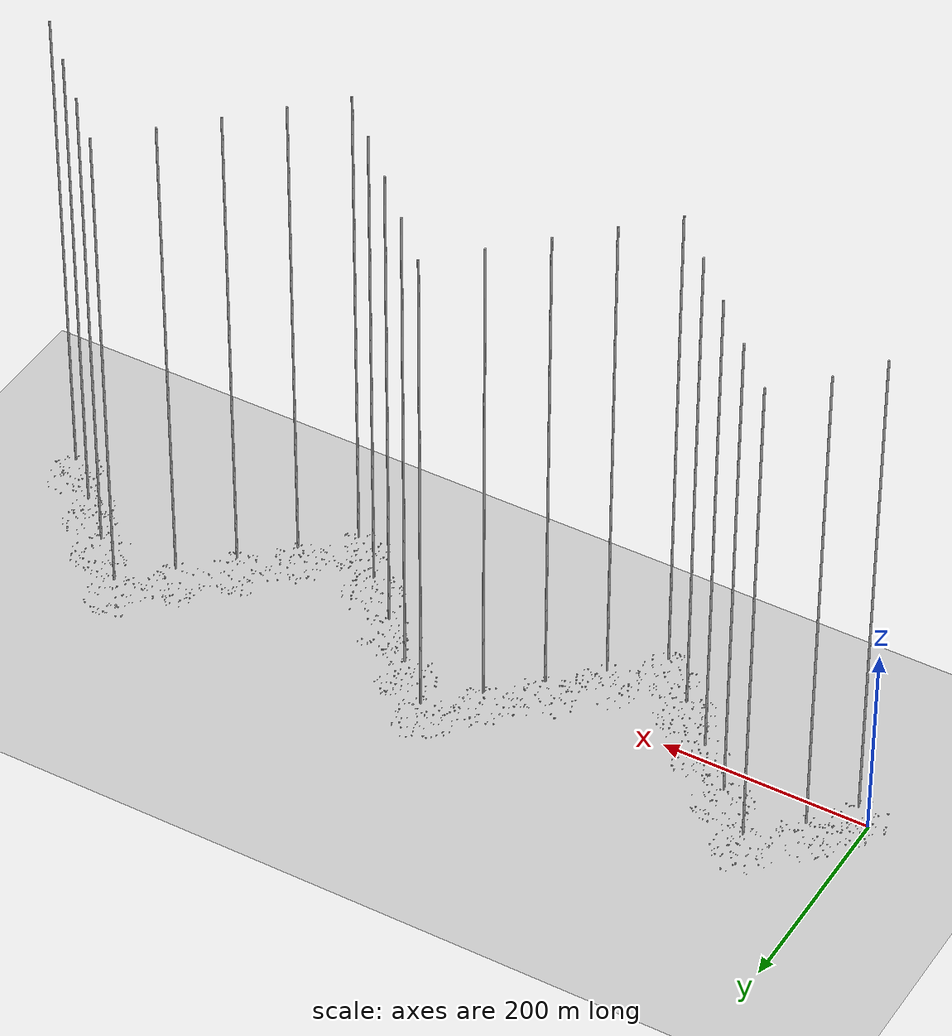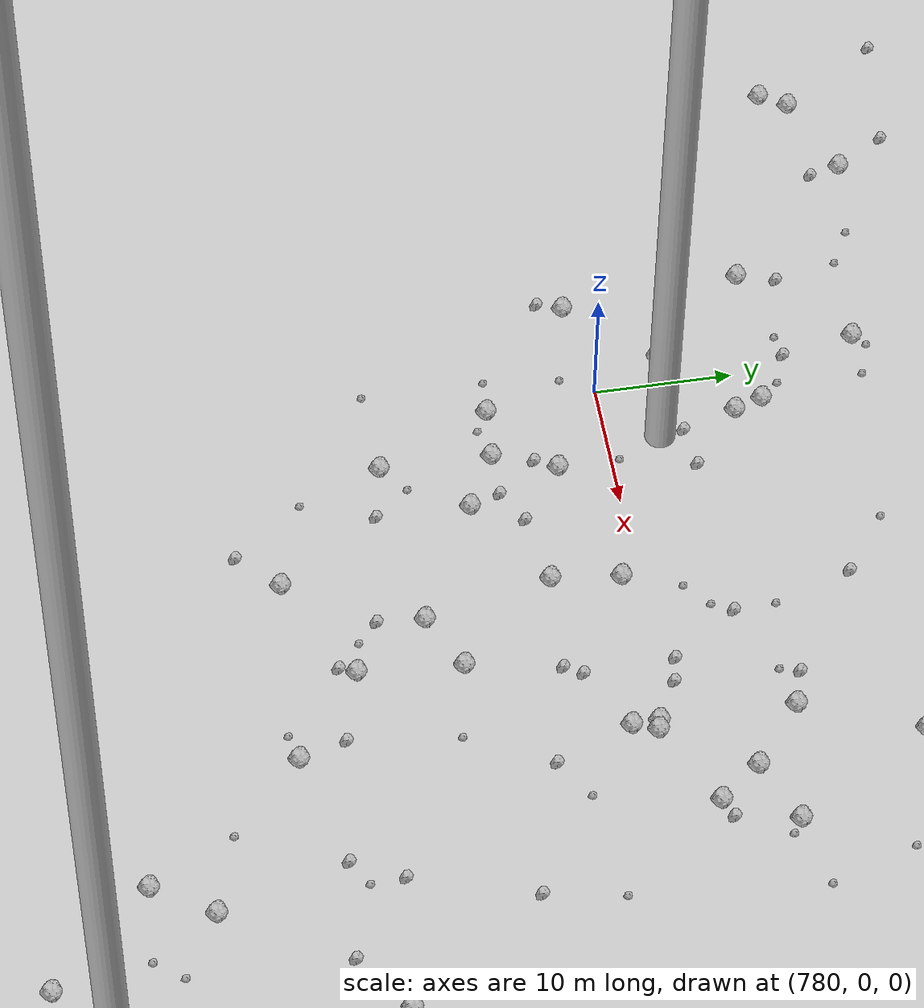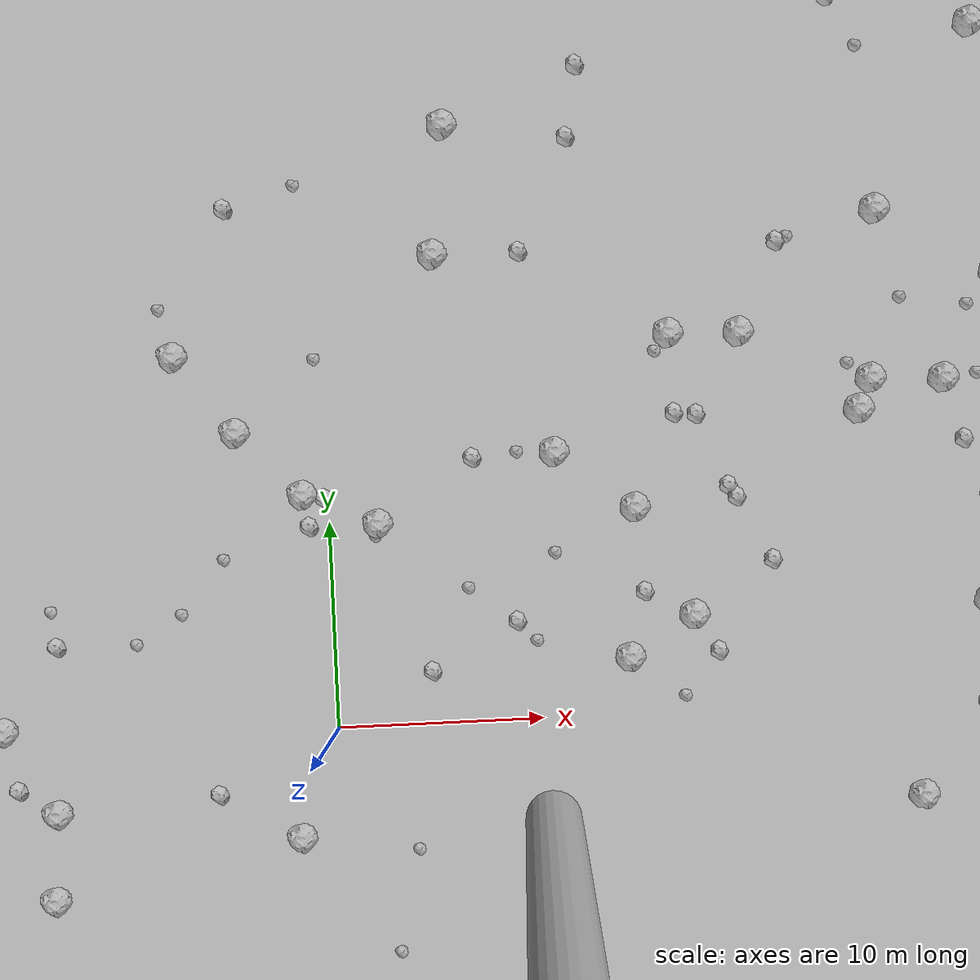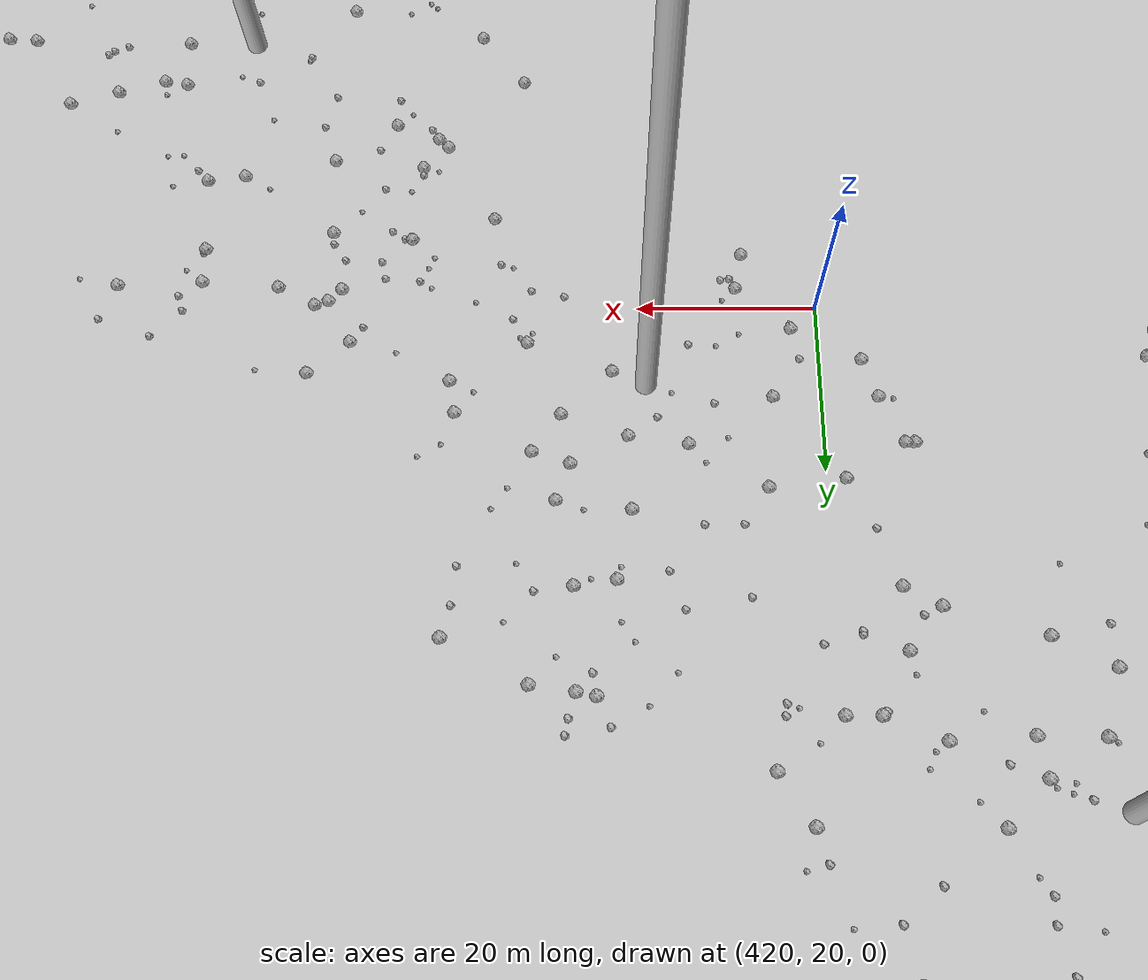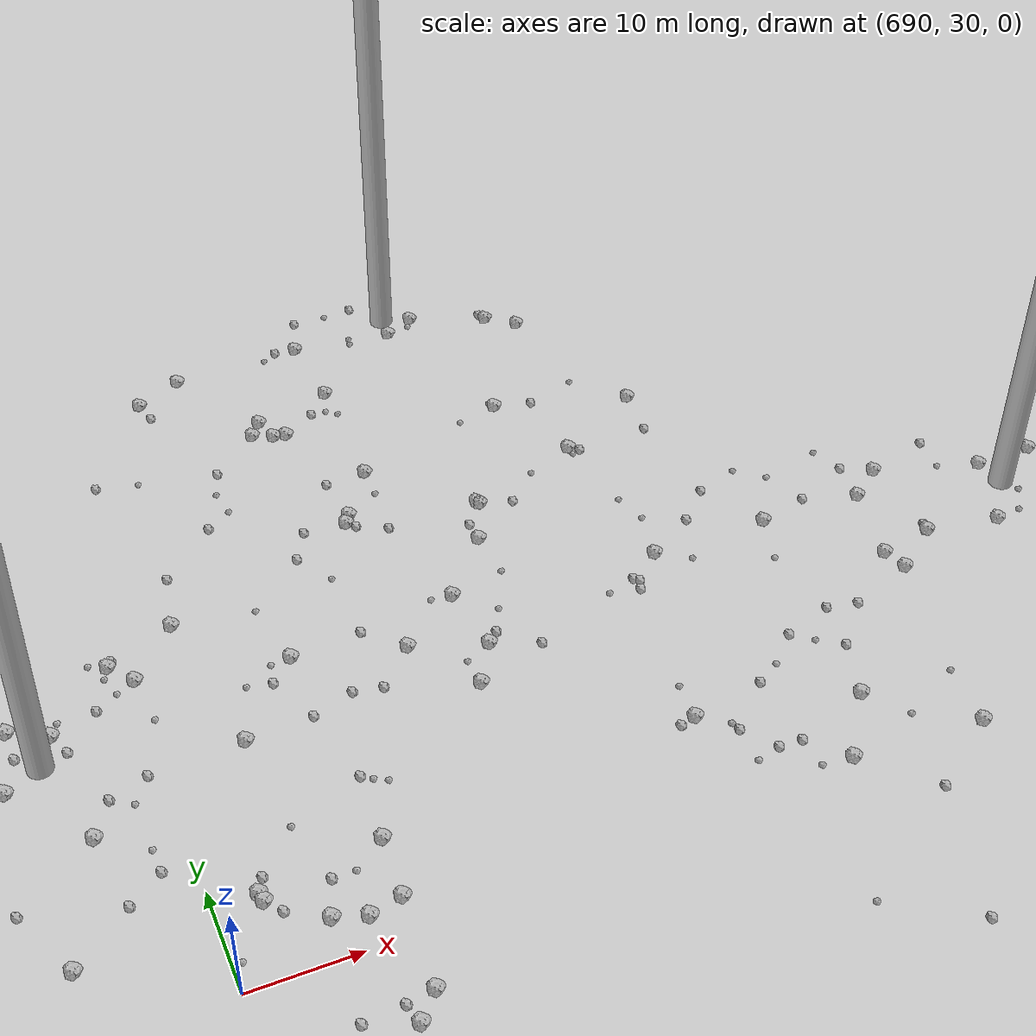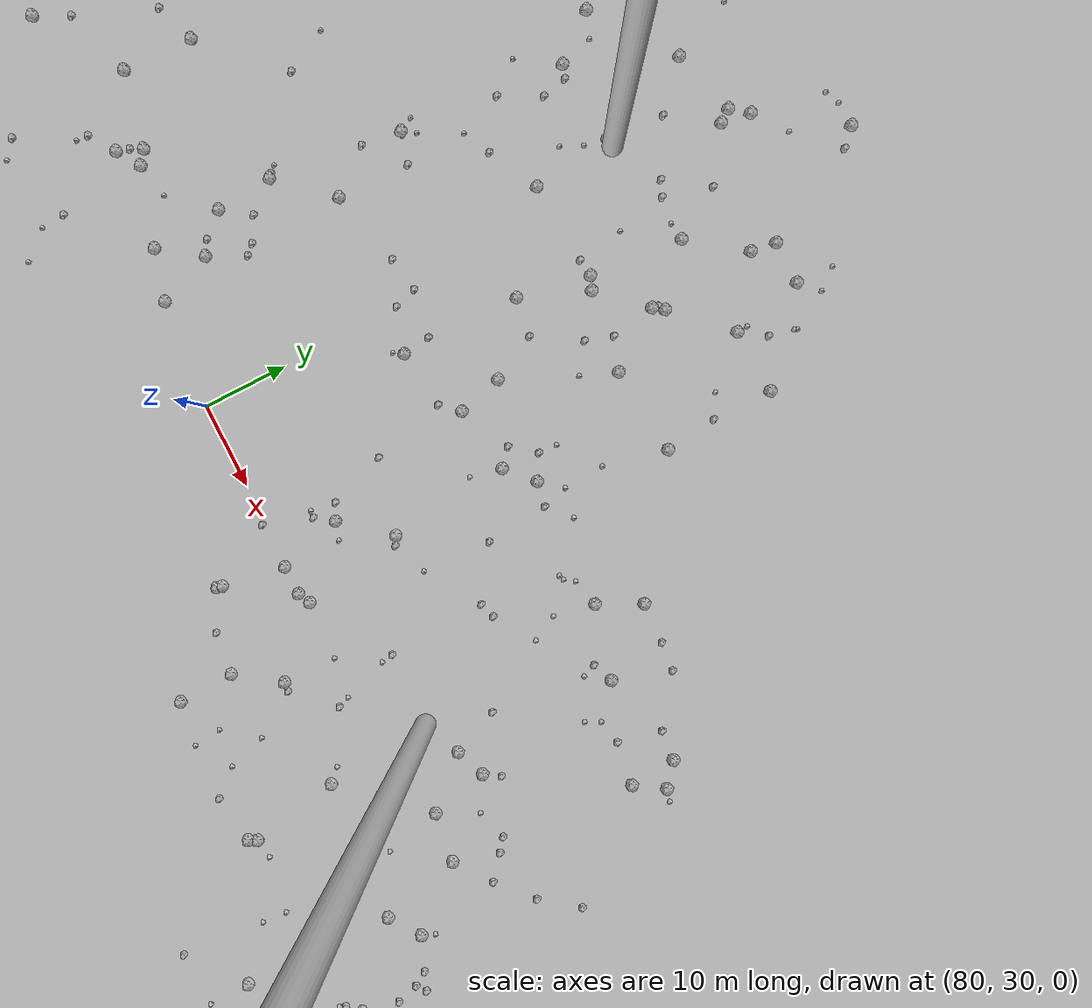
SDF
<sdf version="1.6">
 <world name="default">
  <include><uri>model://custom_ground</uri></include>
  <include><uri>model://sun</uri></include>
  <spherical_coordinates>
   <surface_model>EARTH_WGS84</surface_model>
   <latitude_deg>38.161479</latitude_deg>
   <longitude_deg>-122.454630</longitude_deg>
   <elevation>488.0</elevation>
   <heading_deg>90</heading_deg>
  </spherical_coordinates>
  <model name="rock1_0_0">
   <include><uri>model://rock1</uri><pose>-1.9621739160944358 -5.12846441532416 0.5 0 0 0</pose></include>
  </model>
  <model name="rock1_0_1">
   <include><uri>model://rock1</uri><pose>2.406790936257572 9.860046162250065 0.5 0 0 0</pose></include>
  </model>
  <model name="rock1_0_2">
   <include><uri>model://rock1</uri><pose>29.117398881029132 -15.920238617277402 0.5 0 0 0</pose></include>
  </model>
  <model name="rock1_0_3">
   <include><uri>model://rock1</uri><pose>27.1210325515096 23.92502710337751 0.5 0 0 0</pose></include>
  </model>
  <model name="rock1_0_4">
   <include><uri>model://rock1</uri><pose>-1.1807725033879706 11.415316802916273 0.5 0 0 0</pose></include>
  </model>
  <model name="rock1_0_5">
   <include><uri>model://rock1</uri><pose>5.6541422656964215 22.72937844658599 0.5 0 0 0</pose></include>
  </model>
  <model name="rock1_0_6">
   <include><uri>model://rock1</uri><pose>-7.129282654431819 18.36621314639637 0.5 0 0 0</pose></include>
  </model>
  <model name="rock1_0_7">
   <include><uri>model://rock1</uri><pose>-7.822289211458045 -22.803844123577843 0.5 0 0 0</pose></include>
  </model>
  <model name="rock1_0_8">
   <include><uri>model://rock1</uri><pose>-13.699369211179937 -3.442968281475327 0.5 0 0 0</pose></include>
  </model>
  <model name="rock1_0_9">
   <include><uri>model://rock1</uri><pose>17.50076566148968 4.762381917479679 0.5 0 0 0</pose></include>
  </model>
  <model name="rock1_0_10">
   <include><uri>model://rock1</uri><pose>19.881689935994032 -24.525764848351095 0.5 0 0 0</pose></include>
  </model>
  <model name="rock1_0_11">
   <include><uri>model://rock1</uri><pose>22.339258084341587 -16.962382216102966 0.5 0 0 0</pose></include>
  </model>
  <model name="rock1_0_12">
   <include><uri>model://rock1</uri><pose>28.167162883069274 -4.458024683432285 0.5 0 0 0</pose></include>
  </model>
  <model name="rock1_0_13">
   <include><uri>model://rock1</uri><pose>-4.299061655102454 14.55309751136027 0.5 0 0 0</pose></include>
  </model>
  <model name="rock1_0_14">
   <include><uri>model://rock1</uri><pose>-8.444276054512276 -22.397705040708427 0.5 0 0 0</pose></include>
  </model>
  <model name="rock1_0_15">
   <include><uri>model://rock1</uri><pose>31.808324141640128 4.778917780239915 0.5 0 0 0</pose></include>
  </model>
  <model name="rock1_0_16">
   <include><uri>model://rock1</uri><pose>20.268948090623077 18.303766442358793 0.5 0 0 0</pose></include>
  </model>
  <model name="rock1_0_17">
   <include><uri>model://rock1</uri><pose>-16.165521723558744 0.6434234051497967 0.5 0 0 0</pose></include>
  </model>
  <model name="rock1_0_18">
   <include><uri>model://rock1</uri><pose>16.860362134589003 18.395332644553015 0.5 0 0 0</pose></include>
  </model>
  <model name="rock1_0_19">
   <include><uri>model://rock1</uri><pose>14.869998587635642 10.073966771511913 0.5 0 0 0</pose></include>
  </model>
  <model name="rock1_0_20">
   <include><uri>model://rock1</uri><pose>-1.9917595002998851 -16.122421133589306 0.5 0 0 0</pose></include>
  </model>
  <model name="rock1_0_21">
   <include><uri>model://rock1</uri><pose>11.08652024407452 12.92534547751739 0.5 0 0 0</pose></include>
  </model>
  <model name="rock1_0_22">
   <include><uri>model://rock1</uri><pose>6.41970153672424 28.9687192399237 0.5 0 0 0</pose></include>
  </model>
  <model name="rock1_0_23">
   <include><uri>model://rock1</uri><pose>14.305742643929008 2.84870488110775 0.5 0 0 0</pose></include>
  </model>
  <model name="rock1_0_24">
   <include><uri>model://rock1</uri><pose>-13.977301020355085 -7.623493858549075 0.5 0 0 0</pose></include>
  </model>
  <model name="rock1_0_25">
   <include><uri>model://rock1</uri><pose>9.065879604240546 -15.871713998739542 0.5 0 0 0</pose></include>
  </model>
  <model name="rock1_0_26">
   <include><uri>model://rock1</uri><pose>25.116254775108132 -14.393812115499543 0.5 0 0 0</pose></include>
  </model>
  <model name="rock2_0_0">
   <include><uri>model://rock2</uri><pose>-0.9512676352933802 9.863308822249678 0.3 0 0 0</pose></include>
  </model>
  <model name="rock2_0_1">
   <include><uri>model://rock2</uri><pose>16.97694495906959 14.528927955879773 0.3 0 0 0</pose></include>
  </model>
  <model name="rock2_0_2">
   <include><uri>model://rock2</uri><pose>15.161944271087933 5.953042058184316 0.3 0 0 0</pose></include>
  </model>
  <model name="rock2_0_3">
   <include><uri>model://rock2</uri><pose>18.045062901983826 14.422402434548808 0.3 0 0 0</pose></include>
  </model>
  <model name="rock2_0_4">
   <include><uri>model://rock2</uri><pose>21.443353666416357 7.219147712236932 0.3 0 0 0</pose></include>
  </model>
  <model name="rock2_0_5">
   <include><uri>model://rock2</uri><pose>32.93924433009857 15.708748066307216 0.3 0 0 0</pose></include>
  </model>
  <model name="rock2_0_6">
   <include><uri>model://rock2</uri><pose>33.17824723458303 -1.438376478572664 0.3 0 0 0</pose></include>
  </model>
  <model name="rock2_0_7">
   <include><uri>model://rock2</uri><pose>4.698364935544596 2.583484079485629 0.3 0 0 0</pose></include>
  </model>
  <model name="rock2_0_8">
   <include><uri>model://rock2</uri><pose>31.504699357766206 -0.1574933899729949 0.3 0 0 0</pose></include>
  </model>
  <model name="rock2_0_9">
   <include><uri>model://rock2</uri><pose>-15.63876339692409 -2.2654977034302064 0.3 0 0 0</pose></include>
  </model>
  <model name="rock2_0_10">
   <include><uri>model://rock2</uri><pose>-13.468145874060971 4.6086500631072695 0.3 0 0 0</pose></include>
  </model>
  <model name="rock2_0_11">
   <include><uri>model://rock2</uri><pose>1.253100249813567 -17.817384558164395 0.3 0 0 0</pose></include>
  </model>
  <model name="rock2_0_12">
   <include><uri>model://rock2</uri><pose>-0.1685593569451136 11.206101905887238 0.3 0 0 0</pose></include>
  </model>
  <model name="rock2_0_13">
   <include><uri>model://rock2</uri><pose>23.62815286496864 -16.203150621133094 0.3 0 0 0</pose></include>
  </model>
  <model name="rock2_0_14">
   <include><uri>model://rock2</uri><pose>8.920990005157144 4.820872615915569 0.3 0 0 0</pose></include>
  </model>
  <model name="rock2_0_15">
   <include><uri>model://rock2</uri><pose>12.373455651785306 28.14781990464774 0.3 0 0 0</pose></include>
  </model>
  <model name="rock2_0_16">
   <include><uri>model://rock2</uri><pose>19.82964736904985 10.332701703366887 0.3 0 0 0</pose></include>
  </model>
  <model name="rock2_0_17">
   <include><uri>model://rock2</uri><pose>-5.901046278079189 -2.923629163254514 0.3 0 0 0</pose></include>
  </model>
  <model name="rock2_0_18">
   <include><uri>model://rock2</uri><pose>7.421296729709439 -15.945529432516876 0.3 0 0 0</pose></include>
  </model>
  <model name="rock2_0_19">
   <include><uri>model://rock2</uri><pose>7.094255123744777 12.83139416339413 0.3 0 0 0</pose></include>
  </model>
  <model name="rock2_0_20">
   <include><uri>model://rock2</uri><pose>18.625219728037443 2.9211246467857706 0.3 0 0 0</pose></include>
  </model>
  <model name="rock2_0_21">
   <include><uri>model://rock2</uri><pose>34.973212671422345 -5.091780913009714 0.3 0 0 0</pose></include>
  </model>
  <model name="rock2_0_22">
   <include><uri>model://rock2</uri><pose>19.447480435190386 10.903040420074426 0.3 0 0 0</pose></include>
  </model>
  <model name="rock2_0_23">
   <include><uri>model://rock2</uri><pose>0.7728389834059328 -13.709550411025578 0.3 0 0 0</pose></include>
  </model>
  <model name="rock2_0_24">
   <include><uri>model://rock2</uri><pose>-4.383618546623795 25.43658825124927 0.3 0 0 0</pose></include>
  </model>
  <model name="rock2_0_25">
   <include><uri>model://rock2</uri><pose>9.80431622182811 22.703249083343465 0.3 0 0 0</pose></include>
  </model>
  <model name="rock2_0_26">
   <include><uri>model://rock2</uri><pose>19.72851872025305 -25.310079171841494 0.3 0 0 0</pose></include>
  </model>
  <model name="rock3_0_0">
   <include><uri>model://rock3</uri><pose>6.6018479703172375 6.504288922836999 0.2 0 0 0</pose></include>
  </model>
  <model name="rock3_0_1">
   <include><uri>model://rock3</uri><pose>-7.814374006917459 20.696946496588026 0.2 0 0 0</pose></include>
  </model>
  <model name="rock3_0_2">
   <include><uri>model://rock3</uri><pose>9.238023524337017 12.988465981211988 0.2 0 0 0</pose></include>
  </model>
  <model name="rock3_0_3">
   <include><uri>model://rock3</uri><pose>-7.382391312254477 5.854208655173693 0.2 0 0 0</pose></include>
  </model>
  <model name="rock3_0_4">
   <include><uri>model://rock3</uri><pose>9.028155708889031 -20.94983233982733 0.2 0 0 0</pose></include>
  </model>
  <model name="rock3_0_5">
   <include><uri>model://rock3</uri><pose>2.4919898050098013 -10.989732105225357 0.2 0 0 0</pose></include>
  </model>
  <model name="rock3_0_6">
   <include><uri>model://rock3</uri><pose>-0.3960625220136009 17.939799829223567 0.2 0 0 0</pose></include>
  </model>
  <model name="rock3_0_7">
   <include><uri>model://rock3</uri><pose>16.87905496667043 0.781960978859729 0.2 0 0 0</pose></include>
  </model>
  <model name="rock3_0_8">
   <include><uri>model://rock3</uri><pose>2.2105484365984474 9.221499371410985 0.2 0 0 0</pose></include>
  </model>
  <model name="rock3_0_9">
   <include><uri>model://rock3</uri><pose>-5.217412860190331 8.42233242045701 0.2 0 0 0</pose></include>
  </model>
  <model name="rock3_0_10">
   <include><uri>model://rock3</uri><pose>11.985189333991364 -22.84885577396585 0.2 0 0 0</pose></include>
  </model>
  <model name="rock3_0_11">
   <include><uri>model://rock3</uri><pose>9.097304960307358 -7.8019557729890785 0.2 0 0 0</pose></include>
  </model>
  <model name="rock3_0_12">
   <include><uri>model://rock3</uri><pose>9.810632515594047 3.7969166439816817 0.2 0 0 0</pose></include>
  </model>
  <model name="rock3_0_13">
   <include><uri>model://rock3</uri><pose>10.633696628904566 -29.37181574695389 0.2 0 0 0</pose></include>
  </model>
  <model name="rock3_0_14">
   <include><uri>model://rock3</uri><pose>-9.630750580339956 4.5003065712184025 0.2 0 0 0</pose></include>
  </model>
  <model name="rock3_0_15">
   <include><uri>model://rock3</uri><pose>22.811401296893024 22.805213112714412 0.2 0 0 0</pose></include>
  </model>
  <model name="rock3_0_16">
   <include><uri>model://rock3</uri><pose>-13.724154488136255 6.286421116071587 0.2 0 0 0</pose></include>
  </model>
  <model name="rock3_0_17">
   <include><uri>model://rock3</uri><pose>10.879098123128617 8.01278427451524 0.2 0 0 0</pose></include>
  </model>
  <model name="rock3_0_18">
   <include><uri>model://rock3</uri><pose>3.614705706530735 -6.0506367614252135 0.2 0 0 0</pose></include>
  </model>
  <model name="rock3_0_19">
   <include><uri>model://rock3</uri><pose>25.47863675963997 16.52259698757309 0.2 0 0 0</pose></include>
  </model>
  <model name="rock3_0_20">
   <include><uri>model://rock3</uri><pose>31.930722036046028 9.833426555311732 0.2 0 0 0</pose></include>
  </model>
  <model name="rock3_0_21">
   <include><uri>model://rock3</uri><pose>35.955624733102574 -9.950548807761951 0.2 0 0 0</pose></include>
  </model>
  <model name="rock3_0_22">
   <include><uri>model://rock3</uri><pose>-19.402779208229433 -4.7629209656133185 0.2 0 0 0</pose></include>
  </model>
  <model name="rock3_0_23">
   <include><uri>model://rock3</uri><pose>16.15858934005692 17.54895973956559 0.2 0 0 0</pose></include>
  </model>
  <model name="rock3_0_24">
   <include><uri>model://rock3</uri><pose>-9.610614823358123 -13.075142930374668 0.2 0 0 0</pose></include>
  </model>
  <model name="rock3_0_25">
   <include><uri>model://rock3</uri><pose>-0.9832861695704622 26.419690269958622 0.2 0 0 0</pose></include>
  </model>
  <model name="rock3_0_26">
   <include><uri>model://rock3</uri><pose>19.505267708508818 -21.170894273553643 0.2 0 0 0</pose></include>
  </model>
  <model name="rock1_1_0">
   <include><uri>model://rock1</uri><pose>42.53762991255247 47.42873432591494 0.5 0 0 0</pose></include>
  </model>
  <model name="rock1_1_1">
   <include><uri>model://rock1</uri><pose>35.655951860612724 21.182959087283646 0.5 0 0 0</pose></include>
  </model>
  <model name="rock1_1_2">
   <include><uri>model://rock1</uri><pose>24.39670765762793 37.53455317833159 0.5 0 0 0</pose></include>
  </model>
  <model name="rock1_1_3">
   <include><uri>model://rock1</uri><pose>39.72641345443459 22.966158194020892 0.5 0 0 0</pose></include>
  </model>
  <model name="rock1_1_4">
   <include><uri>model://rock1</uri><pose>61.644430411162205 33.07836855025314 0.5 0 0 0</pose></include>
  </model>
  <model name="rock1_1_5">
   <include><uri>model://rock1</uri><pose>61.03867852898104 41.45976041111099 0.5 0 0 0</pose></include>
  </model>
  <model name="rock1_1_6">
   <include><uri>model://rock1</uri><pose>49.97331346327645 34.19038772411966 0.5 0 0 0</pose></include>
  </model>
  <model name="rock1_1_7">
   <include><uri>model://rock1</uri><pose>37.09109587138037 18.51986946970592 0.5 0 0 0</pose></include>
  </model>
  <model name="rock1_1_8">
   <include><uri>model://rock1</uri><pose>32.515531989520156 47.73233659452934 0.5 0 0 0</pose></include>
  </model>
  <model name="rock1_1_9">
   <include><uri>model://rock1</uri><pose>44.608446139561586 20.45392874329946 0.5 0 0 0</pose></include>
  </model>
  <model name="rock1_1_10">
   <include><uri>model://rock1</uri><pose>30.067189222065924 15.611446004069505 0.5 0 0 0</pose></include>
  </model>
  <model name="rock1_1_11">
   <include><uri>model://rock1</uri><pose>45.05858386878569 13.82270739860122 0.5 0 0 0</pose></include>
  </model>
  <model name="rock1_1_12">
   <include><uri>model://rock1</uri><pose>51.134353940059995 37.08154793409953 0.5 0 0 0</pose></include>
  </model>
  <model name="rock1_1_13">
   <include><uri>model://rock1</uri><pose>20.32793046550221 36.74834208945198 0.5 0 0 0</pose></include>
  </model>
  <model name="rock1_1_14">
   <include><uri>model://rock1</uri><pose>21.130521453761478 56.717454466756585 0.5 0 0 0</pose></include>
  </model>
  <model name="rock1_1_15">
   <include><uri>model://rock1</uri><pose>26.556353352656043 15.766011489981198 0.5 0 0 0</pose></include>
  </model>
  <model name="rock1_1_16">
   <include><uri>model://rock1</uri><pose>20.340113401442583 54.208968227763705 0.5 0 0 0</pose></include>
  </model>
  <model name="rock1_1_17">
   <include><uri>model://rock1</uri><pose>24.76480189916939 40.71962135292384 0.5 0 0 0</pose></include>
  </model>
  <model name="rock1_1_18">
   <include><uri>model://rock1</uri><pose>13.775534063128944 49.43449226175085 0.5 0 0 0</pose></include>
  </model>
  <model name="rock1_1_19">
   <include><uri>model://rock1</uri><pose>60.4965334017229 48.153820706948366 0.5 0 0 0</pose></include>
  </model>
  <model name="rock1_1_20">
   <include><uri>model://rock1</uri><pose>32.110054276141796 32.73097002620036 0.5 0 0 0</pose></include>
  </model>
  <model name="rock1_1_21">
   <include><uri>model://rock1</uri><pose>65.02631653259408 37.7789500675937 0.5 0 0 0</pose></include>
  </model>
  <model name="rock1_1_22">
   <include><uri>model://rock1</uri><pose>42.2442385426582 39.146819171637276 0.5 0 0 0</pose></include>
  </model>
  <model name="rock1_1_23">
   <include><uri>model://rock1</uri><pose>52.659879264336546 35.92902655437385 0.5 0 0 0</pose></include>
  </model>
  <model name="rock1_1_24">
   <include><uri>model://rock1</uri><pose>32.77513921717497 20.66265561933859 0.5 0 0 0</pose></include>
  </model>
  <model name="rock1_1_25">
   <include><uri>model://rock1</uri><pose>25.919574669999278 14.309444681688877 0.5 0 0 0</pose></include>
  </model>
  <model name="rock1_1_26">
   <include><uri>model://rock1</uri><pose>67.50087504725084 31.412818472511052 0.5 0 0 0</pose></include>
  </model>
  <model name="rock2_1_0">
   <include><uri>model://rock2</uri><pose>12.994108316895403 31.615683607705474 0.3 0 0 0</pose></include>
  </model>
  <model name="rock2_1_1">
   <include><uri>model://rock2</uri><pose>63.243504491318085 44.67840274993337 0.3 0 0 0</pose></include>
  </model>
  <model name="rock2_1_2">
   <include><uri>model://rock2</uri><pose>32.197551348733796 44.47441038366719 0.3 0 0 0</pose></include>
  </model>
  <model name="rock2_1_3">
   <include><uri>model://rock2</uri><pose>63.288720882074465 38.76110895893238 0.3 0 0 0</pose></include>
  </model>
  <model name="rock2_1_4">
   <include><uri>model://rock2</uri><pose>11.643162845477681 41.97334162384428 0.3 0 0 0</pose></include>
  </model>
  <model name="rock2_1_5">
   <include><uri>model://rock2</uri><pose>59.974456965195884 48.551255641063044 0.3 0 0 0</pose></include>
  </model>
  <model name="rock2_1_6">
   <include><uri>model://rock2</uri><pose>50.8215321747554 55.8009487183162 0.3 0 0 0</pose></include>
  </model>
  <model name="rock2_1_7">
   <include><uri>model://rock2</uri><pose>31.652803292341233 43.6081277686249 0.3 0 0 0</pose></include>
  </model>
  <model name="rock2_1_8">
   <include><uri>model://rock2</uri><pose>37.66629287101196 45.8131958981131 0.3 0 0 0</pose></include>
  </model>
  <model name="rock2_1_9">
   <include><uri>model://rock2</uri><pose>22.286514309885504 22.610154403365918 0.3 0 0 0</pose></include>
  </model>
  <model name="rock2_1_10">
   <include><uri>model://rock2</uri><pose>67.03203675798704 42.02242788220864 0.3 0 0 0</pose></include>
  </model>
  <model name="rock2_1_11">
   <include><uri>model://rock2</uri><pose>33.95469068374337 36.63592883509912 0.3 0 0 0</pose></include>
  </model>
  <model name="rock2_1_12">
   <include><uri>model://rock2</uri><pose>66.02987252547126 43.077931596864275 0.3 0 0 0</pose></include>
  </model>
  <model name="rock2_1_13">
   <include><uri>model://rock2</uri><pose>19.971182245050514 44.20948660839784 0.3 0 0 0</pose></include>
  </model>
  <model name="rock2_1_14">
   <include><uri>model://rock2</uri><pose>43.16004017257663 24.413082657649156 0.3 0 0 0</pose></include>
  </model>
  <model name="rock2_1_15">
   <include><uri>model://rock2</uri><pose>46.810024016378755 32.15070565955465 0.3 0 0 0</pose></include>
  </model>
  <model name="rock2_1_16">
   <include><uri>model://rock2</uri><pose>33.15847541021742 44.424462786963595 0.3 0 0 0</pose></include>
  </model>
  <model name="rock2_1_17">
   <include><uri>model://rock2</uri><pose>31.880705290282425 37.612713451608116 0.3 0 0 0</pose></include>
  </model>
  <model name="rock2_1_18">
   <include><uri>model://rock2</uri><pose>16.3459649004445 48.72695237033931 0.3 0 0 0</pose></include>
  </model>
  <model name="rock2_1_19">
   <include><uri>model://rock2</uri><pose>35.58830729706766 62.665696668700576 0.3 0 0 0</pose></include>
  </model>
  <model name="rock2_1_20">
   <include><uri>model://rock2</uri><pose>30.975537485255906 12.611322270495823 0.3 0 0 0</pose></include>
  </model>
  <model name="rock2_1_21">
   <include><uri>model://rock2</uri><pose>20.445601665340785 44.61231775142989 0.3 0 0 0</pose></include>
  </model>
  <model name="rock2_1_22">
   <include><uri>model://rock2</uri><pose>16.287777855708526 48.11798932924518 0.3 0 0 0</pose></include>
  </model>
  <model name="rock2_1_23">
   <include><uri>model://rock2</uri><pose>21.453918234622904 57.80189455081946 0.3 0 0 0</pose></include>
  </model>
  <model name="rock2_1_24">
   <include><uri>model://rock2</uri><pose>25.281148394348293 34.373265474351015 0.3 0 0 0</pose></include>
  </model>
  <model name="rock2_1_25">
   <include><uri>model://rock2</uri><pose>53.505133267550335 25.649411309451274 0.3 0 0 0</pose></include>
  </model>
  <model name="rock2_1_26">
   <include><uri>model://rock2</uri><pose>50.291003582080705 35.65921726524026 0.3 0 0 0</pose></include>
  </model>
  <model name="rock3_1_0">
   <include><uri>model://rock3</uri><pose>13.304737766048989 45.78884995439628 0.2 0 0 0</pose></include>
  </model>
  <model name="rock3_1_1">
   <include><uri>model://rock3</uri><pose>35.91454491139297 21.495475821090587 0.2 0 0 0</pose></include>
  </model>
  <model name="rock3_1_2">
   <include><uri>model://rock3</uri><pose>28.161858079257126 19.598620299249255 0.2 0 0 0</pose></include>
  </model>
  <model name="rock3_1_3">
   <include><uri>model://rock3</uri><pose>20.45872319965598 59.13225235083164 0.2 0 0 0</pose></include>
  </model>
  <model name="rock3_1_4">
   <include><uri>model://rock3</uri><pose>31.40061384605596 19.117912418170604 0.2 0 0 0</pose></include>
  </model>
  <model name="rock3_1_5">
   <include><uri>model://rock3</uri><pose>45.09551884961537 22.657661582696242 0.2 0 0 0</pose></include>
  </model>
  <model name="rock3_1_6">
   <include><uri>model://rock3</uri><pose>28.962151874439336 40.8911695232208 0.2 0 0 0</pose></include>
  </model>
  <model name="rock3_1_7">
   <include><uri>model://rock3</uri><pose>35.2400402439826 54.16933593735327 0.2 0 0 0</pose></include>
  </model>
  <model name="rock3_1_8">
   <include><uri>model://rock3</uri><pose>54.544889647738245 15.317717445705693 0.2 0 0 0</pose></include>
  </model>
  <model name="rock3_1_9">
   <include><uri>model://rock3</uri><pose>29.036945256849297 44.41783672278261 0.2 0 0 0</pose></include>
  </model>
  <model name="rock3_1_10">
   <include><uri>model://rock3</uri><pose>31.733078515374388 15.758581995300418 0.2 0 0 0</pose></include>
  </model>
  <model name="rock3_1_11">
   <include><uri>model://rock3</uri><pose>48.167286474877265 60.82533333317016 0.2 0 0 0</pose></include>
  </model>
  <model name="rock3_1_12">
   <include><uri>model://rock3</uri><pose>46.697558146697304 30.68790530847678 0.2 0 0 0</pose></include>
  </model>
  <model name="rock3_1_13">
   <include><uri>model://rock3</uri><pose>42.06319131090213 64.14167093440122 0.2 0 0 0</pose></include>
  </model>
  <model name="rock3_1_14">
   <include><uri>model://rock3</uri><pose>28.358842696547647 47.657261192954785 0.2 0 0 0</pose></include>
  </model>
  <model name="rock3_1_15">
   <include><uri>model://rock3</uri><pose>16.971633001974876 37.922167061130345 0.2 0 0 0</pose></include>
  </model>
  <model name="rock3_1_16">
   <include><uri>model://rock3</uri><pose>26.76000683361837 52.9382797253266 0.2 0 0 0</pose></include>
  </model>
  <model name="rock3_1_17">
   <include><uri>model://rock3</uri><pose>26.591393297040412 31.90423361956067 0.2 0 0 0</pose></include>
  </model>
  <model name="rock3_1_18">
   <include><uri>model://rock3</uri><pose>56.68661577801623 36.63603241173297 0.2 0 0 0</pose></include>
  </model>
  <model name="rock3_1_19">
   <include><uri>model://rock3</uri><pose>59.29060481266969 49.2177524139976 0.2 0 0 0</pose></include>
  </model>
  <model name="rock3_1_20">
   <include><uri>model://rock3</uri><pose>41.737971846012094 10.686048545686642 0.2 0 0 0</pose></include>
  </model>
  <model name="rock3_1_21">
   <include><uri>model://rock3</uri><pose>49.76004771911721 17.369813906106327 0.2 0 0 0</pose></include>
  </model>
  <model name="rock3_1_22">
   <include><uri>model://rock3</uri><pose>31.329423274694324 66.94689102519999 0.2 0 0 0</pose></include>
  </model>
  <model name="rock3_1_23">
   <include><uri>model://rock3</uri><pose>53.69555062391866 22.769772754907784 0.2 0 0 0</pose></include>
  </model>
  <model name="rock3_1_24">
   <include><uri>model://rock3</uri><pose>27.364623153042427 41.28301282477496 0.2 0 0 0</pose></include>
  </model>
  <model name="rock3_1_25">
   <include><uri>model://rock3</uri><pose>26.281579705563104 39.111125850117546 0.2 0 0 0</pose></include>
  </model>
  <model name="rock3_1_26">
   <include><uri>model://rock3</uri><pose>56.41398404701496 19.62390202799135 0.2 0 0 0</pose></include>
  </model>
  <model name="rock1_2_0">
   <include><uri>model://rock1</uri><pose>78.61651477992164 99.64296776349016 0.5 0 0 0</pose></include>
  </model>
  <model name="rock1_2_1">
   <include><uri>model://rock1</uri><pose>85.10422111061239 66.75817905754532 0.5 0 0 0</pose></include>
  </model>
  <model name="rock1_2_2">
   <include><uri>model://rock1</uri><pose>92.3289898441849 60.72356560140365 0.5 0 0 0</pose></include>
  </model>
  <model name="rock1_2_3">
   <include><uri>model://rock1</uri><pose>86.6679916886981 75.29994028979377 0.5 0 0 0</pose></include>
  </model>
  <model name="rock1_2_4">
   <include><uri>model://rock1</uri><pose>93.90391825522991 81.02371434432317 0.5 0 0 0</pose></include>
  </model>
  <model name="rock1_2_5">
   <include><uri>model://rock1</uri><pose>65.97701583001663 54.13113645452362 0.5 0 0 0</pose></include>
  </model>
  <model name="rock1_2_6">
   <include><uri>model://rock1</uri><pose>107.43784704298992 87.41441055696431 0.5 0 0 0</pose></include>
  </model>
  <model name="rock1_2_7">
   <include><uri>model://rock1</uri><pose>78.08826268351815 96.19058078206933 0.5 0 0 0</pose></include>
  </model>
  <model name="rock1_2_8">
   <include><uri>model://rock1</uri><pose>59.87840138785926 88.45521140724057 0.5 0 0 0</pose></include>
  </model>
  <model name="rock1_2_9">
   <include><uri>model://rock1</uri><pose>92.8950979132932 95.56797075715717 0.5 0 0 0</pose></include>
  </model>
  <model name="rock1_2_10">
   <include><uri>model://rock1</uri><pose>75.04606480704032 74.47924780985235 0.5 0 0 0</pose></include>
  </model>
  <model name="rock1_2_11">
   <include><uri>model://rock1</uri><pose>93.67405024626086 55.48902399953329 0.5 0 0 0</pose></include>
  </model>
  <model name="rock1_2_12">
   <include><uri>model://rock1</uri><pose>62.53334038543663 63.725644754753944 0.5 0 0 0</pose></include>
  </model>
  <model name="rock1_2_13">
   <include><uri>model://rock1</uri><pose>97.78187920189909 73.20326336281136 0.5 0 0 0</pose></include>
  </model>
  <model name="rock1_2_14">
   <include><uri>model://rock1</uri><pose>108.06850154110404 74.17694843281157 0.5 0 0 0</pose></include>
  </model>
  <model name="rock1_2_15">
   <include><uri>model://rock1</uri><pose>87.6992681312303 86.28100649924747 0.5 0 0 0</pose></include>
  </model>
  <model name="rock1_2_16">
   <include><uri>model://rock1</uri><pose>97.94331919960251 95.6102683680004 0.5 0 0 0</pose></include>
  </model>
  <model name="rock1_2_17">
   <include><uri>model://rock1</uri><pose>85.00264552656823 109.08816092442363 0.5 0 0 0</pose></include>
  </model>
  <model name="rock1_2_18">
   <include><uri>model://rock1</uri><pose>88.24113590546743 74.66738933892225 0.5 0 0 0</pose></include>
  </model>
  <model name="rock1_2_19">
   <include><uri>model://rock1</uri><pose>99.84275024615746 87.12001304266491 0.5 0 0 0</pose></include>
  </model>
  <model name="rock1_2_20">
   <include><uri>model://rock1</uri><pose>77.0227984414264 97.61471236217088 0.5 0 0 0</pose></include>
  </model>
  <model name="rock1_2_21">
   <include><uri>model://rock1</uri><pose>64.10242337502709 83.31426662100695 0.5 0 0 0</pose></include>
  </model>
  <model name="rock1_2_22">
   <include><uri>model://rock1</uri><pose>69.2834086425961 95.39567258933386 0.5 0 0 0</pose></include>
  </model>
  <model name="rock1_2_23">
   <include><uri>model://rock1</uri><pose>73.81356706441551 84.01015907545154 0.5 0 0 0</pose></include>
  </model>
  <model name="rock1_2_24">
   <include><uri>model://rock1</uri><pose>84.96527640374111 52.650142744924025 0.5 0 0 0</pose></include>
  </model>
  <model name="rock1_2_25">
   <include><uri>model://rock1</uri><pose>93.04643651306895 79.79841468812087 0.5 0 0 0</pose></include>
  </model>
  <model name="rock1_2_26">
   <include><uri>model://rock1</uri><pose>92.44728012766316 92.57571264639566 0.5 0 0 0</pose></include>
  </model>
  <model name="rock2_2_0">
   <include><uri>model://rock2</uri><pose>92.85620191731456 71.4192692205041 0.3 0 0 0</pose></include>
  </model>
  <model name="rock2_2_1">
   <include><uri>model://rock2</uri><pose>63.07948042739387 103.16905706994415 0.3 0 0 0</pose></include>
  </model>
  <model name="rock2_2_2">
   <include><uri>model://rock2</uri><pose>51.316507085236125 80.60129580015013 0.3 0 0 0</pose></include>
  </model>
  <model name="rock2_2_3">
   <include><uri>model://rock2</uri><pose>61.81382709466231 59.083249875137284 0.3 0 0 0</pose></include>
  </model>
  <model name="rock2_2_4">
   <include><uri>model://rock2</uri><pose>93.88929211182086 74.61397857843258 0.3 0 0 0</pose></include>
  </model>
  <model name="rock2_2_5">
   <include><uri>model://rock2</uri><pose>89.56281526387053 66.1023132537299 0.3 0 0 0</pose></include>
  </model>
  <model name="rock2_2_6">
   <include><uri>model://rock2</uri><pose>74.82161957848419 56.302535595504196 0.3 0 0 0</pose></include>
  </model>
  <model name="rock2_2_7">
   <include><uri>model://rock2</uri><pose>86.8983848627604 107.35831265313095 0.3 0 0 0</pose></include>
  </model>
  <model name="rock2_2_8">
   <include><uri>model://rock2</uri><pose>84.00876920104403 92.20354890827359 0.3 0 0 0</pose></include>
  </model>
  <model name="rock2_2_9">
   <include><uri>model://rock2</uri><pose>84.53816021111962 75.10264565368685 0.3 0 0 0</pose></include>
  </model>
  <model name="rock2_2_10">
   <include><uri>model://rock2</uri><pose>93.09436420681615 80.54128750478768 0.3 0 0 0</pose></include>
  </model>
  <model name="rock2_2_11">
   <include><uri>model://rock2</uri><pose>74.27137800056303 90.85349343984518 0.3 0 0 0</pose></include>
  </model>
  <model name="rock2_2_12">
   <include><uri>model://rock2</uri><pose>75.10502942900101 74.67157759739615 0.3 0 0 0</pose></include>
  </model>
  <model name="rock2_2_13">
   <include><uri>model://rock2</uri><pose>78.96005891387432 56.95045374673664 0.3 0 0 0</pose></include>
  </model>
  <model name="rock2_2_14">
   <include><uri>model://rock2</uri><pose>65.56464763046768 82.85141862706757 0.3 0 0 0</pose></include>
  </model>
  <model name="rock2_2_15">
   <include><uri>model://rock2</uri><pose>99.52388097109946 58.30752673397689 0.3 0 0 0</pose></include>
  </model>
  <model name="rock2_2_16">
   <include><uri>model://rock2</uri><pose>79.79617046334428 54.30234818205612 0.3 0 0 0</pose></include>
  </model>
  <model name="rock2_2_17">
   <include><uri>model://rock2</uri><pose>69.07140649181036 71.51554912457019 0.3 0 0 0</pose></include>
  </model>
  <model name="rock2_2_18">
   <include><uri>model://rock2</uri><pose>66.11339607250008 62.704829125956024 0.3 0 0 0</pose></include>
  </model>
  <model name="rock2_2_19">
   <include><uri>model://rock2</uri><pose>66.22638381504048 79.87057496160423 0.3 0 0 0</pose></include>
  </model>
  <model name="rock2_2_20">
   <include><uri>model://rock2</uri><pose>101.80150332873029 90.12730411242674 0.3 0 0 0</pose></include>
  </model>
  <model name="rock2_2_21">
   <include><uri>model://rock2</uri><pose>63.80796481112908 75.14708681362524 0.3 0 0 0</pose></include>
  </model>
  <model name="rock2_2_22">
   <include><uri>model://rock2</uri><pose>91.74847764736006 53.443090259526244 0.3 0 0 0</pose></include>
  </model>
  <model name="rock2_2_23">
   <include><uri>model://rock2</uri><pose>84.50397856088696 55.91439251546062 0.3 0 0 0</pose></include>
  </model>
  <model name="rock2_2_24">
   <include><uri>model://rock2</uri><pose>82.41586335309745 86.56643893424112 0.3 0 0 0</pose></include>
  </model>
  <model name="rock2_2_25">
   <include><uri>model://rock2</uri><pose>107.35469446512934 80.35884179501679 0.3 0 0 0</pose></include>
  </model>
  <model name="rock2_2_26">
   <include><uri>model://rock2</uri><pose>80.61622023828274 87.31951936138586 0.3 0 0 0</pose></include>
  </model>
  <model name="rock3_2_0">
   <include><uri>model://rock3</uri><pose>72.05575965185348 78.81828466441013 0.2 0 0 0</pose></include>
  </model>
  <model name="rock3_2_1">
   <include><uri>model://rock3</uri><pose>65.85069286197809 69.91399235618657 0.2 0 0 0</pose></include>
  </model>
  <model name="rock3_2_2">
   <include><uri>model://rock3</uri><pose>83.65450800662222 80.59192271698248 0.2 0 0 0</pose></include>
  </model>
  <model name="rock3_2_3">
   <include><uri>model://rock3</uri><pose>73.19925629404094 81.34277102626737 0.2 0 0 0</pose></include>
  </model>
  <model name="rock3_2_4">
   <include><uri>model://rock3</uri><pose>63.376816259299424 65.19997736621099 0.2 0 0 0</pose></include>
  </model>
  <model name="rock3_2_5">
   <include><uri>model://rock3</uri><pose>61.55053532355325 65.33159649107526 0.2 0 0 0</pose></include>
  </model>
  <model name="rock3_2_6">
   <include><uri>model://rock3</uri><pose>104.72957773483469 81.88455270309008 0.2 0 0 0</pose></include>
  </model>
  <model name="rock3_2_7">
   <include><uri>model://rock3</uri><pose>102.57296145651704 93.3226831122069 0.2 0 0 0</pose></include>
  </model>
  <model name="rock3_2_8">
   <include><uri>model://rock3</uri><pose>82.3369774567891 102.6425393364714 0.2 0 0 0</pose></include>
  </model>
  <model name="rock3_2_9">
   <include><uri>model://rock3</uri><pose>102.47335639744539 93.01327618754954 0.2 0 0 0</pose></include>
  </model>
  <model name="rock3_2_10">
   <include><uri>model://rock3</uri><pose>62.79998037859919 87.3514456861527 0.2 0 0 0</pose></include>
  </model>
  <model name="rock3_2_11">
   <include><uri>model://rock3</uri><pose>99.72841884072275 88.4320203362434 0.2 0 0 0</pose></include>
  </model>
  <model name="rock3_2_12">
   <include><uri>model://rock3</uri><pose>106.33477191419149 66.72594169741583 0.2 0 0 0</pose></include>
  </model>
  <model name="rock3_2_13">
   <include><uri>model://rock3</uri><pose>99.99463575088272 97.73113017512253 0.2 0 0 0</pose></include>
  </model>
  <model name="rock3_2_14">
   <include><uri>model://rock3</uri><pose>60.86298201183352 78.64158530938269 0.2 0 0 0</pose></include>
  </model>
  <model name="rock3_2_15">
   <include><uri>model://rock3</uri><pose>65.96281129789412 102.79861280319432 0.2 0 0 0</pose></include>
  </model>
  <model name="rock3_2_16">
   <include><uri>model://rock3</uri><pose>82.01148979614699 109.10569162355779 0.2 0 0 0</pose></include>
  </model>
  <model name="rock3_2_17">
   <include><uri>model://rock3</uri><pose>62.91357165690698 63.6237730823886 0.2 0 0 0</pose></include>
  </model>
  <model name="rock3_2_18">
   <include><uri>model://rock3</uri><pose>96.07601378344856 69.03864269108985 0.2 0 0 0</pose></include>
  </model>
  <model name="rock3_2_19">
   <include><uri>model://rock3</uri><pose>53.79215480204287 84.36264779501488 0.2 0 0 0</pose></include>
  </model>
  <model name="rock3_2_20">
   <include><uri>model://rock3</uri><pose>80.2445347921566 108.35975262095877 0.2 0 0 0</pose></include>
  </model>
  <model name="rock3_2_21">
   <include><uri>model://rock3</uri><pose>85.53496283020543 86.0690723498261 0.2 0 0 0</pose></include>
  </model>
  <model name="rock3_2_22">
   <include><uri>model://rock3</uri><pose>101.84549813941764 63.219953751086315 0.2 0 0 0</pose></include>
  </model>
  <model name="rock3_2_23">
   <include><uri>model://rock3</uri><pose>84.19597377919062 51.51506928809665 0.2 0 0 0</pose></include>
  </model>
  <model name="rock3_2_24">
   <include><uri>model://rock3</uri><pose>61.792863495870975 100.79559864693775 0.2 0 0 0</pose></include>
  </model>
  <model name="rock3_2_25">
   <include><uri>model://rock3</uri><pose>54.347238864893825 88.43218322514826 0.2 0 0 0</pose></include>
  </model>
  <model name="rock3_2_26">
   <include><uri>model://rock3</uri><pose>98.11106647964488 100.06807317838312 0.2 0 0 0</pose></include>
  </model>
  <model name="rock1_3_0">
   <include><uri>model://rock1</uri><pose>98.7437083628516 21.96856352308529 0.5 0 0 0</pose></include>
  </model>
  <model name="rock1_3_1">
   <include><uri>model://rock1</uri><pose>98.89426143539545 22.58849475912678 0.5 0 0 0</pose></include>
  </model>
  <model name="rock1_3_2">
   <include><uri>model://rock1</uri><pose>139.80419125219302 53.40150844753833 0.5 0 0 0</pose></include>
  </model>
  <model name="rock1_3_3">
   <include><uri>model://rock1</uri><pose>144.03062832155555 24.67686778899403 0.5 0 0 0</pose></include>
  </model>
  <model name="rock1_3_4">
   <include><uri>model://rock1</uri><pose>103.53718138128548 29.829146970224578 0.5 0 0 0</pose></include>
  </model>
  <model name="rock1_3_5">
   <include><uri>model://rock1</uri><pose>108.15449369219824 18.98025724663217 0.5 0 0 0</pose></include>
  </model>
  <model name="rock1_3_6">
   <include><uri>model://rock1</uri><pose>111.70684565526155 23.89850754718541 0.5 0 0 0</pose></include>
  </model>
  <model name="rock1_3_7">
   <include><uri>model://rock1</uri><pose>122.27191451511484 63.911134333079424 0.5 0 0 0</pose></include>
  </model>
  <model name="rock1_3_8">
   <include><uri>model://rock1</uri><pose>132.5625045569068 32.318720088967574 0.5 0 0 0</pose></include>
  </model>
  <model name="rock1_3_9">
   <include><uri>model://rock1</uri><pose>108.33677076077893 12.533743718265008 0.5 0 0 0</pose></include>
  </model>
  <model name="rock1_3_10">
   <include><uri>model://rock1</uri><pose>139.3944158732004 58.83428221106295 0.5 0 0 0</pose></include>
  </model>
  <model name="rock1_3_11">
   <include><uri>model://rock1</uri><pose>100.16516023120856 29.81235640705484 0.5 0 0 0</pose></include>
  </model>
  <model name="rock1_3_12">
   <include><uri>model://rock1</uri><pose>124.28009727087607 23.368162626466997 0.5 0 0 0</pose></include>
  </model>
  <model name="rock1_3_13">
   <include><uri>model://rock1</uri><pose>125.62999051205517 12.191856772126817 0.5 0 0 0</pose></include>
  </model>
  <model name="rock1_3_14">
   <include><uri>model://rock1</uri><pose>141.96099150578897 56.714521928493305 0.5 0 0 0</pose></include>
  </model>
  <model name="rock1_3_15">
   <include><uri>model://rock1</uri><pose>98.18243197642163 37.24712432831742 0.5 0 0 0</pose></include>
  </model>
  <model name="rock1_3_16">
   <include><uri>model://rock1</uri><pose>104.55200944724017 59.45533844801661 0.5 0 0 0</pose></include>
  </model>
  <model name="rock1_3_17">
   <include><uri>model://rock1</uri><pose>119.77108430211142 58.967572168608484 0.5 0 0 0</pose></include>
  </model>
  <model name="rock1_3_18">
   <include><uri>model://rock1</uri><pose>126.1403089740306 13.135179891186182 0.5 0 0 0</pose></include>
  </model>
  <model name="rock1_3_19">
   <include><uri>model://rock1</uri><pose>128.2398230304649 56.6905850541668 0.5 0 0 0</pose></include>
  </model>
  <model name="rock1_3_20">
   <include><uri>model://rock1</uri><pose>105.0022064086076 30.5001773043371 0.5 0 0 0</pose></include>
  </model>
  <model name="rock1_3_21">
   <include><uri>model://rock1</uri><pose>101.46086183057811 56.5943014058469 0.5 0 0 0</pose></include>
  </model>
  <model name="rock1_3_22">
   <include><uri>model://rock1</uri><pose>102.7181627236299 42.53936895428925 0.5 0 0 0</pose></include>
  </model>
  <model name="rock1_3_23">
   <include><uri>model://rock1</uri><pose>131.04746418000784 39.00763785476893 0.5 0 0 0</pose></include>
  </model>
  <model name="rock1_3_24">
   <include><uri>model://rock1</uri><pose>138.27991570582884 31.551138920201613 0.5 0 0 0</pose></include>
  </model>
  <model name="rock1_3_25">
   <include><uri>model://rock1</uri><pose>131.40012127828095 24.216441295414455 0.5 0 0 0</pose></include>
  </model>
  <model name="rock1_3_26">
   <include><uri>model://rock1</uri><pose>127.58225855016842 37.68600842196387 0.5 0 0 0</pose></include>
  </model>
  <model name="rock2_3_0">
   <include><uri>model://rock2</uri><pose>132.24765815062858 40.76841814608255 0.3 0 0 0</pose></include>
  </model>
  <model name="rock2_3_1">
   <include><uri>model://rock2</uri><pose>116.99993028120474 28.078848766503555 0.3 0 0 0</pose></include>
  </model>
  <model name="rock2_3_2">
   <include><uri>model://rock2</uri><pose>142.443754518501 34.490839399593334 0.3 0 0 0</pose></include>
  </model>
  <model name="rock2_3_3">
   <include><uri>model://rock2</uri><pose>93.99964047293652 44.7909530790773 0.3 0 0 0</pose></include>
  </model>
  <model name="rock2_3_4">
   <include><uri>model://rock2</uri><pose>101.72807404601377 61.09237674425929 0.3 0 0 0</pose></include>
  </model>
  <model name="rock2_3_5">
   <include><uri>model://rock2</uri><pose>96.6836596161335 35.136347087250435 0.3 0 0 0</pose></include>
  </model>
  <model name="rock2_3_6">
   <include><uri>model://rock2</uri><pose>127.0601151568443 63.68077591400737 0.3 0 0 0</pose></include>
  </model>
  <model name="rock2_3_7">
   <include><uri>model://rock2</uri><pose>103.70231482589067 41.93415588601894 0.3 0 0 0</pose></include>
  </model>
  <model name="rock2_3_8">
   <include><uri>model://rock2</uri><pose>108.12797998569282 51.54617161097029 0.3 0 0 0</pose></include>
  </model>
  <model name="rock2_3_9">
   <include><uri>model://rock2</uri><pose>114.47478430809748 36.03247982679329 0.3 0 0 0</pose></include>
  </model>
  <model name="rock2_3_10">
   <include><uri>model://rock2</uri><pose>134.7991150632816 54.12201122179849 0.3 0 0 0</pose></include>
  </model>
  <model name="rock2_3_11">
   <include><uri>model://rock2</uri><pose>96.26976931926951 38.12277809288926 0.3 0 0 0</pose></include>
  </model>
  <model name="rock2_3_12">
   <include><uri>model://rock2</uri><pose>120.0046947545379 11.314575429597367 0.3 0 0 0</pose></include>
  </model>
  <model name="rock2_3_13">
   <include><uri>model://rock2</uri><pose>113.9797391332782 47.53962764471158 0.3 0 0 0</pose></include>
  </model>
  <model name="rock2_3_14">
   <include><uri>model://rock2</uri><pose>130.44433149141437 63.3248091155394 0.3 0 0 0</pose></include>
  </model>
  <model name="rock2_3_15">
   <include><uri>model://rock2</uri><pose>149.5685076873977 42.13492192244549 0.3 0 0 0</pose></include>
  </model>
  <model name="rock2_3_16">
   <include><uri>model://rock2</uri><pose>115.80564260858887 48.11169330458231 0.3 0 0 0</pose></include>
  </model>
  <model name="rock2_3_17">
   <include><uri>model://rock2</uri><pose>146.37256727840992 38.01390004775615 0.3 0 0 0</pose></include>
  </model>
  <model name="rock2_3_18">
   <include><uri>model://rock2</uri><pose>138.40207408389193 37.81159810200904 0.3 0 0 0</pose></include>
  </model>
  <model name="rock2_3_19">
   <include><uri>model://rock2</uri><pose>107.45147591132962 58.9368882172572 0.3 0 0 0</pose></include>
  </model>
  <model name="rock2_3_20">
   <include><uri>model://rock2</uri><pose>94.75627940631746 29.658189703657648 0.3 0 0 0</pose></include>
  </model>
  <model name="rock2_3_21">
   <include><uri>model://rock2</uri><pose>125.84773979422786 55.74403154800474 0.3 0 0 0</pose></include>
  </model>
  <model name="rock2_3_22">
   <include><uri>model://rock2</uri><pose>125.36271909386824 43.13034151663549 0.3 0 0 0</pose></include>
  </model>
  <model name="rock2_3_23">
   <include><uri>model://rock2</uri><pose>103.25130638560711 19.523914470063197 0.3 0 0 0</pose></include>
  </model>
  <model name="rock2_3_24">
   <include><uri>model://rock2</uri><pose>112.79385584560761 23.716478824861767 0.3 0 0 0</pose></include>
  </model>
  <model name="rock2_3_25">
   <include><uri>model://rock2</uri><pose>135.95058403374588 59.17108683878343 0.3 0 0 0</pose></include>
  </model>
  <model name="rock2_3_26">
   <include><uri>model://rock2</uri><pose>139.8472282276241 36.69032694052583 0.3 0 0 0</pose></include>
  </model>
  <model name="rock3_3_0">
   <include><uri>model://rock3</uri><pose>143.44466352343773 56.30739576549991 0.2 0 0 0</pose></include>
  </model>
  <model name="rock3_3_1">
   <include><uri>model://rock3</uri><pose>116.50906293097003 58.13980334559539 0.2 0 0 0</pose></include>
  </model>
  <model name="rock3_3_2">
   <include><uri>model://rock3</uri><pose>107.71621420626845 43.45425521172809 0.2 0 0 0</pose></include>
  </model>
  <model name="rock3_3_3">
   <include><uri>model://rock3</uri><pose>128.45792037776877 13.262394755705351 0.2 0 0 0</pose></include>
  </model>
  <model name="rock3_3_4">
   <include><uri>model://rock3</uri><pose>100.2682089414015 36.491505565139825 0.2 0 0 0</pose></include>
  </model>
  <model name="rock3_3_5">
   <include><uri>model://rock3</uri><pose>114.69910836355858 34.58532496258641 0.2 0 0 0</pose></include>
  </model>
  <model name="rock3_3_6">
   <include><uri>model://rock3</uri><pose>111.86937165974304 30.00092263842461 0.2 0 0 0</pose></include>
  </model>
  <model name="rock3_3_7">
   <include><uri>model://rock3</uri><pose>118.85738465181764 54.12657663201064 0.2 0 0 0</pose></include>
  </model>
  <model name="rock3_3_8">
   <include><uri>model://rock3</uri><pose>122.87644191370129 24.696457597385763 0.2 0 0 0</pose></include>
  </model>
  <model name="rock3_3_9">
   <include><uri>model://rock3</uri><pose>113.12625668102797 14.771088795685678 0.2 0 0 0</pose></include>
  </model>
  <model name="rock3_3_10">
   <include><uri>model://rock3</uri><pose>144.70842586121904 25.982852645441337 0.2 0 0 0</pose></include>
  </model>
  <model name="rock3_3_11">
   <include><uri>model://rock3</uri><pose>120.39343780323641 51.135682374640105 0.2 0 0 0</pose></include>
  </model>
  <model name="rock3_3_12">
   <include><uri>model://rock3</uri><pose>115.70849961509988 57.01587640750263 0.2 0 0 0</pose></include>
  </model>
  <model name="rock3_3_13">
   <include><uri>model://rock3</uri><pose>100.60916242740501 52.868432373445444 0.2 0 0 0</pose></include>
  </model>
  <model name="rock3_3_14">
   <include><uri>model://rock3</uri><pose>126.46875645462444 54.13745777415454 0.2 0 0 0</pose></include>
  </model>
  <model name="rock3_3_15">
   <include><uri>model://rock3</uri><pose>95.83806989975506 35.184689267658655 0.2 0 0 0</pose></include>
  </model>
  <model name="rock3_3_16">
   <include><uri>model://rock3</uri><pose>113.48525270600443 11.583459653143539 0.2 0 0 0</pose></include>
  </model>
  <model name="rock3_3_17">
   <include><uri>model://rock3</uri><pose>134.08599356742798 25.65671798784027 0.2 0 0 0</pose></include>
  </model>
  <model name="rock3_3_18">
   <include><uri>model://rock3</uri><pose>134.8691730989258 36.71750077742283 0.2 0 0 0</pose></include>
  </model>
  <model name="rock3_3_19">
   <include><uri>model://rock3</uri><pose>116.10706894320339 18.601019128705612 0.2 0 0 0</pose></include>
  </model>
  <model name="rock3_3_20">
   <include><uri>model://rock3</uri><pose>115.09347020720969 56.7953859783684 0.2 0 0 0</pose></include>
  </model>
  <model name="rock3_3_21">
   <include><uri>model://rock3</uri><pose>131.9289181464822 53.53000505659456 0.2 0 0 0</pose></include>
  </model>
  <model name="rock3_3_22">
   <include><uri>model://rock3</uri><pose>106.61552718499163 61.8771095787765 0.2 0 0 0</pose></include>
  </model>
  <model name="rock3_3_23">
   <include><uri>model://rock3</uri><pose>110.032433115506 61.22238275851468 0.2 0 0 0</pose></include>
  </model>
  <model name="rock3_3_24">
   <include><uri>model://rock3</uri><pose>116.47707157619675 29.35014582064476 0.2 0 0 0</pose></include>
  </model>
  <model name="rock3_3_25">
   <include><uri>model://rock3</uri><pose>131.0819589964318 51.83722200960559 0.2 0 0 0</pose></include>
  </model>
  <model name="rock3_3_26">
   <include><uri>model://rock3</uri><pose>117.46040788337584 14.184734399082519 0.2 0 0 0</pose></include>
  </model>
  <model name="rock1_4_0">
   <include><uri>model://rock1</uri><pose>145.75576281142202 -19.09794766116112 0.5 0 0 0</pose></include>
  </model>
  <model name="rock1_4_1">
   <include><uri>model://rock1</uri><pose>140.56441741457215 22.25514250354051 0.5 0 0 0</pose></include>
  </model>
  <model name="rock1_4_2">
   <include><uri>model://rock1</uri><pose>157.72013499520767 4.399640665400902 0.5 0 0 0</pose></include>
  </model>
  <model name="rock1_4_3">
   <include><uri>model://rock1</uri><pose>182.21821459642618 19.112519408184966 0.5 0 0 0</pose></include>
  </model>
  <model name="rock1_4_4">
   <include><uri>model://rock1</uri><pose>185.04037900265757 -1.222657176741091 0.5 0 0 0</pose></include>
  </model>
  <model name="rock1_4_5">
   <include><uri>model://rock1</uri><pose>175.5911940412422 2.3325353961741015 0.5 0 0 0</pose></include>
  </model>
  <model name="rock1_4_6">
   <include><uri>model://rock1</uri><pose>171.12154247944684 -10.410180588922394 0.5 0 0 0</pose></include>
  </model>
  <model name="rock1_4_7">
   <include><uri>model://rock1</uri><pose>167.76461552043438 -6.974346166152895 0.5 0 0 0</pose></include>
  </model>
  <model name="rock1_4_8">
   <include><uri>model://rock1</uri><pose>148.43413850869428 11.755094583001288 0.5 0 0 0</pose></include>
  </model>
  <model name="rock1_4_9">
   <include><uri>model://rock1</uri><pose>140.0652624489061 4.846271860552065 0.5 0 0 0</pose></include>
  </model>
  <model name="rock1_4_10">
   <include><uri>model://rock1</uri><pose>182.2811284354767 7.3094858080277945 0.5 0 0 0</pose></include>
  </model>
  <model name="rock1_4_11">
   <include><uri>model://rock1</uri><pose>150.7459319751643 13.579216060300737 0.5 0 0 0</pose></include>
  </model>
  <model name="rock1_4_12">
   <include><uri>model://rock1</uri><pose>178.04170420232413 22.109989522310748 0.5 0 0 0</pose></include>
  </model>
  <model name="rock1_4_13">
   <include><uri>model://rock1</uri><pose>161.8920614330587 -28.309732240538295 0.5 0 0 0</pose></include>
  </model>
  <model name="rock1_4_14">
   <include><uri>model://rock1</uri><pose>153.29084857501618 16.790729534371096 0.5 0 0 0</pose></include>
  </model>
  <model name="rock1_4_15">
   <include><uri>model://rock1</uri><pose>162.32023500412092 -9.619730425140165 0.5 0 0 0</pose></include>
  </model>
  <model name="rock1_4_16">
   <include><uri>model://rock1</uri><pose>175.83077715673159 -6.283447098943171 0.5 0 0 0</pose></include>
  </model>
  <model name="rock1_4_17">
   <include><uri>model://rock1</uri><pose>174.1297748115979 12.426552338744031 0.5 0 0 0</pose></include>
  </model>
  <model name="rock1_4_18">
   <include><uri>model://rock1</uri><pose>166.44003876197502 1.1843398874915287 0.5 0 0 0</pose></include>
  </model>
  <model name="rock1_4_19">
   <include><uri>model://rock1</uri><pose>148.33274438231933 13.397200857804677 0.5 0 0 0</pose></include>
  </model>
  <model name="rock1_4_20">
   <include><uri>model://rock1</uri><pose>147.03901794415785 -13.602338405992217 0.5 0 0 0</pose></include>
  </model>
  <model name="rock1_4_21">
   <include><uri>model://rock1</uri><pose>184.15493033429962 -15.242003602269868 0.5 0 0 0</pose></include>
  </model>
  <model name="rock1_4_22">
   <include><uri>model://rock1</uri><pose>178.48753369388402 -16.718383970291924 0.5 0 0 0</pose></include>
  </model>
  <model name="rock1_4_23">
   <include><uri>model://rock1</uri><pose>148.70438379604914 14.862919736527182 0.5 0 0 0</pose></include>
  </model>
  <model name="rock1_4_24">
   <include><uri>model://rock1</uri><pose>163.78468583913434 -1.2962551738112857 0.5 0 0 0</pose></include>
  </model>
  <model name="rock1_4_25">
   <include><uri>model://rock1</uri><pose>171.8082306174243 18.37982746185118 0.5 0 0 0</pose></include>
  </model>
  <model name="rock1_4_26">
   <include><uri>model://rock1</uri><pose>152.23670545693477 -5.442032233708048 0.5 0 0 0</pose></include>
  </model>
  <model name="rock2_4_0">
   <include><uri>model://rock2</uri><pose>171.1092182865654 -21.85473576009369 0.3 0 0 0</pose></include>
  </model>
  <model name="rock2_4_1">
   <include><uri>model://rock2</uri><pose>164.15098842692024 22.41219140161958 0.3 0 0 0</pose></include>
  </model>
  <model name="rock2_4_2">
   <include><uri>model://rock2</uri><pose>180.90329424209045 18.624903188804645 0.3 0 0 0</pose></include>
  </model>
  <model name="rock2_4_3">
   <include><uri>model://rock2</uri><pose>164.97760275392204 4.589116151021017 0.3 0 0 0</pose></include>
  </model>
  <model name="rock2_4_4">
   <include><uri>model://rock2</uri><pose>185.48142001465075 12.317117996589388 0.3 0 0 0</pose></include>
  </model>
  <model name="rock2_4_5">
   <include><uri>model://rock2</uri><pose>144.46678277613898 4.083851043569901 0.3 0 0 0</pose></include>
  </model>
  <model name="rock2_4_6">
   <include><uri>model://rock2</uri><pose>149.92522446209028 22.24374918598935 0.3 0 0 0</pose></include>
  </model>
  <model name="rock2_4_7">
   <include><uri>model://rock2</uri><pose>147.3459807700525 13.318263071289678 0.3 0 0 0</pose></include>
  </model>
  <model name="rock2_4_8">
   <include><uri>model://rock2</uri><pose>133.86212767552075 -0.22416512928648658 0.3 0 0 0</pose></include>
  </model>
  <model name="rock2_4_9">
   <include><uri>model://rock2</uri><pose>162.77327802908266 -11.511443485148828 0.3 0 0 0</pose></include>
  </model>
  <model name="rock2_4_10">
   <include><uri>model://rock2</uri><pose>144.72088306587963 -18.337792823028668 0.3 0 0 0</pose></include>
  </model>
  <model name="rock2_4_11">
   <include><uri>model://rock2</uri><pose>157.18951827424593 -1.6464542742544985 0.3 0 0 0</pose></include>
  </model>
  <model name="rock2_4_12">
   <include><uri>model://rock2</uri><pose>177.90256921031582 -19.433548342493623 0.3 0 0 0</pose></include>
  </model>
  <model name="rock2_4_13">
   <include><uri>model://rock2</uri><pose>151.02476167837565 -2.970322879042154 0.3 0 0 0</pose></include>
  </model>
  <model name="rock2_4_14">
   <include><uri>model://rock2</uri><pose>144.58057763256937 -7.1784545379114455 0.3 0 0 0</pose></include>
  </model>
  <model name="rock2_4_15">
   <include><uri>model://rock2</uri><pose>166.69992209375775 0.43226588974663116 0.3 0 0 0</pose></include>
  </model>
  <model name="rock2_4_16">
   <include><uri>model://rock2</uri><pose>185.19016076358974 7.737700302162523 0.3 0 0 0</pose></include>
  </model>
  <model name="rock2_4_17">
   <include><uri>model://rock2</uri><pose>147.8902439720004 23.03712772604529 0.3 0 0 0</pose></include>
  </model>
  <model name="rock2_4_18">
   <include><uri>model://rock2</uri><pose>160.271282719759 -5.640545302092558 0.3 0 0 0</pose></include>
  </model>
  <model name="rock2_4_19">
   <include><uri>model://rock2</uri><pose>148.88024767540557 21.439847098166915 0.3 0 0 0</pose></include>
  </model>
  <model name="rock2_4_20">
   <include><uri>model://rock2</uri><pose>179.443363810614 -0.9950859714676952 0.3 0 0 0</pose></include>
  </model>
  <model name="rock2_4_21">
   <include><uri>model://rock2</uri><pose>146.01224244667932 -18.894021788743096 0.3 0 0 0</pose></include>
  </model>
  <model name="rock2_4_22">
   <include><uri>model://rock2</uri><pose>174.96789854859026 -4.8459249866626095 0.3 0 0 0</pose></include>
  </model>
  <model name="rock2_4_23">
   <include><uri>model://rock2</uri><pose>166.15969470710505 7.948466011932396 0.3 0 0 0</pose></include>
  </model>
  <model name="rock2_4_24">
   <include><uri>model://rock2</uri><pose>145.38589651454808 -9.520609974661344 0.3 0 0 0</pose></include>
  </model>
  <model name="rock2_4_25">
   <include><uri>model://rock2</uri><pose>149.61724747565233 18.936787742702215 0.3 0 0 0</pose></include>
  </model>
  <model name="rock2_4_26">
   <include><uri>model://rock2</uri><pose>164.21030149571857 24.922232379176137 0.3 0 0 0</pose></include>
  </model>
  <model name="rock3_4_0">
   <include><uri>model://rock3</uri><pose>134.68336706591168 9.286337672115906 0.2 0 0 0</pose></include>
  </model>
  <model name="rock3_4_1">
   <include><uri>model://rock3</uri><pose>177.42485303668298 23.835064390501053 0.2 0 0 0</pose></include>
  </model>
  <model name="rock3_4_2">
   <include><uri>model://rock3</uri><pose>155.7054514527964 9.669686824830812 0.2 0 0 0</pose></include>
  </model>
  <model name="rock3_4_3">
   <include><uri>model://rock3</uri><pose>159.73481852694698 -3.8995740280113935 0.2 0 0 0</pose></include>
  </model>
  <model name="rock3_4_4">
   <include><uri>model://rock3</uri><pose>153.54630166555685 -24.430715774429913 0.2 0 0 0</pose></include>
  </model>
  <model name="rock3_4_5">
   <include><uri>model://rock3</uri><pose>163.35860678814765 14.068183468554842 0.2 0 0 0</pose></include>
  </model>
  <model name="rock3_4_6">
   <include><uri>model://rock3</uri><pose>160.1351913155609 15.112609563068588 0.2 0 0 0</pose></include>
  </model>
  <model name="rock3_4_7">
   <include><uri>model://rock3</uri><pose>155.58489910145977 -14.975731273619015 0.2 0 0 0</pose></include>
  </model>
  <model name="rock3_4_8">
   <include><uri>model://rock3</uri><pose>153.40359928581495 -9.909093597209036 0.2 0 0 0</pose></include>
  </model>
  <model name="rock3_4_9">
   <include><uri>model://rock3</uri><pose>162.27516415725123 3.757589119242766 0.2 0 0 0</pose></include>
  </model>
  <model name="rock3_4_10">
   <include><uri>model://rock3</uri><pose>166.7313239366828 10.59325669635642 0.2 0 0 0</pose></include>
  </model>
  <model name="rock3_4_11">
   <include><uri>model://rock3</uri><pose>134.85462024862997 12.139328107389787 0.2 0 0 0</pose></include>
  </model>
  <model name="rock3_4_12">
   <include><uri>model://rock3</uri><pose>169.87499807809934 -27.724043033244424 0.2 0 0 0</pose></include>
  </model>
  <model name="rock3_4_13">
   <include><uri>model://rock3</uri><pose>155.04641216928343 0.8055974237847998 0.2 0 0 0</pose></include>
  </model>
  <model name="rock3_4_14">
   <include><uri>model://rock3</uri><pose>140.23559179383815 -0.15623146307909863 0.2 0 0 0</pose></include>
  </model>
  <model name="rock3_4_15">
   <include><uri>model://rock3</uri><pose>169.72882307548244 -22.347977499706708 0.2 0 0 0</pose></include>
  </model>
  <model name="rock3_4_16">
   <include><uri>model://rock3</uri><pose>142.88439471937494 -23.404138403824327 0.2 0 0 0</pose></include>
  </model>
  <model name="rock3_4_17">
   <include><uri>model://rock3</uri><pose>140.9026386583267 11.064963425394659 0.2 0 0 0</pose></include>
  </model>
  <model name="rock3_4_18">
   <include><uri>model://rock3</uri><pose>151.14846553722 5.401569547248371 0.2 0 0 0</pose></include>
  </model>
  <model name="rock3_4_19">
   <include><uri>model://rock3</uri><pose>168.87732200276355 -12.476021482880494 0.2 0 0 0</pose></include>
  </model>
  <model name="rock3_4_20">
   <include><uri>model://rock3</uri><pose>146.6823438881333 -2.754888423045003 0.2 0 0 0</pose></include>
  </model>
  <model name="rock3_4_21">
   <include><uri>model://rock3</uri><pose>155.59816697631618 -14.287772444824562 0.2 0 0 0</pose></include>
  </model>
  <model name="rock3_4_22">
   <include><uri>model://rock3</uri><pose>174.66831813215052 -16.74322843613105 0.2 0 0 0</pose></include>
  </model>
  <model name="rock3_4_23">
   <include><uri>model://rock3</uri><pose>147.05838200473505 12.624679807737913 0.2 0 0 0</pose></include>
  </model>
  <model name="rock3_4_24">
   <include><uri>model://rock3</uri><pose>183.64192694078454 7.659260476442185 0.2 0 0 0</pose></include>
  </model>
  <model name="rock3_4_25">
   <include><uri>model://rock3</uri><pose>166.67772883816536 -24.22928416508684 0.2 0 0 0</pose></include>
  </model>
  <model name="rock3_4_26">
   <include><uri>model://rock3</uri><pose>180.66978036131235 8.159099903237276 0.2 0 0 0</pose></include>
  </model>
  <model name="rock1_5_0">
   <include><uri>model://rock1</uri><pose>208.96115269409776 -31.74066726603995 0.5 0 0 0</pose></include>
  </model>
  <model name="rock1_5_1">
   <include><uri>model://rock1</uri><pose>184.53938558047787 -38.62764067255583 0.5 0 0 0</pose></include>
  </model>
  <model name="rock1_5_2">
   <include><uri>model://rock1</uri><pose>213.575849022266 -22.789916723937807 0.5 0 0 0</pose></include>
  </model>
  <model name="rock1_5_3">
   <include><uri>model://rock1</uri><pose>192.80763697649962 -24.43560117842879 0.5 0 0 0</pose></include>
  </model>
  <model name="rock1_5_4">
   <include><uri>model://rock1</uri><pose>175.91184812418228 -34.30163539023098 0.5 0 0 0</pose></include>
  </model>
  <model name="rock1_5_5">
   <include><uri>model://rock1</uri><pose>206.57872379889312 -20.945268304187167 0.5 0 0 0</pose></include>
  </model>
  <model name="rock1_5_6">
   <include><uri>model://rock1</uri><pose>200.35794507966258 -52.76834252988843 0.5 0 0 0</pose></include>
  </model>
  <model name="rock1_5_7">
   <include><uri>model://rock1</uri><pose>194.38594347459613 -62.63640538690143 0.5 0 0 0</pose></include>
  </model>
  <model name="rock1_5_8">
   <include><uri>model://rock1</uri><pose>215.34347237080542 -46.42573590685738 0.5 0 0 0</pose></include>
  </model>
  <model name="rock1_5_9">
   <include><uri>model://rock1</uri><pose>177.76623617117275 -39.928341843172205 0.5 0 0 0</pose></include>
  </model>
  <model name="rock1_5_10">
   <include><uri>model://rock1</uri><pose>187.5962413145789 -56.93334358810157 0.5 0 0 0</pose></include>
  </model>
  <model name="rock1_5_11">
   <include><uri>model://rock1</uri><pose>221.9610835053235 -38.56631819227185 0.5 0 0 0</pose></include>
  </model>
  <model name="rock1_5_12">
   <include><uri>model://rock1</uri><pose>206.9739888056143 -26.284466639216085 0.5 0 0 0</pose></include>
  </model>
  <model name="rock1_5_13">
   <include><uri>model://rock1</uri><pose>208.6977454851931 -27.27560641955919 0.5 0 0 0</pose></include>
  </model>
  <model name="rock1_5_14">
   <include><uri>model://rock1</uri><pose>200.31036505769728 -19.125438274952025 0.5 0 0 0</pose></include>
  </model>
  <model name="rock1_5_15">
   <include><uri>model://rock1</uri><pose>190.07528667786937 -20.691569084586177 0.5 0 0 0</pose></include>
  </model>
  <model name="rock1_5_16">
   <include><uri>model://rock1</uri><pose>210.7079736378211 -17.270551612402308 0.5 0 0 0</pose></include>
  </model>
  <model name="rock1_5_17">
   <include><uri>model://rock1</uri><pose>202.2081341250411 -37.66125881096409 0.5 0 0 0</pose></include>
  </model>
  <model name="rock1_5_18">
   <include><uri>model://rock1</uri><pose>218.46002541057624 -19.872467283732462 0.5 0 0 0</pose></include>
  </model>
  <model name="rock1_5_19">
   <include><uri>model://rock1</uri><pose>184.69835420786703 -34.457165499593074 0.5 0 0 0</pose></include>
  </model>
  <model name="rock1_5_20">
   <include><uri>model://rock1</uri><pose>196.69630548946034 -30.86040132130777 0.5 0 0 0</pose></include>
  </model>
  <model name="rock1_5_21">
   <include><uri>model://rock1</uri><pose>193.85560818284532 -58.38569951869615 0.5 0 0 0</pose></include>
  </model>
  <model name="rock1_5_22">
   <include><uri>model://rock1</uri><pose>211.00955890212762 -59.85324744609506 0.5 0 0 0</pose></include>
  </model>
  <model name="rock1_5_23">
   <include><uri>model://rock1</uri><pose>198.96781989619106 -66.67406258060434 0.5 0 0 0</pose></include>
  </model>
  <model name="rock1_5_24">
   <include><uri>model://rock1</uri><pose>179.6885404107058 -28.163334657274717 0.5 0 0 0</pose></include>
  </model>
  <model name="rock1_5_25">
   <include><uri>model://rock1</uri><pose>222.120421961824 -56.1205491784431 0.5 0 0 0</pose></include>
  </model>
  <model name="rock1_5_26">
   <include><uri>model://rock1</uri><pose>197.0402702199754 -41.0550611716546 0.5 0 0 0</pose></include>
  </model>
  <model name="rock2_5_0">
   <include><uri>model://rock2</uri><pose>192.28230505814443 -59.87658828553686 0.3 0 0 0</pose></include>
  </model>
  <model name="rock2_5_1">
   <include><uri>model://rock2</uri><pose>228.16090124607217 -31.28325572106933 0.3 0 0 0</pose></include>
  </model>
  <model name="rock2_5_2">
   <include><uri>model://rock2</uri><pose>199.06693986306283 -64.45697071457106 0.3 0 0 0</pose></include>
  </model>
  <model name="rock2_5_3">
   <include><uri>model://rock2</uri><pose>182.0796363903632 -53.353410086252346 0.3 0 0 0</pose></include>
  </model>
  <model name="rock2_5_4">
   <include><uri>model://rock2</uri><pose>179.01213456956702 -55.35134796425553 0.3 0 0 0</pose></include>
  </model>
  <model name="rock2_5_5">
   <include><uri>model://rock2</uri><pose>203.4481117121925 -10.296467502246585 0.3 0 0 0</pose></include>
  </model>
  <model name="rock2_5_6">
   <include><uri>model://rock2</uri><pose>188.0941458225293 -48.646224839399224 0.3 0 0 0</pose></include>
  </model>
  <model name="rock2_5_7">
   <include><uri>model://rock2</uri><pose>196.73802012039963 -20.147182036154774 0.3 0 0 0</pose></include>
  </model>
  <model name="rock2_5_8">
   <include><uri>model://rock2</uri><pose>179.63300614636955 -29.58511448338114 0.3 0 0 0</pose></include>
  </model>
  <model name="rock2_5_9">
   <include><uri>model://rock2</uri><pose>210.15693095753463 -45.019214108509956 0.3 0 0 0</pose></include>
  </model>
  <model name="rock2_5_10">
   <include><uri>model://rock2</uri><pose>223.55810251583836 -31.356050039723037 0.3 0 0 0</pose></include>
  </model>
  <model name="rock2_5_11">
   <include><uri>model://rock2</uri><pose>201.28739102417933 -55.95069638078217 0.3 0 0 0</pose></include>
  </model>
  <model name="rock2_5_12">
   <include><uri>model://rock2</uri><pose>208.35711878585067 -48.56270341273755 0.3 0 0 0</pose></include>
  </model>
  <model name="rock2_5_13">
   <include><uri>model://rock2</uri><pose>193.81331180568557 -29.55184710518673 0.3 0 0 0</pose></include>
  </model>
  <model name="rock2_5_14">
   <include><uri>model://rock2</uri><pose>215.07892194708973 -27.25770668384844 0.3 0 0 0</pose></include>
  </model>
  <model name="rock2_5_15">
   <include><uri>model://rock2</uri><pose>205.2282883142119 -60.4563668119637 0.3 0 0 0</pose></include>
  </model>
  <model name="rock2_5_16">
   <include><uri>model://rock2</uri><pose>187.58677642097953 -66.94686494112212 0.3 0 0 0</pose></include>
  </model>
  <model name="rock2_5_17">
   <include><uri>model://rock2</uri><pose>210.4501325250319 -60.60162925088961 0.3 0 0 0</pose></include>
  </model>
  <model name="rock2_5_18">
   <include><uri>model://rock2</uri><pose>183.5118913281837 -64.79406832960075 0.3 0 0 0</pose></include>
  </model>
  <model name="rock2_5_19">
   <include><uri>model://rock2</uri><pose>224.73886715823403 -48.05694927605174 0.3 0 0 0</pose></include>
  </model>
  <model name="rock2_5_20">
   <include><uri>model://rock2</uri><pose>221.66482609674568 -45.37356667527439 0.3 0 0 0</pose></include>
  </model>
  <model name="rock2_5_21">
   <include><uri>model://rock2</uri><pose>190.46342356426393 -68.31772977471896 0.3 0 0 0</pose></include>
  </model>
  <model name="rock2_5_22">
   <include><uri>model://rock2</uri><pose>214.21559746894957 -55.419230403722764 0.3 0 0 0</pose></include>
  </model>
  <model name="rock2_5_23">
   <include><uri>model://rock2</uri><pose>188.63165615045713 -12.262544007036198 0.3 0 0 0</pose></include>
  </model>
  <model name="rock2_5_24">
   <include><uri>model://rock2</uri><pose>195.54154366511793 -69.43700651685572 0.3 0 0 0</pose></include>
  </model>
  <model name="rock2_5_25">
   <include><uri>model://rock2</uri><pose>202.30245172049757 -15.930483699152 0.3 0 0 0</pose></include>
  </model>
  <model name="rock2_5_26">
   <include><uri>model://rock2</uri><pose>180.8343719302744 -44.00056760999807 0.3 0 0 0</pose></include>
  </model>
  <model name="rock3_5_0">
   <include><uri>model://rock3</uri><pose>172.2842150965387 -44.165095481710686 0.2 0 0 0</pose></include>
  </model>
  <model name="rock3_5_1">
   <include><uri>model://rock3</uri><pose>198.85527708596788 -14.626852358310508 0.2 0 0 0</pose></include>
  </model>
  <model name="rock3_5_2">
   <include><uri>model://rock3</uri><pose>181.8955009218538 -38.993280016569656 0.2 0 0 0</pose></include>
  </model>
  <model name="rock3_5_3">
   <include><uri>model://rock3</uri><pose>171.08897731952882 -39.6873285276838 0.2 0 0 0</pose></include>
  </model>
  <model name="rock3_5_4">
   <include><uri>model://rock3</uri><pose>218.458077089146 -30.59076285225656 0.2 0 0 0</pose></include>
  </model>
  <model name="rock3_5_5">
   <include><uri>model://rock3</uri><pose>191.75076690754418 -56.3456271787814 0.2 0 0 0</pose></include>
  </model>
  <model name="rock3_5_6">
   <include><uri>model://rock3</uri><pose>203.65388878283807 -43.37710090788296 0.2 0 0 0</pose></include>
  </model>
  <model name="rock3_5_7">
   <include><uri>model://rock3</uri><pose>203.38639760486686 -60.04505161848457 0.2 0 0 0</pose></include>
  </model>
  <model name="rock3_5_8">
   <include><uri>model://rock3</uri><pose>213.50833284896828 -23.427891048237598 0.2 0 0 0</pose></include>
  </model>
  <model name="rock3_5_9">
   <include><uri>model://rock3</uri><pose>192.50051364914347 -52.148026813548725 0.2 0 0 0</pose></include>
  </model>
  <model name="rock3_5_10">
   <include><uri>model://rock3</uri><pose>221.28522750294917 -27.560439974272192 0.2 0 0 0</pose></include>
  </model>
  <model name="rock3_5_11">
   <include><uri>model://rock3</uri><pose>187.15043099219326 -45.52099706407474 0.2 0 0 0</pose></include>
  </model>
  <model name="rock3_5_12">
   <include><uri>model://rock3</uri><pose>192.950144972391 -17.019578468083473 0.2 0 0 0</pose></include>
  </model>
  <model name="rock3_5_13">
   <include><uri>model://rock3</uri><pose>206.8812277644387 -39.1795408251257 0.2 0 0 0</pose></include>
  </model>
  <model name="rock3_5_14">
   <include><uri>model://rock3</uri><pose>214.94107407584605 -37.625504687079996 0.2 0 0 0</pose></include>
  </model>
  <model name="rock3_5_15">
   <include><uri>model://rock3</uri><pose>213.03827450004616 -56.31286304505879 0.2 0 0 0</pose></include>
  </model>
  <model name="rock3_5_16">
   <include><uri>model://rock3</uri><pose>213.32565027374932 -17.57619499229955 0.2 0 0 0</pose></include>
  </model>
  <model name="rock3_5_17">
   <include><uri>model://rock3</uri><pose>176.9562672787362 -52.27437745797543 0.2 0 0 0</pose></include>
  </model>
  <model name="rock3_5_18">
   <include><uri>model://rock3</uri><pose>211.37810301053116 -54.18544665682798 0.2 0 0 0</pose></include>
  </model>
  <model name="rock3_5_19">
   <include><uri>model://rock3</uri><pose>219.7423853068316 -55.84550244341074 0.2 0 0 0</pose></include>
  </model>
  <model name="rock3_5_20">
   <include><uri>model://rock3</uri><pose>189.73786657908985 -24.75417675593839 0.2 0 0 0</pose></include>
  </model>
  <model name="rock3_5_21">
   <include><uri>model://rock3</uri><pose>203.1330337848082 -16.315501554687607 0.2 0 0 0</pose></include>
  </model>
  <model name="rock3_5_22">
   <include><uri>model://rock3</uri><pose>189.39109956267794 -37.90266335054223 0.2 0 0 0</pose></include>
  </model>
  <model name="rock3_5_23">
   <include><uri>model://rock3</uri><pose>220.70234139612273 -57.34598575612324 0.2 0 0 0</pose></include>
  </model>
  <model name="rock3_5_24">
   <include><uri>model://rock3</uri><pose>208.6688048505874 -54.20384965359182 0.2 0 0 0</pose></include>
  </model>
  <model name="rock3_5_25">
   <include><uri>model://rock3</uri><pose>188.0939151521005 -47.11713083643123 0.2 0 0 0</pose></include>
  </model>
  <model name="rock3_5_26">
   <include><uri>model://rock3</uri><pose>196.22240628667754 -49.50437809733811 0.2 0 0 0</pose></include>
  </model>
  <model name="rock1_6_0">
   <include><uri>model://rock1</uri><pose>247.81224427501098 -108.75102301492196 0.5 0 0 0</pose></include>
  </model>
  <model name="rock1_6_1">
   <include><uri>model://rock1</uri><pose>264.0183552523384 -96.38979808569786 0.5 0 0 0</pose></include>
  </model>
  <model name="rock1_6_2">
   <include><uri>model://rock1</uri><pose>228.76265751140068 -66.82601155592353 0.5 0 0 0</pose></include>
  </model>
  <model name="rock1_6_3">
   <include><uri>model://rock1</uri><pose>241.24588035177504 -76.74110152840258 0.5 0 0 0</pose></include>
  </model>
  <model name="rock1_6_4">
   <include><uri>model://rock1</uri><pose>239.74276757162883 -50.848637796948665 0.5 0 0 0</pose></include>
  </model>
  <model name="rock1_6_5">
   <include><uri>model://rock1</uri><pose>218.30513840626944 -93.40307968078189 0.5 0 0 0</pose></include>
  </model>
  <model name="rock1_6_6">
   <include><uri>model://rock1</uri><pose>243.7849978483728 -108.42969207843798 0.5 0 0 0</pose></include>
  </model>
  <model name="rock1_6_7">
   <include><uri>model://rock1</uri><pose>243.26983735362245 -103.44228259338401 0.5 0 0 0</pose></include>
  </model>
  <model name="rock1_6_8">
   <include><uri>model://rock1</uri><pose>242.07353504602645 -106.82978747375677 0.5 0 0 0</pose></include>
  </model>
  <model name="rock1_6_9">
   <include><uri>model://rock1</uri><pose>216.6137983506006 -76.66611612310413 0.5 0 0 0</pose></include>
  </model>
  <model name="rock1_6_10">
   <include><uri>model://rock1</uri><pose>257.0659345902478 -57.40239866454341 0.5 0 0 0</pose></include>
  </model>
  <model name="rock1_6_11">
   <include><uri>model://rock1</uri><pose>263.71235404632864 -68.93213129352151 0.5 0 0 0</pose></include>
  </model>
  <model name="rock1_6_12">
   <include><uri>model://rock1</uri><pose>231.81007312594278 -51.62651699146817 0.5 0 0 0</pose></include>
  </model>
  <model name="rock1_6_13">
   <include><uri>model://rock1</uri><pose>233.76048776582235 -91.16534963385301 0.5 0 0 0</pose></include>
  </model>
  <model name="rock1_6_14">
   <include><uri>model://rock1</uri><pose>232.71749052233952 -51.34610956526631 0.5 0 0 0</pose></include>
  </model>
  <model name="rock1_6_15">
   <include><uri>model://rock1</uri><pose>223.90195349820067 -90.79286749684168 0.5 0 0 0</pose></include>
  </model>
  <model name="rock1_6_16">
   <include><uri>model://rock1</uri><pose>224.18878414023203 -87.59795752783491 0.5 0 0 0</pose></include>
  </model>
  <model name="rock1_6_17">
   <include><uri>model://rock1</uri><pose>226.68903109471023 -60.07821193826017 0.5 0 0 0</pose></include>
  </model>
  <model name="rock1_6_18">
   <include><uri>model://rock1</uri><pose>231.91471096467185 -100.59238330848589 0.5 0 0 0</pose></include>
  </model>
  <model name="rock1_6_19">
   <include><uri>model://rock1</uri><pose>224.31125895257227 -71.72555869953293 0.5 0 0 0</pose></include>
  </model>
  <model name="rock1_6_20">
   <include><uri>model://rock1</uri><pose>216.1144025563806 -67.31354618302413 0.5 0 0 0</pose></include>
  </model>
  <model name="rock1_6_21">
   <include><uri>model://rock1</uri><pose>222.18091618358608 -92.74131535589119 0.5 0 0 0</pose></include>
  </model>
  <model name="rock1_6_22">
   <include><uri>model://rock1</uri><pose>263.8518738485531 -70.74142636463313 0.5 0 0 0</pose></include>
  </model>
  <model name="rock1_6_23">
   <include><uri>model://rock1</uri><pose>261.4615621028371 -90.8721585168775 0.5 0 0 0</pose></include>
  </model>
  <model name="rock1_6_24">
   <include><uri>model://rock1</uri><pose>219.92651473906227 -81.39474005386577 0.5 0 0 0</pose></include>
  </model>
  <model name="rock1_6_25">
   <include><uri>model://rock1</uri><pose>244.40556338012266 -80.87026035548672 0.5 0 0 0</pose></include>
  </model>
  <model name="rock1_6_26">
   <include><uri>model://rock1</uri><pose>245.52307800828 -96.20135731357266 0.5 0 0 0</pose></include>
  </model>
  <model name="rock2_6_0">
   <include><uri>model://rock2</uri><pose>220.12635084372977 -58.46649510653384 0.3 0 0 0</pose></include>
  </model>
  <model name="rock2_6_1">
   <include><uri>model://rock2</uri><pose>235.616879219472 -71.91409882084079 0.3 0 0 0</pose></include>
  </model>
  <model name="rock2_6_2">
   <include><uri>model://rock2</uri><pose>230.20623417554555 -86.36829010883446 0.3 0 0 0</pose></include>
  </model>
  <model name="rock2_6_3">
   <include><uri>model://rock2</uri><pose>242.41481035436522 -62.55196346056224 0.3 0 0 0</pose></include>
  </model>
  <model name="rock2_6_4">
   <include><uri>model://rock2</uri><pose>238.3912405132955 -107.49725983657171 0.3 0 0 0</pose></include>
  </model>
  <model name="rock2_6_5">
   <include><uri>model://rock2</uri><pose>257.8772919422991 -71.92659587446042 0.3 0 0 0</pose></include>
  </model>
  <model name="rock2_6_6">
   <include><uri>model://rock2</uri><pose>221.58571724827618 -81.20310420899318 0.3 0 0 0</pose></include>
  </model>
  <model name="rock2_6_7">
   <include><uri>model://rock2</uri><pose>257.20013552009704 -103.358856809583 0.3 0 0 0</pose></include>
  </model>
  <model name="rock2_6_8">
   <include><uri>model://rock2</uri><pose>225.4616652200441 -81.40136213194486 0.3 0 0 0</pose></include>
  </model>
  <model name="rock2_6_9">
   <include><uri>model://rock2</uri><pose>213.576127836666 -68.85884851641032 0.3 0 0 0</pose></include>
  </model>
  <model name="rock2_6_10">
   <include><uri>model://rock2</uri><pose>248.263145157944 -73.58314069629802 0.3 0 0 0</pose></include>
  </model>
  <model name="rock2_6_11">
   <include><uri>model://rock2</uri><pose>245.24263979102844 -95.84126429121285 0.3 0 0 0</pose></include>
  </model>
  <model name="rock2_6_12">
   <include><uri>model://rock2</uri><pose>228.80885438196322 -53.53828464438044 0.3 0 0 0</pose></include>
  </model>
  <model name="rock2_6_13">
   <include><uri>model://rock2</uri><pose>257.5717474396054 -83.50559009665398 0.3 0 0 0</pose></include>
  </model>
  <model name="rock2_6_14">
   <include><uri>model://rock2</uri><pose>214.72215812479396 -74.7787770696359 0.3 0 0 0</pose></include>
  </model>
  <model name="rock2_6_15">
   <include><uri>model://rock2</uri><pose>238.95689907501276 -104.01060999367849 0.3 0 0 0</pose></include>
  </model>
  <model name="rock2_6_16">
   <include><uri>model://rock2</uri><pose>257.5869052052017 -62.64574089573874 0.3 0 0 0</pose></include>
  </model>
  <model name="rock2_6_17">
   <include><uri>model://rock2</uri><pose>265.99767496398306 -84.68850204652321 0.3 0 0 0</pose></include>
  </model>
  <model name="rock2_6_18">
   <include><uri>model://rock2</uri><pose>263.5931589486846 -95.41835319885213 0.3 0 0 0</pose></include>
  </model>
  <model name="rock2_6_19">
   <include><uri>model://rock2</uri><pose>245.2315640513528 -63.435175686627815 0.3 0 0 0</pose></include>
  </model>
  <model name="rock2_6_20">
   <include><uri>model://rock2</uri><pose>257.13118097047214 -93.60452305122303 0.3 0 0 0</pose></include>
  </model>
  <model name="rock2_6_21">
   <include><uri>model://rock2</uri><pose>251.19044239970714 -75.51561144378988 0.3 0 0 0</pose></include>
  </model>
  <model name="rock2_6_22">
   <include><uri>model://rock2</uri><pose>222.68578099438287 -88.08113029743072 0.3 0 0 0</pose></include>
  </model>
  <model name="rock2_6_23">
   <include><uri>model://rock2</uri><pose>261.6125674741391 -66.35326370334113 0.3 0 0 0</pose></include>
  </model>
  <model name="rock2_6_24">
   <include><uri>model://rock2</uri><pose>226.48341922705276 -73.88719990165185 0.3 0 0 0</pose></include>
  </model>
  <model name="rock2_6_25">
   <include><uri>model://rock2</uri><pose>265.09458885611537 -80.24395724291564 0.3 0 0 0</pose></include>
  </model>
  <model name="rock2_6_26">
   <include><uri>model://rock2</uri><pose>260.7014569053048 -65.26162396716603 0.3 0 0 0</pose></include>
  </model>
  <model name="rock3_6_0">
   <include><uri>model://rock3</uri><pose>239.58826095480384 -109.93943712565027 0.2 0 0 0</pose></include>
  </model>
  <model name="rock3_6_1">
   <include><uri>model://rock3</uri><pose>225.09574234698817 -104.01254433632387 0.2 0 0 0</pose></include>
  </model>
  <model name="rock3_6_2">
   <include><uri>model://rock3</uri><pose>253.78926160443763 -104.43755089300323 0.2 0 0 0</pose></include>
  </model>
  <model name="rock3_6_3">
   <include><uri>model://rock3</uri><pose>256.31757641036273 -82.52659152974745 0.2 0 0 0</pose></include>
  </model>
  <model name="rock3_6_4">
   <include><uri>model://rock3</uri><pose>247.40147702657634 -75.49749253966147 0.2 0 0 0</pose></include>
  </model>
  <model name="rock3_6_5">
   <include><uri>model://rock3</uri><pose>247.23090240837445 -59.81363755860537 0.2 0 0 0</pose></include>
  </model>
  <model name="rock3_6_6">
   <include><uri>model://rock3</uri><pose>244.42135970239337 -54.82791726176737 0.2 0 0 0</pose></include>
  </model>
  <model name="rock3_6_7">
   <include><uri>model://rock3</uri><pose>248.45469385370615 -104.29663356614576 0.2 0 0 0</pose></include>
  </model>
  <model name="rock3_6_8">
   <include><uri>model://rock3</uri><pose>247.06858147473724 -97.51936600017495 0.2 0 0 0</pose></include>
  </model>
  <model name="rock3_6_9">
   <include><uri>model://rock3</uri><pose>233.9278237871008 -53.78850203957579 0.2 0 0 0</pose></include>
  </model>
  <model name="rock3_6_10">
   <include><uri>model://rock3</uri><pose>247.10957278710146 -106.93881527185768 0.2 0 0 0</pose></include>
  </model>
  <model name="rock3_6_11">
   <include><uri>model://rock3</uri><pose>241.33800977231888 -85.55695868537056 0.2 0 0 0</pose></include>
  </model>
  <model name="rock3_6_12">
   <include><uri>model://rock3</uri><pose>242.20061253208155 -63.081674029940075 0.2 0 0 0</pose></include>
  </model>
  <model name="rock3_6_13">
   <include><uri>model://rock3</uri><pose>236.70670124812924 -93.68096561626132 0.2 0 0 0</pose></include>
  </model>
  <model name="rock3_6_14">
   <include><uri>model://rock3</uri><pose>251.73044965698813 -88.78709214197934 0.2 0 0 0</pose></include>
  </model>
  <model name="rock3_6_15">
   <include><uri>model://rock3</uri><pose>229.5727846528253 -73.20242812142496 0.2 0 0 0</pose></include>
  </model>
  <model name="rock3_6_16">
   <include><uri>model://rock3</uri><pose>265.62670581020905 -72.23075459301566 0.2 0 0 0</pose></include>
  </model>
  <model name="rock3_6_17">
   <include><uri>model://rock3</uri><pose>241.65730169958906 -53.25903696996962 0.2 0 0 0</pose></include>
  </model>
  <model name="rock3_6_18">
   <include><uri>model://rock3</uri><pose>265.36157117145603 -68.21213145869069 0.2 0 0 0</pose></include>
  </model>
  <model name="rock3_6_19">
   <include><uri>model://rock3</uri><pose>211.72673803923794 -86.56796193133235 0.2 0 0 0</pose></include>
  </model>
  <model name="rock3_6_20">
   <include><uri>model://rock3</uri><pose>239.90952236237888 -58.831882741138635 0.2 0 0 0</pose></include>
  </model>
  <model name="rock3_6_21">
   <include><uri>model://rock3</uri><pose>242.02808805751374 -83.24386696606467 0.2 0 0 0</pose></include>
  </model>
  <model name="rock3_6_22">
   <include><uri>model://rock3</uri><pose>258.0611236365252 -85.28246746617423 0.2 0 0 0</pose></include>
  </model>
  <model name="rock3_6_23">
   <include><uri>model://rock3</uri><pose>246.42592052844213 -101.4810060968214 0.2 0 0 0</pose></include>
  </model>
  <model name="rock3_6_24">
   <include><uri>model://rock3</uri><pose>210.90222920699296 -80.48845364394202 0.2 0 0 0</pose></include>
  </model>
  <model name="rock3_6_25">
   <include><uri>model://rock3</uri><pose>260.79110068848763 -74.1908260541453 0.2 0 0 0</pose></include>
  </model>
  <model name="rock3_6_26">
   <include><uri>model://rock3</uri><pose>242.8586808506034 -59.63128443927422 0.2 0 0 0</pose></include>
  </model>
  <model name="rock1_7_0">
   <include><uri>model://rock1</uri><pose>264.55773598919006 -52.39375719964295 0.5 0 0 0</pose></include>
  </model>
  <model name="rock1_7_1">
   <include><uri>model://rock1</uri><pose>262.93374189582585 -49.825617805740976 0.5 0 0 0</pose></include>
  </model>
  <model name="rock1_7_2">
   <include><uri>model://rock1</uri><pose>304.7233431473552 -41.506787996535365 0.5 0 0 0</pose></include>
  </model>
  <model name="rock1_7_3">
   <include><uri>model://rock1</uri><pose>308.75525145495897 -36.770389238382094 0.5 0 0 0</pose></include>
  </model>
  <model name="rock1_7_4">
   <include><uri>model://rock1</uri><pose>302.0738619986777 -31.207419824119924 0.5 0 0 0</pose></include>
  </model>
  <model name="rock1_7_5">
   <include><uri>model://rock1</uri><pose>298.4916718910694 -28.256381226816856 0.5 0 0 0</pose></include>
  </model>
  <model name="rock1_7_6">
   <include><uri>model://rock1</uri><pose>260.76211164322217 -44.50424682809503 0.5 0 0 0</pose></include>
  </model>
  <model name="rock1_7_7">
   <include><uri>model://rock1</uri><pose>262.9345451680629 -37.136353414442205 0.5 0 0 0</pose></include>
  </model>
  <model name="rock1_7_8">
   <include><uri>model://rock1</uri><pose>306.811095075136 -33.337899669371026 0.5 0 0 0</pose></include>
  </model>
  <model name="rock1_7_9">
   <include><uri>model://rock1</uri><pose>309.9260251420087 -39.842513682108326 0.5 0 0 0</pose></include>
  </model>
  <model name="rock1_7_10">
   <include><uri>model://rock1</uri><pose>296.97099185901465 -61.292346721827094 0.5 0 0 0</pose></include>
  </model>
  <model name="rock1_7_11">
   <include><uri>model://rock1</uri><pose>266.7596066706068 -47.71823239798644 0.5 0 0 0</pose></include>
  </model>
  <model name="rock1_7_12">
   <include><uri>model://rock1</uri><pose>289.263814804786 -46.511045840936205 0.5 0 0 0</pose></include>
  </model>
  <model name="rock1_7_13">
   <include><uri>model://rock1</uri><pose>271.7492048108066 -67.62564787640655 0.5 0 0 0</pose></include>
  </model>
  <model name="rock1_7_14">
   <include><uri>model://rock1</uri><pose>297.1943537421203 -21.25555442229809 0.5 0 0 0</pose></include>
  </model>
  <model name="rock1_7_15">
   <include><uri>model://rock1</uri><pose>282.4757658940821 -55.499718802860926 0.5 0 0 0</pose></include>
  </model>
  <model name="rock1_7_16">
   <include><uri>model://rock1</uri><pose>283.7423435793258 -39.55894733338394 0.5 0 0 0</pose></include>
  </model>
  <model name="rock1_7_17">
   <include><uri>model://rock1</uri><pose>304.8247768124672 -28.978368105379587 0.5 0 0 0</pose></include>
  </model>
  <model name="rock1_7_18">
   <include><uri>model://rock1</uri><pose>264.8673681327494 -52.21592979615487 0.5 0 0 0</pose></include>
  </model>
  <model name="rock1_7_19">
   <include><uri>model://rock1</uri><pose>296.20915706349126 -48.37016411501398 0.5 0 0 0</pose></include>
  </model>
  <model name="rock1_7_20">
   <include><uri>model://rock1</uri><pose>253.51128262780836 -49.939586229458925 0.5 0 0 0</pose></include>
  </model>
  <model name="rock1_7_21">
   <include><uri>model://rock1</uri><pose>265.6520912933873 -37.70594737581514 0.5 0 0 0</pose></include>
  </model>
  <model name="rock1_7_22">
   <include><uri>model://rock1</uri><pose>297.02731593021406 -36.47604009475011 0.5 0 0 0</pose></include>
  </model>
  <model name="rock1_7_23">
   <include><uri>model://rock1</uri><pose>295.34416042373147 -49.86314510799658 0.5 0 0 0</pose></include>
  </model>
  <model name="rock1_7_24">
   <include><uri>model://rock1</uri><pose>286.7067692009272 -67.63910631704061 0.5 0 0 0</pose></include>
  </model>
  <model name="rock1_7_25">
   <include><uri>model://rock1</uri><pose>295.78802573627536 -29.94361415585628 0.5 0 0 0</pose></include>
  </model>
  <model name="rock1_7_26">
   <include><uri>model://rock1</uri><pose>304.6369248062795 -50.9872003992775 0.5 0 0 0</pose></include>
  </model>
  <model name="rock2_7_0">
   <include><uri>model://rock2</uri><pose>260.3263819439375 -50.403043444864444 0.3 0 0 0</pose></include>
  </model>
  <model name="rock2_7_1">
   <include><uri>model://rock2</uri><pose>270.65987758698543 -28.587237499433392 0.3 0 0 0</pose></include>
  </model>
  <model name="rock2_7_2">
   <include><uri>model://rock2</uri><pose>271.794921403152 -26.584917941224923 0.3 0 0 0</pose></include>
  </model>
  <model name="rock2_7_3">
   <include><uri>model://rock2</uri><pose>252.60603466633373 -31.71862310752028 0.3 0 0 0</pose></include>
  </model>
  <model name="rock2_7_4">
   <include><uri>model://rock2</uri><pose>294.9568474642624 -41.88398908631265 0.3 0 0 0</pose></include>
  </model>
  <model name="rock2_7_5">
   <include><uri>model://rock2</uri><pose>267.2201553475503 -44.352809845683765 0.3 0 0 0</pose></include>
  </model>
  <model name="rock2_7_6">
   <include><uri>model://rock2</uri><pose>286.362945767794 -32.4580086899673 0.3 0 0 0</pose></include>
  </model>
  <model name="rock2_7_7">
   <include><uri>model://rock2</uri><pose>276.13638693494374 -45.61043254505438 0.3 0 0 0</pose></include>
  </model>
  <model name="rock2_7_8">
   <include><uri>model://rock2</uri><pose>283.0347163055789 -52.24790163750532 0.3 0 0 0</pose></include>
  </model>
  <model name="rock2_7_9">
   <include><uri>model://rock2</uri><pose>288.64712737119487 -50.530201249336415 0.3 0 0 0</pose></include>
  </model>
  <model name="rock2_7_10">
   <include><uri>model://rock2</uri><pose>276.8028272168182 -50.18415924283296 0.3 0 0 0</pose></include>
  </model>
  <model name="rock2_7_11">
   <include><uri>model://rock2</uri><pose>260.277066477947 -59.86678460703652 0.3 0 0 0</pose></include>
  </model>
  <model name="rock2_7_12">
   <include><uri>model://rock2</uri><pose>302.1483247353474 -36.27460373706009 0.3 0 0 0</pose></include>
  </model>
  <model name="rock2_7_13">
   <include><uri>model://rock2</uri><pose>256.49375221496086 -38.222050778767624 0.3 0 0 0</pose></include>
  </model>
  <model name="rock2_7_14">
   <include><uri>model://rock2</uri><pose>256.6684554819599 -21.701994174585636 0.3 0 0 0</pose></include>
  </model>
  <model name="rock2_7_15">
   <include><uri>model://rock2</uri><pose>286.8971936656065 -41.85801154475024 0.3 0 0 0</pose></include>
  </model>
  <model name="rock2_7_16">
   <include><uri>model://rock2</uri><pose>256.6389184145342 -39.37705256923528 0.3 0 0 0</pose></include>
  </model>
  <model name="rock2_7_17">
   <include><uri>model://rock2</uri><pose>293.03161595423865 -27.898078392131104 0.3 0 0 0</pose></include>
  </model>
  <model name="rock2_7_18">
   <include><uri>model://rock2</uri><pose>291.6254708976935 -47.940759137442214 0.3 0 0 0</pose></include>
  </model>
  <model name="rock2_7_19">
   <include><uri>model://rock2</uri><pose>293.78266105341544 -64.92166021273682 0.3 0 0 0</pose></include>
  </model>
  <model name="rock2_7_20">
   <include><uri>model://rock2</uri><pose>275.6954804840529 -16.03357036094038 0.3 0 0 0</pose></include>
  </model>
  <model name="rock2_7_21">
   <include><uri>model://rock2</uri><pose>276.6379660422601 -55.20176312053236 0.3 0 0 0</pose></include>
  </model>
  <model name="rock2_7_22">
   <include><uri>model://rock2</uri><pose>295.20448242585917 -46.43345946687166 0.3 0 0 0</pose></include>
  </model>
  <model name="rock2_7_23">
   <include><uri>model://rock2</uri><pose>264.49664112280584 -27.362258724096186 0.3 0 0 0</pose></include>
  </model>
  <model name="rock2_7_24">
   <include><uri>model://rock2</uri><pose>300.63686841807254 -48.97989225322813 0.3 0 0 0</pose></include>
  </model>
  <model name="rock2_7_25">
   <include><uri>model://rock2</uri><pose>298.89857193434494 -46.65471814907481 0.3 0 0 0</pose></include>
  </model>
  <model name="rock2_7_26">
   <include><uri>model://rock2</uri><pose>274.1956757177901 -46.0112804258872 0.3 0 0 0</pose></include>
  </model>
  <model name="rock3_7_0">
   <include><uri>model://rock3</uri><pose>277.23486305069247 -15.46518304122565 0.2 0 0 0</pose></include>
  </model>
  <model name="rock3_7_1">
   <include><uri>model://rock3</uri><pose>307.65957154305175 -48.58964863736439 0.2 0 0 0</pose></include>
  </model>
  <model name="rock3_7_2">
   <include><uri>model://rock3</uri><pose>284.264301398945 -40.33146544705102 0.2 0 0 0</pose></include>
  </model>
  <model name="rock3_7_3">
   <include><uri>model://rock3</uri><pose>276.52079902705714 -63.499268924961115 0.2 0 0 0</pose></include>
  </model>
  <model name="rock3_7_4">
   <include><uri>model://rock3</uri><pose>271.2741511782166 -67.32463156316963 0.2 0 0 0</pose></include>
  </model>
  <model name="rock3_7_5">
   <include><uri>model://rock3</uri><pose>287.2323802097508 -59.83201716324207 0.2 0 0 0</pose></include>
  </model>
  <model name="rock3_7_6">
   <include><uri>model://rock3</uri><pose>264.6000703999774 -14.48870444060806 0.2 0 0 0</pose></include>
  </model>
  <model name="rock3_7_7">
   <include><uri>model://rock3</uri><pose>251.26621487327276 -38.37628961719662 0.2 0 0 0</pose></include>
  </model>
  <model name="rock3_7_8">
   <include><uri>model://rock3</uri><pose>277.82096739140246 -60.57973857134849 0.2 0 0 0</pose></include>
  </model>
  <model name="rock3_7_9">
   <include><uri>model://rock3</uri><pose>266.28791380972444 -43.759805687240956 0.2 0 0 0</pose></include>
  </model>
  <model name="rock3_7_10">
   <include><uri>model://rock3</uri><pose>282.2681908068813 -67.68833961903275 0.2 0 0 0</pose></include>
  </model>
  <model name="rock3_7_11">
   <include><uri>model://rock3</uri><pose>277.5301076884983 -54.64887140300159 0.2 0 0 0</pose></include>
  </model>
  <model name="rock3_7_12">
   <include><uri>model://rock3</uri><pose>276.6075883407308 -42.1643255321302 0.2 0 0 0</pose></include>
  </model>
  <model name="rock3_7_13">
   <include><uri>model://rock3</uri><pose>276.9406527840632 -16.257758642235395 0.2 0 0 0</pose></include>
  </model>
  <model name="rock3_7_14">
   <include><uri>model://rock3</uri><pose>304.7196034813512 -54.87616921122942 0.2 0 0 0</pose></include>
  </model>
  <model name="rock3_7_15">
   <include><uri>model://rock3</uri><pose>295.5927835365053 -63.73436134117348 0.2 0 0 0</pose></include>
  </model>
  <model name="rock3_7_16">
   <include><uri>model://rock3</uri><pose>281.6859184355119 -60.27327166093134 0.2 0 0 0</pose></include>
  </model>
  <model name="rock3_7_17">
   <include><uri>model://rock3</uri><pose>304.61330180686224 -50.43931907211809 0.2 0 0 0</pose></include>
  </model>
  <model name="rock3_7_18">
   <include><uri>model://rock3</uri><pose>302.5185328505533 -58.376271112543606 0.2 0 0 0</pose></include>
  </model>
  <model name="rock3_7_19">
   <include><uri>model://rock3</uri><pose>273.49356230665154 -64.08885646269091 0.2 0 0 0</pose></include>
  </model>
  <model name="rock3_7_20">
   <include><uri>model://rock3</uri><pose>300.77486385545205 -40.61415407914059 0.2 0 0 0</pose></include>
  </model>
  <model name="rock3_7_21">
   <include><uri>model://rock3</uri><pose>276.6835100661312 -69.6528130230423 0.2 0 0 0</pose></include>
  </model>
  <model name="rock3_7_22">
   <include><uri>model://rock3</uri><pose>252.77773647233693 -52.102715367974945 0.2 0 0 0</pose></include>
  </model>
  <model name="rock3_7_23">
   <include><uri>model://rock3</uri><pose>283.05271669225255 -66.04808934511296 0.2 0 0 0</pose></include>
  </model>
  <model name="rock3_7_24">
   <include><uri>model://rock3</uri><pose>279.94220182263933 -25.697529431708986 0.2 0 0 0</pose></include>
  </model>
  <model name="rock3_7_25">
   <include><uri>model://rock3</uri><pose>287.3908294133962 -40.3711717682431 0.2 0 0 0</pose></include>
  </model>
  <model name="rock3_7_26">
   <include><uri>model://rock3</uri><pose>278.60375894717623 -35.35459639190723 0.2 0 0 0</pose></include>
  </model>
  <model name="rock1_8_0">
   <include><uri>model://rock1</uri><pose>315.3355507687039 -27.14017247485913 0.5 0 0 0</pose></include>
  </model>
  <model name="rock1_8_1">
   <include><uri>model://rock1</uri><pose>291.4604562199174 4.782494920489697 0.5 0 0 0</pose></include>
  </model>
  <model name="rock1_8_2">
   <include><uri>model://rock1</uri><pose>331.80527817529094 -17.10950977453687 0.5 0 0 0</pose></include>
  </model>
  <model name="rock1_8_3">
   <include><uri>model://rock1</uri><pose>330.5251969601623 17.102558700763076 0.5 0 0 0</pose></include>
  </model>
  <model name="rock1_8_4">
   <include><uri>model://rock1</uri><pose>310.9844596753866 3.6524784951807945 0.5 0 0 0</pose></include>
  </model>
  <model name="rock1_8_5">
   <include><uri>model://rock1</uri><pose>339.71585940412757 1.0500169487500735 0.5 0 0 0</pose></include>
  </model>
  <model name="rock1_8_6">
   <include><uri>model://rock1</uri><pose>300.24503129933953 18.898834635705548 0.5 0 0 0</pose></include>
  </model>
  <model name="rock1_8_7">
   <include><uri>model://rock1</uri><pose>299.0917472018538 18.836256906335556 0.5 0 0 0</pose></include>
  </model>
  <model name="rock1_8_8">
   <include><uri>model://rock1</uri><pose>328.74964674523983 1.8176664340666981 0.5 0 0 0</pose></include>
  </model>
  <model name="rock1_8_9">
   <include><uri>model://rock1</uri><pose>347.1698772878181 -11.559946543352211 0.5 0 0 0</pose></include>
  </model>
  <model name="rock1_8_10">
   <include><uri>model://rock1</uri><pose>321.1589051802471 6.789544987005485 0.5 0 0 0</pose></include>
  </model>
  <model name="rock1_8_11">
   <include><uri>model://rock1</uri><pose>294.7087769020668 -10.053616386515646 0.5 0 0 0</pose></include>
  </model>
  <model name="rock1_8_12">
   <include><uri>model://rock1</uri><pose>330.2733923293333 -9.847731288752762 0.5 0 0 0</pose></include>
  </model>
  <model name="rock1_8_13">
   <include><uri>model://rock1</uri><pose>303.51729328308477 -18.502561345162906 0.5 0 0 0</pose></include>
  </model>
  <model name="rock1_8_14">
   <include><uri>model://rock1</uri><pose>313.4740693117077 -20.76161222652359 0.5 0 0 0</pose></include>
  </model>
  <model name="rock1_8_15">
   <include><uri>model://rock1</uri><pose>340.8648783518972 0.3674849632222532 0.5 0 0 0</pose></include>
  </model>
  <model name="rock1_8_16">
   <include><uri>model://rock1</uri><pose>337.0855271852681 -13.303471468193173 0.5 0 0 0</pose></include>
  </model>
  <model name="rock1_8_17">
   <include><uri>model://rock1</uri><pose>307.0780077185849 -16.013213301978134 0.5 0 0 0</pose></include>
  </model>
  <model name="rock1_8_18">
   <include><uri>model://rock1</uri><pose>315.8384842074041 -19.49082529986269 0.5 0 0 0</pose></include>
  </model>
  <model name="rock1_8_19">
   <include><uri>model://rock1</uri><pose>296.76580092677045 -7.830301741406856 0.5 0 0 0</pose></include>
  </model>
  <model name="rock1_8_20">
   <include><uri>model://rock1</uri><pose>332.9702152778077 -24.97936721383913 0.5 0 0 0</pose></include>
  </model>
  <model name="rock1_8_21">
   <include><uri>model://rock1</uri><pose>300.8123770257426 -2.1215897763158296 0.5 0 0 0</pose></include>
  </model>
  <model name="rock1_8_22">
   <include><uri>model://rock1</uri><pose>312.47822151658244 -3.1995566847569847 0.5 0 0 0</pose></include>
  </model>
  <model name="rock1_8_23">
   <include><uri>model://rock1</uri><pose>340.3828204336232 13.661193445729225 0.5 0 0 0</pose></include>
  </model>
  <model name="rock1_8_24">
   <include><uri>model://rock1</uri><pose>341.0068681912573 -7.57153781563721 0.5 0 0 0</pose></include>
  </model>
  <model name="rock1_8_25">
   <include><uri>model://rock1</uri><pose>304.68849623621674 16.3291963469308 0.5 0 0 0</pose></include>
  </model>
  <model name="rock1_8_26">
   <include><uri>model://rock1</uri><pose>336.9611911124188 13.55963253006255 0.5 0 0 0</pose></include>
  </model>
  <model name="rock2_8_0">
   <include><uri>model://rock2</uri><pose>310.2057449972598 -28.070291079521986 0.3 0 0 0</pose></include>
  </model>
  <model name="rock2_8_1">
   <include><uri>model://rock2</uri><pose>317.8670161290183 -26.37262486649871 0.3 0 0 0</pose></include>
  </model>
  <model name="rock2_8_2">
   <include><uri>model://rock2</uri><pose>322.38365094583435 28.22791244669775 0.3 0 0 0</pose></include>
  </model>
  <model name="rock2_8_3">
   <include><uri>model://rock2</uri><pose>333.0301751011439 -17.522515698113054 0.3 0 0 0</pose></include>
  </model>
  <model name="rock2_8_4">
   <include><uri>model://rock2</uri><pose>330.2229872482949 19.60760644368373 0.3 0 0 0</pose></include>
  </model>
  <model name="rock2_8_5">
   <include><uri>model://rock2</uri><pose>349.82144695821427 0.9903572117002355 0.3 0 0 0</pose></include>
  </model>
  <model name="rock2_8_6">
   <include><uri>model://rock2</uri><pose>330.32463634989887 -20.310739885555073 0.3 0 0 0</pose></include>
  </model>
  <model name="rock2_8_7">
   <include><uri>model://rock2</uri><pose>314.6575584597922 8.347764995799722 0.3 0 0 0</pose></include>
  </model>
  <model name="rock2_8_8">
   <include><uri>model://rock2</uri><pose>305.86275920953386 -4.456235026479959 0.3 0 0 0</pose></include>
  </model>
  <model name="rock2_8_9">
   <include><uri>model://rock2</uri><pose>322.8048409208443 -11.565155005864682 0.3 0 0 0</pose></include>
  </model>
  <model name="rock2_8_10">
   <include><uri>model://rock2</uri><pose>336.40894516952864 11.307336409730866 0.3 0 0 0</pose></include>
  </model>
  <model name="rock2_8_11">
   <include><uri>model://rock2</uri><pose>311.4700251929144 -21.857858757371492 0.3 0 0 0</pose></include>
  </model>
  <model name="rock2_8_12">
   <include><uri>model://rock2</uri><pose>330.3035201058554 -24.548896541582153 0.3 0 0 0</pose></include>
  </model>
  <model name="rock2_8_13">
   <include><uri>model://rock2</uri><pose>310.19213267592164 -11.082642172480405 0.3 0 0 0</pose></include>
  </model>
  <model name="rock2_8_14">
   <include><uri>model://rock2</uri><pose>332.7964196563643 21.16448894292374 0.3 0 0 0</pose></include>
  </model>
  <model name="rock2_8_15">
   <include><uri>model://rock2</uri><pose>308.5211613519926 -5.83968353099289 0.3 0 0 0</pose></include>
  </model>
  <model name="rock2_8_16">
   <include><uri>model://rock2</uri><pose>305.97965895886927 -17.4921539872618 0.3 0 0 0</pose></include>
  </model>
  <model name="rock2_8_17">
   <include><uri>model://rock2</uri><pose>307.65800573779364 -22.540986908128655 0.3 0 0 0</pose></include>
  </model>
  <model name="rock2_8_18">
   <include><uri>model://rock2</uri><pose>312.3086575833801 5.867216708751492 0.3 0 0 0</pose></include>
  </model>
  <model name="rock2_8_19">
   <include><uri>model://rock2</uri><pose>314.4202202085878 -20.272068980428354 0.3 0 0 0</pose></include>
  </model>
  <model name="rock2_8_20">
   <include><uri>model://rock2</uri><pose>342.70091740789155 -1.7954432257627069 0.3 0 0 0</pose></include>
  </model>
  <model name="rock2_8_21">
   <include><uri>model://rock2</uri><pose>293.5821431488585 -1.9004400454150172 0.3 0 0 0</pose></include>
  </model>
  <model name="rock2_8_22">
   <include><uri>model://rock2</uri><pose>328.55045891594966 -2.636129557834284 0.3 0 0 0</pose></include>
  </model>
  <model name="rock2_8_23">
   <include><uri>model://rock2</uri><pose>346.811319414357 9.094781460255554 0.3 0 0 0</pose></include>
  </model>
  <model name="rock2_8_24">
   <include><uri>model://rock2</uri><pose>316.42872952590733 -5.2405918716588005 0.3 0 0 0</pose></include>
  </model>
  <model name="rock2_8_25">
   <include><uri>model://rock2</uri><pose>339.22803134099485 -2.71816801873749 0.3 0 0 0</pose></include>
  </model>
  <model name="rock2_8_26">
   <include><uri>model://rock2</uri><pose>326.9526590932503 18.688334753149576 0.3 0 0 0</pose></include>
  </model>
  <model name="rock3_8_0">
   <include><uri>model://rock3</uri><pose>324.0043315834632 3.8870731471968583 0.2 0 0 0</pose></include>
  </model>
  <model name="rock3_8_1">
   <include><uri>model://rock3</uri><pose>320.9824551273272 5.73196583890774 0.2 0 0 0</pose></include>
  </model>
  <model name="rock3_8_2">
   <include><uri>model://rock3</uri><pose>328.30475931978924 7.095658578375094 0.2 0 0 0</pose></include>
  </model>
  <model name="rock3_8_3">
   <include><uri>model://rock3</uri><pose>325.72015336732443 18.320169858721115 0.2 0 0 0</pose></include>
  </model>
  <model name="rock3_8_4">
   <include><uri>model://rock3</uri><pose>298.2504830131385 -0.33558737920099446 0.2 0 0 0</pose></include>
  </model>
  <model name="rock3_8_5">
   <include><uri>model://rock3</uri><pose>298.1230315852653 -3.064687228165276 0.2 0 0 0</pose></include>
  </model>
  <model name="rock3_8_6">
   <include><uri>model://rock3</uri><pose>307.0727891845462 -15.429997753464269 0.2 0 0 0</pose></include>
  </model>
  <model name="rock3_8_7">
   <include><uri>model://rock3</uri><pose>324.4341890725234 -11.29704151040865 0.2 0 0 0</pose></include>
  </model>
  <model name="rock3_8_8">
   <include><uri>model://rock3</uri><pose>332.04888833830165 -27.20293818577291 0.2 0 0 0</pose></include>
  </model>
  <model name="rock3_8_9">
   <include><uri>model://rock3</uri><pose>292.7739815540994 1.7937412540668376 0.2 0 0 0</pose></include>
  </model>
  <model name="rock3_8_10">
   <include><uri>model://rock3</uri><pose>307.30757868364674 6.998157758450077 0.2 0 0 0</pose></include>
  </model>
  <model name="rock3_8_11">
   <include><uri>model://rock3</uri><pose>315.10226616269705 -25.34222066928661 0.2 0 0 0</pose></include>
  </model>
  <model name="rock3_8_12">
   <include><uri>model://rock3</uri><pose>297.7584151247187 20.07461597497516 0.2 0 0 0</pose></include>
  </model>
  <model name="rock3_8_13">
   <include><uri>model://rock3</uri><pose>334.11463204143706 -22.44047928681062 0.2 0 0 0</pose></include>
  </model>
  <model name="rock3_8_14">
   <include><uri>model://rock3</uri><pose>337.45853903688834 -11.131204204701156 0.2 0 0 0</pose></include>
  </model>
  <model name="rock3_8_15">
   <include><uri>model://rock3</uri><pose>348.86434020410616 1.0408807138499547 0.2 0 0 0</pose></include>
  </model>
  <model name="rock3_8_16">
   <include><uri>model://rock3</uri><pose>317.30992390254835 -5.584312770104319 0.2 0 0 0</pose></include>
  </model>
  <model name="rock3_8_17">
   <include><uri>model://rock3</uri><pose>311.75659311052874 17.757037007098774 0.2 0 0 0</pose></include>
  </model>
  <model name="rock3_8_18">
   <include><uri>model://rock3</uri><pose>342.30709983858225 18.263598385695367 0.2 0 0 0</pose></include>
  </model>
  <model name="rock3_8_19">
   <include><uri>model://rock3</uri><pose>294.82493097819304 1.3947061278720625 0.2 0 0 0</pose></include>
  </model>
  <model name="rock3_8_20">
   <include><uri>model://rock3</uri><pose>314.2114145896413 14.608247650525747 0.2 0 0 0</pose></include>
  </model>
  <model name="rock3_8_21">
   <include><uri>model://rock3</uri><pose>307.3419377407715 23.62768098432624 0.2 0 0 0</pose></include>
  </model>
  <model name="rock3_8_22">
   <include><uri>model://rock3</uri><pose>343.3335818181207 15.87871073126388 0.2 0 0 0</pose></include>
  </model>
  <model name="rock3_8_23">
   <include><uri>model://rock3</uri><pose>314.44611482350484 -21.007903271440842 0.2 0 0 0</pose></include>
  </model>
  <model name="rock3_8_24">
   <include><uri>model://rock3</uri><pose>307.314986448276 -18.675751180686323 0.2 0 0 0</pose></include>
  </model>
  <model name="rock3_8_25">
   <include><uri>model://rock3</uri><pose>312.36498811185595 -15.547581372987198 0.2 0 0 0</pose></include>
  </model>
  <model name="rock3_8_26">
   <include><uri>model://rock3</uri><pose>302.4658109495776 20.25235327406903 0.2 0 0 0</pose></include>
  </model>
  <model name="rock1_9_0">
   <include><uri>model://rock1</uri><pose>381.7040702560688 37.12507942527869 0.5 0 0 0</pose></include>
  </model>
  <model name="rock1_9_1">
   <include><uri>model://rock1</uri><pose>365.7132664100818 35.293740799893335 0.5 0 0 0</pose></include>
  </model>
  <model name="rock1_9_2">
   <include><uri>model://rock1</uri><pose>352.3325120891558 17.798000338486105 0.5 0 0 0</pose></include>
  </model>
  <model name="rock1_9_3">
   <include><uri>model://rock1</uri><pose>366.6506025364809 27.402965778018093 0.5 0 0 0</pose></include>
  </model>
  <model name="rock1_9_4">
   <include><uri>model://rock1</uri><pose>337.6582273987682 24.0499965984803 0.5 0 0 0</pose></include>
  </model>
  <model name="rock1_9_5">
   <include><uri>model://rock1</uri><pose>382.69212336889666 58.59285412551743 0.5 0 0 0</pose></include>
  </model>
  <model name="rock1_9_6">
   <include><uri>model://rock1</uri><pose>332.89047597846934 34.24643305769949 0.5 0 0 0</pose></include>
  </model>
  <model name="rock1_9_7">
   <include><uri>model://rock1</uri><pose>382.6503334668609 51.82458449494162 0.5 0 0 0</pose></include>
  </model>
  <model name="rock1_9_8">
   <include><uri>model://rock1</uri><pose>351.2906380165199 12.778348695433941 0.5 0 0 0</pose></include>
  </model>
  <model name="rock1_9_9">
   <include><uri>model://rock1</uri><pose>363.5646354832813 56.761179990835785 0.5 0 0 0</pose></include>
  </model>
  <model name="rock1_9_10">
   <include><uri>model://rock1</uri><pose>364.9273437774197 28.486463339857732 0.5 0 0 0</pose></include>
  </model>
  <model name="rock1_9_11">
   <include><uri>model://rock1</uri><pose>367.27071905878444 15.595492706980432 0.5 0 0 0</pose></include>
  </model>
  <model name="rock1_9_12">
   <include><uri>model://rock1</uri><pose>383.7675397557699 26.347532884651176 0.5 0 0 0</pose></include>
  </model>
  <model name="rock1_9_13">
   <include><uri>model://rock1</uri><pose>379.10206799460826 49.345183133561626 0.5 0 0 0</pose></include>
  </model>
  <model name="rock1_9_14">
   <include><uri>model://rock1</uri><pose>382.49346942480645 22.948220634571992 0.5 0 0 0</pose></include>
  </model>
  <model name="rock1_9_15">
   <include><uri>model://rock1</uri><pose>332.5997072835011 33.35678464279236 0.5 0 0 0</pose></include>
  </model>
  <model name="rock1_9_16">
   <include><uri>model://rock1</uri><pose>348.2710330015353 55.67376639233019 0.5 0 0 0</pose></include>
  </model>
  <model name="rock1_9_17">
   <include><uri>model://rock1</uri><pose>371.49145928788425 15.160554108645972 0.5 0 0 0</pose></include>
  </model>
  <model name="rock1_9_18">
   <include><uri>model://rock1</uri><pose>358.43579687016955 63.5410276146284 0.5 0 0 0</pose></include>
  </model>
  <model name="rock1_9_19">
   <include><uri>model://rock1</uri><pose>343.70299465034907 39.12633873046633 0.5 0 0 0</pose></include>
  </model>
  <model name="rock1_9_20">
   <include><uri>model://rock1</uri><pose>341.99188610886864 52.73202789156469 0.5 0 0 0</pose></include>
  </model>
  <model name="rock1_9_21">
   <include><uri>model://rock1</uri><pose>345.25153174882865 29.492181270662286 0.5 0 0 0</pose></include>
  </model>
  <model name="rock1_9_22">
   <include><uri>model://rock1</uri><pose>364.5715997731208 55.53335217570808 0.5 0 0 0</pose></include>
  </model>
  <model name="rock1_9_23">
   <include><uri>model://rock1</uri><pose>380.1659099698476 55.416031494440006 0.5 0 0 0</pose></include>
  </model>
  <model name="rock1_9_24">
   <include><uri>model://rock1</uri><pose>363.04658768572517 12.142393699025737 0.5 0 0 0</pose></include>
  </model>
  <model name="rock1_9_25">
   <include><uri>model://rock1</uri><pose>372.7927308337198 63.581551366294036 0.5 0 0 0</pose></include>
  </model>
  <model name="rock1_9_26">
   <include><uri>model://rock1</uri><pose>366.3125090146342 35.14711998149737 0.5 0 0 0</pose></include>
  </model>
  <model name="rock2_9_0">
   <include><uri>model://rock2</uri><pose>338.5487008435629 24.16498711242736 0.3 0 0 0</pose></include>
  </model>
  <model name="rock2_9_1">
   <include><uri>model://rock2</uri><pose>356.9950029498113 58.0073965133968 0.3 0 0 0</pose></include>
  </model>
  <model name="rock2_9_2">
   <include><uri>model://rock2</uri><pose>385.26598072483836 38.1669107895179 0.3 0 0 0</pose></include>
  </model>
  <model name="rock2_9_3">
   <include><uri>model://rock2</uri><pose>369.9361194564233 18.53451747711861 0.3 0 0 0</pose></include>
  </model>
  <model name="rock2_9_4">
   <include><uri>model://rock2</uri><pose>359.6023595379699 48.17769525202963 0.3 0 0 0</pose></include>
  </model>
  <model name="rock2_9_5">
   <include><uri>model://rock2</uri><pose>337.5867879852854 34.6430755323104 0.3 0 0 0</pose></include>
  </model>
  <model name="rock2_9_6">
   <include><uri>model://rock2</uri><pose>378.80238786540616 40.48986106181542 0.3 0 0 0</pose></include>
  </model>
  <model name="rock2_9_7">
   <include><uri>model://rock2</uri><pose>384.42115219550203 38.786237084962835 0.3 0 0 0</pose></include>
  </model>
  <model name="rock2_9_8">
   <include><uri>model://rock2</uri><pose>364.55677572883536 24.90405102281082 0.3 0 0 0</pose></include>
  </model>
  <model name="rock2_9_9">
   <include><uri>model://rock2</uri><pose>380.4989334412318 54.28501030556446 0.3 0 0 0</pose></include>
  </model>
  <model name="rock2_9_10">
   <include><uri>model://rock2</uri><pose>379.5390029474209 22.881852130809733 0.3 0 0 0</pose></include>
  </model>
  <model name="rock2_9_11">
   <include><uri>model://rock2</uri><pose>365.14814802934455 43.05282148994614 0.3 0 0 0</pose></include>
  </model>
  <model name="rock2_9_12">
   <include><uri>model://rock2</uri><pose>380.93256952656685 31.496195793742288 0.3 0 0 0</pose></include>
  </model>
  <model name="rock2_9_13">
   <include><uri>model://rock2</uri><pose>383.09045741398745 47.19866919437681 0.3 0 0 0</pose></include>
  </model>
  <model name="rock2_9_14">
   <include><uri>model://rock2</uri><pose>377.20730738805185 50.46523168597017 0.3 0 0 0</pose></include>
  </model>
  <model name="rock2_9_15">
   <include><uri>model://rock2</uri><pose>343.7171989513183 18.521638051245226 0.3 0 0 0</pose></include>
  </model>
  <model name="rock2_9_16">
   <include><uri>model://rock2</uri><pose>363.1383174803951 35.422420379373946 0.3 0 0 0</pose></include>
  </model>
  <model name="rock2_9_17">
   <include><uri>model://rock2</uri><pose>358.43443359814177 66.41432371627863 0.3 0 0 0</pose></include>
  </model>
  <model name="rock2_9_18">
   <include><uri>model://rock2</uri><pose>371.00335249714624 46.84092918872252 0.3 0 0 0</pose></include>
  </model>
  <model name="rock2_9_19">
   <include><uri>model://rock2</uri><pose>345.64502567548647 58.972535825155035 0.3 0 0 0</pose></include>
  </model>
  <model name="rock2_9_20">
   <include><uri>model://rock2</uri><pose>367.0536154718501 59.88767585809035 0.3 0 0 0</pose></include>
  </model>
  <model name="rock2_9_21">
   <include><uri>model://rock2</uri><pose>352.033509219388 29.209762862686883 0.3 0 0 0</pose></include>
  </model>
  <model name="rock2_9_22">
   <include><uri>model://rock2</uri><pose>375.8782188421211 25.2834977168881 0.3 0 0 0</pose></include>
  </model>
  <model name="rock2_9_23">
   <include><uri>model://rock2</uri><pose>337.31557315154475 20.966729637975178 0.3 0 0 0</pose></include>
  </model>
  <model name="rock2_9_24">
   <include><uri>model://rock2</uri><pose>333.3775625186681 48.16650363196179 0.3 0 0 0</pose></include>
  </model>
  <model name="rock2_9_25">
   <include><uri>model://rock2</uri><pose>374.4235317062367 21.990877448768508 0.3 0 0 0</pose></include>
  </model>
  <model name="rock2_9_26">
   <include><uri>model://rock2</uri><pose>351.0840403697147 18.970075606444595 0.3 0 0 0</pose></include>
  </model>
  <model name="rock3_9_0">
   <include><uri>model://rock3</uri><pose>366.9628302136828 25.28540114053853 0.2 0 0 0</pose></include>
  </model>
  <model name="rock3_9_1">
   <include><uri>model://rock3</uri><pose>360.9542005823408 52.37365280197782 0.2 0 0 0</pose></include>
  </model>
  <model name="rock3_9_2">
   <include><uri>model://rock3</uri><pose>376.1524769259991 55.490170364505545 0.2 0 0 0</pose></include>
  </model>
  <model name="rock3_9_3">
   <include><uri>model://rock3</uri><pose>376.45099648295434 34.768453335360704 0.2 0 0 0</pose></include>
  </model>
  <model name="rock3_9_4">
   <include><uri>model://rock3</uri><pose>361.1305479665165 49.16275439291955 0.2 0 0 0</pose></include>
  </model>
  <model name="rock3_9_5">
   <include><uri>model://rock3</uri><pose>347.9385388408232 52.439034486130076 0.2 0 0 0</pose></include>
  </model>
  <model name="rock3_9_6">
   <include><uri>model://rock3</uri><pose>357.18102935960235 23.899901020776284 0.2 0 0 0</pose></include>
  </model>
  <model name="rock3_9_7">
   <include><uri>model://rock3</uri><pose>385.31856029264736 52.11568552004261 0.2 0 0 0</pose></include>
  </model>
  <model name="rock3_9_8">
   <include><uri>model://rock3</uri><pose>358.6370001583025 23.891356060479048 0.2 0 0 0</pose></include>
  </model>
  <model name="rock3_9_9">
   <include><uri>model://rock3</uri><pose>368.47353933789987 45.897837587469695 0.2 0 0 0</pose></include>
  </model>
  <model name="rock3_9_10">
   <include><uri>model://rock3</uri><pose>373.9409219758586 39.009771832436726 0.2 0 0 0</pose></include>
  </model>
  <model name="rock3_9_11">
   <include><uri>model://rock3</uri><pose>381.0856491142614 47.97531668263995 0.2 0 0 0</pose></include>
  </model>
  <model name="rock3_9_12">
   <include><uri>model://rock3</uri><pose>355.25566927061556 15.84961467330822 0.2 0 0 0</pose></include>
  </model>
  <model name="rock3_9_13">
   <include><uri>model://rock3</uri><pose>343.43518793212 17.123719256154583 0.2 0 0 0</pose></include>
  </model>
  <model name="rock3_9_14">
   <include><uri>model://rock3</uri><pose>386.5761044476727 46.30612512372121 0.2 0 0 0</pose></include>
  </model>
  <model name="rock3_9_15">
   <include><uri>model://rock3</uri><pose>384.798840933049 49.04664050998947 0.2 0 0 0</pose></include>
  </model>
  <model name="rock3_9_16">
   <include><uri>model://rock3</uri><pose>330.981111879377 43.797671065202465 0.2 0 0 0</pose></include>
  </model>
  <model name="rock3_9_17">
   <include><uri>model://rock3</uri><pose>357.9445508708499 13.334034107503093 0.2 0 0 0</pose></include>
  </model>
  <model name="rock3_9_18">
   <include><uri>model://rock3</uri><pose>340.64430436996014 39.700855338234945 0.2 0 0 0</pose></include>
  </model>
  <model name="rock3_9_19">
   <include><uri>model://rock3</uri><pose>340.8106781954801 27.725503014474093 0.2 0 0 0</pose></include>
  </model>
  <model name="rock3_9_20">
   <include><uri>model://rock3</uri><pose>346.93140869459216 17.26051006490576 0.2 0 0 0</pose></include>
  </model>
  <model name="rock3_9_21">
   <include><uri>model://rock3</uri><pose>350.20990980537437 41.6524384444135 0.2 0 0 0</pose></include>
  </model>
  <model name="rock3_9_22">
   <include><uri>model://rock3</uri><pose>371.1739842345301 48.5862840222332 0.2 0 0 0</pose></include>
  </model>
  <model name="rock3_9_23">
   <include><uri>model://rock3</uri><pose>345.17738099641855 45.70599365043361 0.2 0 0 0</pose></include>
  </model>
  <model name="rock3_9_24">
   <include><uri>model://rock3</uri><pose>355.5332393600485 56.70228820096408 0.2 0 0 0</pose></include>
  </model>
  <model name="rock3_9_25">
   <include><uri>model://rock3</uri><pose>362.4030483789902 68.81865713853854 0.2 0 0 0</pose></include>
  </model>
  <model name="rock3_9_26">
   <include><uri>model://rock3</uri><pose>349.8317244778123 58.743151171387645 0.2 0 0 0</pose></include>
  </model>
  <model name="rock1_10_0">
   <include><uri>model://rock1</uri><pose>414.47404353412367 92.49569750313155 0.5 0 0 0</pose></include>
  </model>
  <model name="rock1_10_1">
   <include><uri>model://rock1</uri><pose>426.9570403999617 72.3773299801683 0.5 0 0 0</pose></include>
  </model>
  <model name="rock1_10_2">
   <include><uri>model://rock1</uri><pose>391.9809436699613 61.88282484022441 0.5 0 0 0</pose></include>
  </model>
  <model name="rock1_10_3">
   <include><uri>model://rock1</uri><pose>398.4237951796026 96.34706316518428 0.5 0 0 0</pose></include>
  </model>
  <model name="rock1_10_4">
   <include><uri>model://rock1</uri><pose>412.90547529323777 60.10261480469591 0.5 0 0 0</pose></include>
  </model>
  <model name="rock1_10_5">
   <include><uri>model://rock1</uri><pose>375.3003078825294 83.7002679991839 0.5 0 0 0</pose></include>
  </model>
  <model name="rock1_10_6">
   <include><uri>model://rock1</uri><pose>394.03177115672185 69.00008120372483 0.5 0 0 0</pose></include>
  </model>
  <model name="rock1_10_7">
   <include><uri>model://rock1</uri><pose>419.8987211527135 66.78104833115569 0.5 0 0 0</pose></include>
  </model>
  <model name="rock1_10_8">
   <include><uri>model://rock1</uri><pose>419.05997928994157 98.47449602018065 0.5 0 0 0</pose></include>
  </model>
  <model name="rock1_10_9">
   <include><uri>model://rock1</uri><pose>404.9886512881036 77.93172593687298 0.5 0 0 0</pose></include>
  </model>
  <model name="rock1_10_10">
   <include><uri>model://rock1</uri><pose>370.29018472254194 81.11049160174713 0.5 0 0 0</pose></include>
  </model>
  <model name="rock1_10_11">
   <include><uri>model://rock1</uri><pose>420.13858196407 96.3173229858649 0.5 0 0 0</pose></include>
  </model>
  <model name="rock1_10_12">
   <include><uri>model://rock1</uri><pose>409.11996667239646 55.33259693180567 0.5 0 0 0</pose></include>
  </model>
  <model name="rock1_10_13">
   <include><uri>model://rock1</uri><pose>410.2110224889847 97.49318223434116 0.5 0 0 0</pose></include>
  </model>
  <model name="rock1_10_14">
   <include><uri>model://rock1</uri><pose>409.83260517661387 69.36941354661647 0.5 0 0 0</pose></include>
  </model>
  <model name="rock1_10_15">
   <include><uri>model://rock1</uri><pose>423.4805322332366 77.79601525844924 0.5 0 0 0</pose></include>
  </model>
  <model name="rock1_10_16">
   <include><uri>model://rock1</uri><pose>380.633745550483 94.92592335376466 0.5 0 0 0</pose></include>
  </model>
  <model name="rock1_10_17">
   <include><uri>model://rock1</uri><pose>398.39697482715485 58.526411846729815 0.5 0 0 0</pose></include>
  </model>
  <model name="rock1_10_18">
   <include><uri>model://rock1</uri><pose>387.892988838962 97.10393170476934 0.5 0 0 0</pose></include>
  </model>
  <model name="rock1_10_19">
   <include><uri>model://rock1</uri><pose>401.09381489958923 68.85059246943624 0.5 0 0 0</pose></include>
  </model>
  <model name="rock1_10_20">
   <include><uri>model://rock1</uri><pose>413.0086064895397 53.18005509039417 0.5 0 0 0</pose></include>
  </model>
  <model name="rock1_10_21">
   <include><uri>model://rock1</uri><pose>387.6944263503574 97.02145652873867 0.5 0 0 0</pose></include>
  </model>
  <model name="rock1_10_22">
   <include><uri>model://rock1</uri><pose>378.22102258597704 90.10840212626226 0.5 0 0 0</pose></include>
  </model>
  <model name="rock1_10_23">
   <include><uri>model://rock1</uri><pose>416.1872025960162 66.81398418692557 0.5 0 0 0</pose></include>
  </model>
  <model name="rock1_10_24">
   <include><uri>model://rock1</uri><pose>384.83323842953365 64.32035361318785 0.5 0 0 0</pose></include>
  </model>
  <model name="rock1_10_25">
   <include><uri>model://rock1</uri><pose>384.54061920779026 97.5666395011877 0.5 0 0 0</pose></include>
  </model>
  <model name="rock1_10_26">
   <include><uri>model://rock1</uri><pose>400.3504168515712 73.13444853220369 0.5 0 0 0</pose></include>
  </model>
  <model name="rock2_10_0">
   <include><uri>model://rock2</uri><pose>417.408056250069 57.98591382567768 0.3 0 0 0</pose></include>
  </model>
  <model name="rock2_10_1">
   <include><uri>model://rock2</uri><pose>392.00281842220977 88.41824467376131 0.3 0 0 0</pose></include>
  </model>
  <model name="rock2_10_2">
   <include><uri>model://rock2</uri><pose>402.4094444910527 97.13532485119018 0.3 0 0 0</pose></include>
  </model>
  <model name="rock2_10_3">
   <include><uri>model://rock2</uri><pose>390.1232154946953 78.9702953457427 0.3 0 0 0</pose></include>
  </model>
  <model name="rock2_10_4">
   <include><uri>model://rock2</uri><pose>400.066103924594 91.68177024133539 0.3 0 0 0</pose></include>
  </model>
  <model name="rock2_10_5">
   <include><uri>model://rock2</uri><pose>405.614995608924 93.67158032990818 0.3 0 0 0</pose></include>
  </model>
  <model name="rock2_10_6">
   <include><uri>model://rock2</uri><pose>425.59413972721813 65.55694073028602 0.3 0 0 0</pose></include>
  </model>
  <model name="rock2_10_7">
   <include><uri>model://rock2</uri><pose>385.9093714108004 65.19150398944699 0.3 0 0 0</pose></include>
  </model>
  <model name="rock2_10_8">
   <include><uri>model://rock2</uri><pose>425.7748051718549 66.80935938061465 0.3 0 0 0</pose></include>
  </model>
  <model name="rock2_10_9">
   <include><uri>model://rock2</uri><pose>383.9715149436528 61.251589706158676 0.3 0 0 0</pose></include>
  </model>
  <model name="rock2_10_10">
   <include><uri>model://rock2</uri><pose>387.5158374507167 79.16234768466695 0.3 0 0 0</pose></include>
  </model>
  <model name="rock2_10_11">
   <include><uri>model://rock2</uri><pose>422.3663035330877 81.32666444643031 0.3 0 0 0</pose></include>
  </model>
  <model name="rock2_10_12">
   <include><uri>model://rock2</uri><pose>411.0209820250516 56.2804055045507 0.3 0 0 0</pose></include>
  </model>
  <model name="rock2_10_13">
   <include><uri>model://rock2</uri><pose>411.62277234381855 83.38866911156353 0.3 0 0 0</pose></include>
  </model>
  <model name="rock2_10_14">
   <include><uri>model://rock2</uri><pose>372.20049522310006 87.50978722298915 0.3 0 0 0</pose></include>
  </model>
  <model name="rock2_10_15">
   <include><uri>model://rock2</uri><pose>414.9612431228124 93.07553074109606 0.3 0 0 0</pose></include>
  </model>
  <model name="rock2_10_16">
   <include><uri>model://rock2</uri><pose>392.0465046913219 57.2358454134944 0.3 0 0 0</pose></include>
  </model>
  <model name="rock2_10_17">
   <include><uri>model://rock2</uri><pose>401.21494331643976 84.30460671640944 0.3 0 0 0</pose></include>
  </model>
  <model name="rock2_10_18">
   <include><uri>model://rock2</uri><pose>404.0018813313394 71.73876855499427 0.3 0 0 0</pose></include>
  </model>
  <model name="rock2_10_19">
   <include><uri>model://rock2</uri><pose>415.60711203785945 66.3546543316688 0.3 0 0 0</pose></include>
  </model>
  <model name="rock2_10_20">
   <include><uri>model://rock2</uri><pose>396.24094791136145 75.21700486083664 0.3 0 0 0</pose></include>
  </model>
  <model name="rock2_10_21">
   <include><uri>model://rock2</uri><pose>401.31107017069706 87.00738698879164 0.3 0 0 0</pose></include>
  </model>
  <model name="rock2_10_22">
   <include><uri>model://rock2</uri><pose>397.3713601764924 100.78770814543242 0.3 0 0 0</pose></include>
  </model>
  <model name="rock2_10_23">
   <include><uri>model://rock2</uri><pose>415.7969077539229 86.91025325187523 0.3 0 0 0</pose></include>
  </model>
  <model name="rock2_10_24">
   <include><uri>model://rock2</uri><pose>372.7303726806746 86.7017037328165 0.3 0 0 0</pose></include>
  </model>
  <model name="rock2_10_25">
   <include><uri>model://rock2</uri><pose>383.57711358498074 76.66991177427143 0.3 0 0 0</pose></include>
  </model>
  <model name="rock2_10_26">
   <include><uri>model://rock2</uri><pose>400.41528642120994 104.91861583712551 0.3 0 0 0</pose></include>
  </model>
  <model name="rock3_10_0">
   <include><uri>model://rock3</uri><pose>396.1970848128809 101.05747416058644 0.2 0 0 0</pose></include>
  </model>
  <model name="rock3_10_1">
   <include><uri>model://rock3</uri><pose>411.88050564249266 72.14251928982978 0.2 0 0 0</pose></include>
  </model>
  <model name="rock3_10_2">
   <include><uri>model://rock3</uri><pose>402.40204523934193 82.55022763140835 0.2 0 0 0</pose></include>
  </model>
  <model name="rock3_10_3">
   <include><uri>model://rock3</uri><pose>424.5910376565874 81.9151500463287 0.2 0 0 0</pose></include>
  </model>
  <model name="rock3_10_4">
   <include><uri>model://rock3</uri><pose>420.4638735887083 87.25754255827229 0.2 0 0 0</pose></include>
  </model>
  <model name="rock3_10_5">
   <include><uri>model://rock3</uri><pose>424.372451979918 65.96479646834898 0.2 0 0 0</pose></include>
  </model>
  <model name="rock3_10_6">
   <include><uri>model://rock3</uri><pose>411.12627393998457 70.38925968031862 0.2 0 0 0</pose></include>
  </model>
  <model name="rock3_10_7">
   <include><uri>model://rock3</uri><pose>393.006624874397 69.51549966018727 0.2 0 0 0</pose></include>
  </model>
  <model name="rock3_10_8">
   <include><uri>model://rock3</uri><pose>397.68676750575986 73.54342260180707 0.2 0 0 0</pose></include>
  </model>
  <model name="rock3_10_9">
   <include><uri>model://rock3</uri><pose>405.9689846582249 66.33109567369144 0.2 0 0 0</pose></include>
  </model>
  <model name="rock3_10_10">
   <include><uri>model://rock3</uri><pose>370.5334458556991 76.93932996279452 0.2 0 0 0</pose></include>
  </model>
  <model name="rock3_10_11">
   <include><uri>model://rock3</uri><pose>396.4083524090935 50.65399951307762 0.2 0 0 0</pose></include>
  </model>
  <model name="rock3_10_12">
   <include><uri>model://rock3</uri><pose>379.1396976990251 89.54499284446456 0.2 0 0 0</pose></include>
  </model>
  <model name="rock3_10_13">
   <include><uri>model://rock3</uri><pose>422.48032863988357 69.5436081718607 0.2 0 0 0</pose></include>
  </model>
  <model name="rock3_10_14">
   <include><uri>model://rock3</uri><pose>412.34864815881815 62.55178264585561 0.2 0 0 0</pose></include>
  </model>
  <model name="rock3_10_15">
   <include><uri>model://rock3</uri><pose>416.0851240317249 93.04207282879287 0.2 0 0 0</pose></include>
  </model>
  <model name="rock3_10_16">
   <include><uri>model://rock3</uri><pose>386.13390046342363 68.23462345626993 0.2 0 0 0</pose></include>
  </model>
  <model name="rock3_10_17">
   <include><uri>model://rock3</uri><pose>399.6342513188457 73.9783569803283 0.2 0 0 0</pose></include>
  </model>
  <model name="rock3_10_18">
   <include><uri>model://rock3</uri><pose>375.5292715050418 67.65362766113498 0.2 0 0 0</pose></include>
  </model>
  <model name="rock3_10_19">
   <include><uri>model://rock3</uri><pose>396.84483951050873 87.5308502954435 0.2 0 0 0</pose></include>
  </model>
  <model name="rock3_10_20">
   <include><uri>model://rock3</uri><pose>398.0834713792243 74.57040664022148 0.2 0 0 0</pose></include>
  </model>
  <model name="rock3_10_21">
   <include><uri>model://rock3</uri><pose>376.1083818156117 84.46755440070012 0.2 0 0 0</pose></include>
  </model>
  <model name="rock3_10_22">
   <include><uri>model://rock3</uri><pose>405.539416139524 106.67096710773677 0.2 0 0 0</pose></include>
  </model>
  <model name="rock3_10_23">
   <include><uri>model://rock3</uri><pose>372.3228435276604 72.91588974072152 0.2 0 0 0</pose></include>
  </model>
  <model name="rock3_10_24">
   <include><uri>model://rock3</uri><pose>407.29018967103593 75.35576956433664 0.2 0 0 0</pose></include>
  </model>
  <model name="rock3_10_25">
   <include><uri>model://rock3</uri><pose>413.71632073336883 96.7202877888441 0.2 0 0 0</pose></include>
  </model>
  <model name="rock3_10_26">
   <include><uri>model://rock3</uri><pose>383.681441224591 70.67194135416733 0.2 0 0 0</pose></include>
  </model>
  <model name="rock1_11_0">
   <include><uri>model://rock1</uri><pose>447.0223713106904 53.053835541611605 0.5 0 0 0</pose></include>
  </model>
  <model name="rock1_11_1">
   <include><uri>model://rock1</uri><pose>444.66130533329954 64.75091192794827 0.5 0 0 0</pose></include>
  </model>
  <model name="rock1_11_2">
   <include><uri>model://rock1</uri><pose>415.3626696794565 26.67380201356727 0.5 0 0 0</pose></include>
  </model>
  <model name="rock1_11_3">
   <include><uri>model://rock1</uri><pose>428.11694868813555 13.156637558424173 0.5 0 0 0</pose></include>
  </model>
  <model name="rock1_11_4">
   <include><uri>model://rock1</uri><pose>451.5885774812932 37.79823324782619 0.5 0 0 0</pose></include>
  </model>
  <model name="rock1_11_5">
   <include><uri>model://rock1</uri><pose>440.86474120700035 44.52759840690318 0.5 0 0 0</pose></include>
  </model>
  <model name="rock1_11_6">
   <include><uri>model://rock1</uri><pose>428.959971980798 17.592038917186077 0.5 0 0 0</pose></include>
  </model>
  <model name="rock1_11_7">
   <include><uri>model://rock1</uri><pose>448.4639722563393 33.34388075396713 0.5 0 0 0</pose></include>
  </model>
  <model name="rock1_11_8">
   <include><uri>model://rock1</uri><pose>411.34445977920507 36.75816773289493 0.5 0 0 0</pose></include>
  </model>
  <model name="rock1_11_9">
   <include><uri>model://rock1</uri><pose>452.2473977436031 24.535826143123565 0.5 0 0 0</pose></include>
  </model>
  <model name="rock1_11_10">
   <include><uri>model://rock1</uri><pose>425.33421932749945 31.27409308201695 0.5 0 0 0</pose></include>
  </model>
  <model name="rock1_11_11">
   <include><uri>model://rock1</uri><pose>413.8173217444146 31.263028714399535 0.5 0 0 0</pose></include>
  </model>
  <model name="rock1_11_12">
   <include><uri>model://rock1</uri><pose>460.653504944934 58.625855261000765 0.5 0 0 0</pose></include>
  </model>
  <model name="rock1_11_13">
   <include><uri>model://rock1</uri><pose>451.55736535019685 63.58836208341292 0.5 0 0 0</pose></include>
  </model>
  <model name="rock1_11_14">
   <include><uri>model://rock1</uri><pose>442.51575975823954 52.37715460650707 0.5 0 0 0</pose></include>
  </model>
  <model name="rock1_11_15">
   <include><uri>model://rock1</uri><pose>417.9945987336864 40.995523179727925 0.5 0 0 0</pose></include>
  </model>
  <model name="rock1_11_16">
   <include><uri>model://rock1</uri><pose>410.31272424276364 36.76504759051137 0.5 0 0 0</pose></include>
  </model>
  <model name="rock1_11_17">
   <include><uri>model://rock1</uri><pose>447.4380255548356 39.20449634287463 0.5 0 0 0</pose></include>
  </model>
  <model name="rock1_11_18">
   <include><uri>model://rock1</uri><pose>448.97220721010586 43.46062604345878 0.5 0 0 0</pose></include>
  </model>
  <model name="rock1_11_19">
   <include><uri>model://rock1</uri><pose>442.8672604835623 28.111481102552634 0.5 0 0 0</pose></include>
  </model>
  <model name="rock1_11_20">
   <include><uri>model://rock1</uri><pose>446.7657572911144 64.32496231975347 0.5 0 0 0</pose></include>
  </model>
  <model name="rock1_11_21">
   <include><uri>model://rock1</uri><pose>426.27938604345064 42.0155187646898 0.5 0 0 0</pose></include>
  </model>
  <model name="rock1_11_22">
   <include><uri>model://rock1</uri><pose>434.6598540210905 36.93293404511283 0.5 0 0 0</pose></include>
  </model>
  <model name="rock1_11_23">
   <include><uri>model://rock1</uri><pose>460.71549200738826 29.24573307304809 0.5 0 0 0</pose></include>
  </model>
  <model name="rock1_11_24">
   <include><uri>model://rock1</uri><pose>460.0635787973475 33.111288330289916 0.5 0 0 0</pose></include>
  </model>
  <model name="rock1_11_25">
   <include><uri>model://rock1</uri><pose>422.9609214363219 22.796908889372606 0.5 0 0 0</pose></include>
  </model>
  <model name="rock1_11_26">
   <include><uri>model://rock1</uri><pose>441.1838022085124 35.939280862503104 0.5 0 0 0</pose></include>
  </model>
  <model name="rock2_11_0">
   <include><uri>model://rock2</uri><pose>453.9028208221499 21.45339686320586 0.3 0 0 0</pose></include>
  </model>
  <model name="rock2_11_1">
   <include><uri>model://rock2</uri><pose>421.51345235745407 59.37991523529625 0.3 0 0 0</pose></include>
  </model>
  <model name="rock2_11_2">
   <include><uri>model://rock2</uri><pose>451.15630899870257 53.612184259201214 0.3 0 0 0</pose></include>
  </model>
  <model name="rock2_11_3">
   <include><uri>model://rock2</uri><pose>437.9824768388595 33.645167928223785 0.3 0 0 0</pose></include>
  </model>
  <model name="rock2_11_4">
   <include><uri>model://rock2</uri><pose>422.9816224342983 22.1867701495469 0.3 0 0 0</pose></include>
  </model>
  <model name="rock2_11_5">
   <include><uri>model://rock2</uri><pose>428.58189344163344 54.325528091135894 0.3 0 0 0</pose></include>
  </model>
  <model name="rock2_11_6">
   <include><uri>model://rock2</uri><pose>447.8382938914563 68.75880339171061 0.3 0 0 0</pose></include>
  </model>
  <model name="rock2_11_7">
   <include><uri>model://rock2</uri><pose>434.406602919133 24.69592635083398 0.3 0 0 0</pose></include>
  </model>
  <model name="rock2_11_8">
   <include><uri>model://rock2</uri><pose>422.16947280619013 26.526431653076873 0.3 0 0 0</pose></include>
  </model>
  <model name="rock2_11_9">
   <include><uri>model://rock2</uri><pose>438.13591737830245 26.356622290966666 0.3 0 0 0</pose></include>
  </model>
  <model name="rock2_11_10">
   <include><uri>model://rock2</uri><pose>459.679391733708 55.136681872627754 0.3 0 0 0</pose></include>
  </model>
  <model name="rock2_11_11">
   <include><uri>model://rock2</uri><pose>451.88622643902625 17.808775700715653 0.3 0 0 0</pose></include>
  </model>
  <model name="rock2_11_12">
   <include><uri>model://rock2</uri><pose>445.0457844869039 62.32147667136183 0.3 0 0 0</pose></include>
  </model>
  <model name="rock2_11_13">
   <include><uri>model://rock2</uri><pose>415.1429813444948 46.69547224715132 0.3 0 0 0</pose></include>
  </model>
  <model name="rock2_11_14">
   <include><uri>model://rock2</uri><pose>417.4549986211857 58.349070712306776 0.3 0 0 0</pose></include>
  </model>
  <model name="rock2_11_15">
   <include><uri>model://rock2</uri><pose>431.72851575037095 31.9966233229814 0.3 0 0 0</pose></include>
  </model>
  <model name="rock2_11_16">
   <include><uri>model://rock2</uri><pose>437.0455077526228 51.44248016281125 0.3 0 0 0</pose></include>
  </model>
  <model name="rock2_11_17">
   <include><uri>model://rock2</uri><pose>459.23114624232767 50.817994014006544 0.3 0 0 0</pose></include>
  </model>
  <model name="rock2_11_18">
   <include><uri>model://rock2</uri><pose>443.23661564348816 67.9109593544509 0.3 0 0 0</pose></include>
  </model>
  <model name="rock2_11_19">
   <include><uri>model://rock2</uri><pose>430.53054742685555 16.402907387307778 0.3 0 0 0</pose></include>
  </model>
  <model name="rock2_11_20">
   <include><uri>model://rock2</uri><pose>438.7680849531661 19.20246921323966 0.3 0 0 0</pose></include>
  </model>
  <model name="rock2_11_21">
   <include><uri>model://rock2</uri><pose>448.1862501187906 18.553812384113172 0.3 0 0 0</pose></include>
  </model>
  <model name="rock2_11_22">
   <include><uri>model://rock2</uri><pose>435.4655594317336 55.65114310463963 0.3 0 0 0</pose></include>
  </model>
  <model name="rock2_11_23">
   <include><uri>model://rock2</uri><pose>429.0197832487443 46.22801898040958 0.3 0 0 0</pose></include>
  </model>
  <model name="rock2_11_24">
   <include><uri>model://rock2</uri><pose>433.21872856198695 46.23779730752492 0.3 0 0 0</pose></include>
  </model>
  <model name="rock2_11_25">
   <include><uri>model://rock2</uri><pose>447.513018300435 67.01930240003884 0.3 0 0 0</pose></include>
  </model>
  <model name="rock2_11_26">
   <include><uri>model://rock2</uri><pose>429.5404400118166 16.2625049279842 0.3 0 0 0</pose></include>
  </model>
  <model name="rock3_11_0">
   <include><uri>model://rock3</uri><pose>451.80665995694324 24.11636519429071 0.2 0 0 0</pose></include>
  </model>
  <model name="rock3_11_1">
   <include><uri>model://rock3</uri><pose>430.41760258599385 18.992879304965854 0.2 0 0 0</pose></include>
  </model>
  <model name="rock3_11_2">
   <include><uri>model://rock3</uri><pose>461.4005716319711 36.80891647168762 0.2 0 0 0</pose></include>
  </model>
  <model name="rock3_11_3">
   <include><uri>model://rock3</uri><pose>455.80276809603754 44.35407255547817 0.2 0 0 0</pose></include>
  </model>
  <model name="rock3_11_4">
   <include><uri>model://rock3</uri><pose>432.8089740988716 39.03974118130087 0.2 0 0 0</pose></include>
  </model>
  <model name="rock3_11_5">
   <include><uri>model://rock3</uri><pose>463.8792886547801 38.240334438242925 0.2 0 0 0</pose></include>
  </model>
  <model name="rock3_11_6">
   <include><uri>model://rock3</uri><pose>452.9919519489242 50.51872598550825 0.2 0 0 0</pose></include>
  </model>
  <model name="rock3_11_7">
   <include><uri>model://rock3</uri><pose>439.34008887158467 65.7313414070614 0.2 0 0 0</pose></include>
  </model>
  <model name="rock3_11_8">
   <include><uri>model://rock3</uri><pose>445.1962695648314 52.225333912688455 0.2 0 0 0</pose></include>
  </model>
  <model name="rock3_11_9">
   <include><uri>model://rock3</uri><pose>436.34549026203644 30.639250078422883 0.2 0 0 0</pose></include>
  </model>
  <model name="rock3_11_10">
   <include><uri>model://rock3</uri><pose>448.7590055110238 60.59431449784001 0.2 0 0 0</pose></include>
  </model>
  <model name="rock3_11_11">
   <include><uri>model://rock3</uri><pose>430.33060201528497 36.09919912319939 0.2 0 0 0</pose></include>
  </model>
  <model name="rock3_11_12">
   <include><uri>model://rock3</uri><pose>436.39000499294866 62.28846739268204 0.2 0 0 0</pose></include>
  </model>
  <model name="rock3_11_13">
   <include><uri>model://rock3</uri><pose>442.0571834436113 50.90387166598953 0.2 0 0 0</pose></include>
  </model>
  <model name="rock3_11_14">
   <include><uri>model://rock3</uri><pose>412.12667069158584 31.369432862742915 0.2 0 0 0</pose></include>
  </model>
  <model name="rock3_11_15">
   <include><uri>model://rock3</uri><pose>458.09830601817663 19.19179003884152 0.2 0 0 0</pose></include>
  </model>
  <model name="rock3_11_16">
   <include><uri>model://rock3</uri><pose>428.7058402309163 23.330606247169204 0.2 0 0 0</pose></include>
  </model>
  <model name="rock3_11_17">
   <include><uri>model://rock3</uri><pose>440.6899411747179 59.02861471948898 0.2 0 0 0</pose></include>
  </model>
  <model name="rock3_11_18">
   <include><uri>model://rock3</uri><pose>442.05352283411594 56.91756614430496 0.2 0 0 0</pose></include>
  </model>
  <model name="rock3_11_19">
   <include><uri>model://rock3</uri><pose>453.03269782086517 23.774491944299545 0.2 0 0 0</pose></include>
  </model>
  <model name="rock3_11_20">
   <include><uri>model://rock3</uri><pose>454.1055332148471 41.946337499155696 0.2 0 0 0</pose></include>
  </model>
  <model name="rock3_11_21">
   <include><uri>model://rock3</uri><pose>454.19076359967363 56.90125450736052 0.2 0 0 0</pose></include>
  </model>
  <model name="rock3_11_22">
   <include><uri>model://rock3</uri><pose>421.5500932306245 59.40923487415086 0.2 0 0 0</pose></include>
  </model>
  <model name="rock3_11_23">
   <include><uri>model://rock3</uri><pose>445.967465378575 44.459596825835206 0.2 0 0 0</pose></include>
  </model>
  <model name="rock3_11_24">
   <include><uri>model://rock3</uri><pose>431.3134575898315 24.822561992267723 0.2 0 0 0</pose></include>
  </model>
  <model name="rock3_11_25">
   <include><uri>model://rock3</uri><pose>458.02448028711257 30.494747482165693 0.2 0 0 0</pose></include>
  </model>
  <model name="rock3_11_26">
   <include><uri>model://rock3</uri><pose>451.68786469878535 23.19268063146592 0.2 0 0 0</pose></include>
  </model>
  <model name="rock1_12_0">
   <include><uri>model://rock1</uri><pose>489.1582123444995 16.57806037583248 0.5 0 0 0</pose></include>
  </model>
  <model name="rock1_12_1">
   <include><uri>model://rock1</uri><pose>456.2404219235599 8.26143342488404 0.5 0 0 0</pose></include>
  </model>
  <model name="rock1_12_2">
   <include><uri>model://rock1</uri><pose>489.18478435004687 12.246327183945823 0.5 0 0 0</pose></include>
  </model>
  <model name="rock1_12_3">
   <include><uri>model://rock1</uri><pose>489.88870288233954 2.8784562996880183 0.5 0 0 0</pose></include>
  </model>
  <model name="rock1_12_4">
   <include><uri>model://rock1</uri><pose>493.79320112154664 -11.018908186240903 0.5 0 0 0</pose></include>
  </model>
  <model name="rock1_12_5">
   <include><uri>model://rock1</uri><pose>458.30051823748977 -17.92146473024402 0.5 0 0 0</pose></include>
  </model>
  <model name="rock1_12_6">
   <include><uri>model://rock1</uri><pose>476.2103878176577 19.61659919144988 0.5 0 0 0</pose></include>
  </model>
  <model name="rock1_12_7">
   <include><uri>model://rock1</uri><pose>474.08787598587634 -22.126504715301706 0.5 0 0 0</pose></include>
  </model>
  <model name="rock1_12_8">
   <include><uri>model://rock1</uri><pose>474.710911484141 19.09043641636076 0.5 0 0 0</pose></include>
  </model>
  <model name="rock1_12_9">
   <include><uri>model://rock1</uri><pose>485.56639681082646 2.2589061153803485 0.5 0 0 0</pose></include>
  </model>
  <model name="rock1_12_10">
   <include><uri>model://rock1</uri><pose>461.9439058857172 -1.7579969044924368 0.5 0 0 0</pose></include>
  </model>
  <model name="rock1_12_11">
   <include><uri>model://rock1</uri><pose>463.1170716087133 -2.9302596340146394 0.5 0 0 0</pose></include>
  </model>
  <model name="rock1_12_12">
   <include><uri>model://rock1</uri><pose>476.5059080250963 28.24274794526633 0.5 0 0 0</pose></include>
  </model>
  <model name="rock1_12_13">
   <include><uri>model://rock1</uri><pose>507.50971250341127 -8.234604936370342 0.5 0 0 0</pose></include>
  </model>
  <model name="rock1_12_14">
   <include><uri>model://rock1</uri><pose>498.6978979470255 16.973165180418512 0.5 0 0 0</pose></include>
  </model>
  <model name="rock1_12_15">
   <include><uri>model://rock1</uri><pose>468.12224131075465 -4.935912952894519 0.5 0 0 0</pose></include>
  </model>
  <model name="rock1_12_16">
   <include><uri>model://rock1</uri><pose>471.9689363987963 24.33457994323018 0.5 0 0 0</pose></include>
  </model>
  <model name="rock1_12_17">
   <include><uri>model://rock1</uri><pose>464.76022735744345 1.1273779930036802 0.5 0 0 0</pose></include>
  </model>
  <model name="rock1_12_18">
   <include><uri>model://rock1</uri><pose>474.73621541428565 10.081725884507925 0.5 0 0 0</pose></include>
  </model>
  <model name="rock1_12_19">
   <include><uri>model://rock1</uri><pose>473.28608146369356 17.593960707072092 0.5 0 0 0</pose></include>
  </model>
  <model name="rock1_12_20">
   <include><uri>model://rock1</uri><pose>453.1769220350533 -11.16640030648211 0.5 0 0 0</pose></include>
  </model>
  <model name="rock1_12_21">
   <include><uri>model://rock1</uri><pose>465.6296277789392 11.017184194482667 0.5 0 0 0</pose></include>
  </model>
  <model name="rock1_12_22">
   <include><uri>model://rock1</uri><pose>480.4654036419727 17.306364235348013 0.5 0 0 0</pose></include>
  </model>
  <model name="rock1_12_23">
   <include><uri>model://rock1</uri><pose>475.129253580235 0.1313875486802445 0.5 0 0 0</pose></include>
  </model>
  <model name="rock1_12_24">
   <include><uri>model://rock1</uri><pose>494.0242266174193 -17.170384040995373 0.5 0 0 0</pose></include>
  </model>
  <model name="rock1_12_25">
   <include><uri>model://rock1</uri><pose>501.8953632653927 -9.888970654005817 0.5 0 0 0</pose></include>
  </model>
  <model name="rock1_12_26">
   <include><uri>model://rock1</uri><pose>496.46853271231515 -11.475724312821775 0.5 0 0 0</pose></include>
  </model>
  <model name="rock2_12_0">
   <include><uri>model://rock2</uri><pose>468.95675140987015 13.933774993808512 0.3 0 0 0</pose></include>
  </model>
  <model name="rock2_12_1">
   <include><uri>model://rock2</uri><pose>467.95993912404197 9.850755239268423 0.3 0 0 0</pose></include>
  </model>
  <model name="rock2_12_2">
   <include><uri>model://rock2</uri><pose>503.25747442298336 -16.21841242119634 0.3 0 0 0</pose></include>
  </model>
  <model name="rock2_12_3">
   <include><uri>model://rock2</uri><pose>491.6875411143309 18.33844044737951 0.3 0 0 0</pose></include>
  </model>
  <model name="rock2_12_4">
   <include><uri>model://rock2</uri><pose>489.43125873884435 12.662479578898086 0.3 0 0 0</pose></include>
  </model>
  <model name="rock2_12_5">
   <include><uri>model://rock2</uri><pose>464.5130933235649 16.52859102185306 0.3 0 0 0</pose></include>
  </model>
  <model name="rock2_12_6">
   <include><uri>model://rock2</uri><pose>470.627404195197 22.456334789462154 0.3 0 0 0</pose></include>
  </model>
  <model name="rock2_12_7">
   <include><uri>model://rock2</uri><pose>476.7522522108903 -4.808850967235294 0.3 0 0 0</pose></include>
  </model>
  <model name="rock2_12_8">
   <include><uri>model://rock2</uri><pose>473.1182244621843 13.729301182448921 0.3 0 0 0</pose></include>
  </model>
  <model name="rock2_12_9">
   <include><uri>model://rock2</uri><pose>467.9423044058567 -8.65134419377442 0.3 0 0 0</pose></include>
  </model>
  <model name="rock2_12_10">
   <include><uri>model://rock2</uri><pose>468.46105221765475 16.13609242794538 0.3 0 0 0</pose></include>
  </model>
  <model name="rock2_12_11">
   <include><uri>model://rock2</uri><pose>501.6016183826432 -16.834751968907373 0.3 0 0 0</pose></include>
  </model>
  <model name="rock2_12_12">
   <include><uri>model://rock2</uri><pose>474.5644186581032 11.578446015754842 0.3 0 0 0</pose></include>
  </model>
  <model name="rock2_12_13">
   <include><uri>model://rock2</uri><pose>469.9835579666785 -1.4806215994177414 0.3 0 0 0</pose></include>
  </model>
  <model name="rock2_12_14">
   <include><uri>model://rock2</uri><pose>479.06756098953986 -15.181939287533046 0.3 0 0 0</pose></include>
  </model>
  <model name="rock2_12_15">
   <include><uri>model://rock2</uri><pose>475.56469170338255 -9.15514786117502 0.3 0 0 0</pose></include>
  </model>
  <model name="rock2_12_16">
   <include><uri>model://rock2</uri><pose>485.09482769104284 -11.428067175441523 0.3 0 0 0</pose></include>
  </model>
  <model name="rock2_12_17">
   <include><uri>model://rock2</uri><pose>469.1021720257098 4.023149240491371 0.3 0 0 0</pose></include>
  </model>
  <model name="rock2_12_18">
   <include><uri>model://rock2</uri><pose>464.74191940778616 2.095510598205003 0.3 0 0 0</pose></include>
  </model>
  <model name="rock2_12_19">
   <include><uri>model://rock2</uri><pose>491.0858673659132 20.246171125279318 0.3 0 0 0</pose></include>
  </model>
  <model name="rock2_12_20">
   <include><uri>model://rock2</uri><pose>463.9845721176795 -4.3805362929253135 0.3 0 0 0</pose></include>
  </model>
  <model name="rock2_12_21">
   <include><uri>model://rock2</uri><pose>455.3646572061418 14.337417439850256 0.3 0 0 0</pose></include>
  </model>
  <model name="rock2_12_22">
   <include><uri>model://rock2</uri><pose>494.3850122555258 23.491711083601345 0.3 0 0 0</pose></include>
  </model>
  <model name="rock2_12_23">
   <include><uri>model://rock2</uri><pose>491.2325308101976 1.352220412820106 0.3 0 0 0</pose></include>
  </model>
  <model name="rock2_12_24">
   <include><uri>model://rock2</uri><pose>500.3755342637837 21.291697570904986 0.3 0 0 0</pose></include>
  </model>
  <model name="rock2_12_25">
   <include><uri>model://rock2</uri><pose>466.44789621596317 10.896269929567701 0.3 0 0 0</pose></include>
  </model>
  <model name="rock2_12_26">
   <include><uri>model://rock2</uri><pose>490.58624771345757 -27.61438545235688 0.3 0 0 0</pose></include>
  </model>
  <model name="rock3_12_0">
   <include><uri>model://rock3</uri><pose>493.14148803871694 -0.8532908817944111 0.2 0 0 0</pose></include>
  </model>
  <model name="rock3_12_1">
   <include><uri>model://rock3</uri><pose>471.64640303637003 7.051753503729159 0.2 0 0 0</pose></include>
  </model>
  <model name="rock3_12_2">
   <include><uri>model://rock3</uri><pose>485.8301067239479 -22.004141541112425 0.2 0 0 0</pose></include>
  </model>
  <model name="rock3_12_3">
   <include><uri>model://rock3</uri><pose>487.321559194317 -12.335768545657842 0.2 0 0 0</pose></include>
  </model>
  <model name="rock3_12_4">
   <include><uri>model://rock3</uri><pose>463.61964485222416 14.716129696204355 0.2 0 0 0</pose></include>
  </model>
  <model name="rock3_12_5">
   <include><uri>model://rock3</uri><pose>466.77429628629136 25.623686472122934 0.2 0 0 0</pose></include>
  </model>
  <model name="rock3_12_6">
   <include><uri>model://rock3</uri><pose>462.95951847182994 1.5053374321479325 0.2 0 0 0</pose></include>
  </model>
  <model name="rock3_12_7">
   <include><uri>model://rock3</uri><pose>466.04384228966904 4.271894267946294 0.2 0 0 0</pose></include>
  </model>
  <model name="rock3_12_8">
   <include><uri>model://rock3</uri><pose>463.1665678626799 17.334909224620127 0.2 0 0 0</pose></include>
  </model>
  <model name="rock3_12_9">
   <include><uri>model://rock3</uri><pose>453.95118457162977 14.696983645644295 0.2 0 0 0</pose></include>
  </model>
  <model name="rock3_12_10">
   <include><uri>model://rock3</uri><pose>479.2939626104784 -14.71695604516394 0.2 0 0 0</pose></include>
  </model>
  <model name="rock3_12_11">
   <include><uri>model://rock3</uri><pose>466.361446086599 -6.677034509331229 0.2 0 0 0</pose></include>
  </model>
  <model name="rock3_12_12">
   <include><uri>model://rock3</uri><pose>462.9931780047143 13.327885513232587 0.2 0 0 0</pose></include>
  </model>
  <model name="rock3_12_13">
   <include><uri>model://rock3</uri><pose>489.39996005467765 -27.440602794582723 0.2 0 0 0</pose></include>
  </model>
  <model name="rock3_12_14">
   <include><uri>model://rock3</uri><pose>501.47528551839156 -4.348844843638982 0.2 0 0 0</pose></include>
  </model>
  <model name="rock3_12_15">
   <include><uri>model://rock3</uri><pose>467.5165791815429 -25.458609683378462 0.2 0 0 0</pose></include>
  </model>
  <model name="rock3_12_16">
   <include><uri>model://rock3</uri><pose>467.31069907898006 -21.951417195996623 0.2 0 0 0</pose></include>
  </model>
  <model name="rock3_12_17">
   <include><uri>model://rock3</uri><pose>482.59651534072435 3.8966033587494024 0.2 0 0 0</pose></include>
  </model>
  <model name="rock3_12_18">
   <include><uri>model://rock3</uri><pose>491.15655425077745 14.909674210829003 0.2 0 0 0</pose></include>
  </model>
  <model name="rock3_12_19">
   <include><uri>model://rock3</uri><pose>493.99358411383423 3.450009303534678 0.2 0 0 0</pose></include>
  </model>
  <model name="rock3_12_20">
   <include><uri>model://rock3</uri><pose>464.1160112907545 -22.803695884990244 0.2 0 0 0</pose></include>
  </model>
  <model name="rock3_12_21">
   <include><uri>model://rock3</uri><pose>496.17594862864297 -9.72026590570399 0.2 0 0 0</pose></include>
  </model>
  <model name="rock3_12_22">
   <include><uri>model://rock3</uri><pose>464.9325924747901 -23.544856483651966 0.2 0 0 0</pose></include>
  </model>
  <model name="rock3_12_23">
   <include><uri>model://rock3</uri><pose>482.2640121898195 27.699802602964496 0.2 0 0 0</pose></include>
  </model>
  <model name="rock3_12_24">
   <include><uri>model://rock3</uri><pose>495.02906847232725 -0.7927593941062625 0.2 0 0 0</pose></include>
  </model>
  <model name="rock3_12_25">
   <include><uri>model://rock3</uri><pose>482.9932371113997 -5.991008181691399 0.2 0 0 0</pose></include>
  </model>
  <model name="rock3_12_26">
   <include><uri>model://rock3</uri><pose>503.13464563905757 16.004237765252043 0.2 0 0 0</pose></include>
  </model>
  <model name="rock1_13_0">
   <include><uri>model://rock1</uri><pose>526.1870725951478 -47.55117607979854 0.5 0 0 0</pose></include>
  </model>
  <model name="rock1_13_1">
   <include><uri>model://rock1</uri><pose>528.1204067393651 -11.332624149819502 0.5 0 0 0</pose></include>
  </model>
  <model name="rock1_13_2">
   <include><uri>model://rock1</uri><pose>503.75206990935993 -60.84715860567133 0.5 0 0 0</pose></include>
  </model>
  <model name="rock1_13_3">
   <include><uri>model://rock1</uri><pose>534.2815210493782 -23.52036015080772 0.5 0 0 0</pose></include>
  </model>
  <model name="rock1_13_4">
   <include><uri>model://rock1</uri><pose>520.1867135073827 -45.77490096780623 0.5 0 0 0</pose></include>
  </model>
  <model name="rock1_13_5">
   <include><uri>model://rock1</uri><pose>516.8731448173663 -62.87697059713259 0.5 0 0 0</pose></include>
  </model>
  <model name="rock1_13_6">
   <include><uri>model://rock1</uri><pose>536.4481308305005 -27.2026811810699 0.5 0 0 0</pose></include>
  </model>
  <model name="rock1_13_7">
   <include><uri>model://rock1</uri><pose>503.73621104123595 -58.14528355857418 0.5 0 0 0</pose></include>
  </model>
  <model name="rock1_13_8">
   <include><uri>model://rock1</uri><pose>516.0491309451508 -67.08615397943454 0.5 0 0 0</pose></include>
  </model>
  <model name="rock1_13_9">
   <include><uri>model://rock1</uri><pose>534.8080082809116 -57.31600215427294 0.5 0 0 0</pose></include>
  </model>
  <model name="rock1_13_10">
   <include><uri>model://rock1</uri><pose>537.242217035301 -31.97116621342027 0.5 0 0 0</pose></include>
  </model>
  <model name="rock1_13_11">
   <include><uri>model://rock1</uri><pose>527.4061437104167 -53.7642144645113 0.5 0 0 0</pose></include>
  </model>
  <model name="rock1_13_12">
   <include><uri>model://rock1</uri><pose>512.9526009992741 -17.69630120054137 0.5 0 0 0</pose></include>
  </model>
  <model name="rock1_13_13">
   <include><uri>model://rock1</uri><pose>539.4619294875772 -41.65455613785869 0.5 0 0 0</pose></include>
  </model>
  <model name="rock1_13_14">
   <include><uri>model://rock1</uri><pose>496.0760954028094 -50.24743395000789 0.5 0 0 0</pose></include>
  </model>
  <model name="rock1_13_15">
   <include><uri>model://rock1</uri><pose>498.03475782131915 -26.39452211568085 0.5 0 0 0</pose></include>
  </model>
  <model name="rock1_13_16">
   <include><uri>model://rock1</uri><pose>530.3687556066245 -26.139893463541554 0.5 0 0 0</pose></include>
  </model>
  <model name="rock1_13_17">
   <include><uri>model://rock1</uri><pose>491.2275024792584 -37.36425340984583 0.5 0 0 0</pose></include>
  </model>
  <model name="rock1_13_18">
   <include><uri>model://rock1</uri><pose>545.2475268391527 -45.279548731110225 0.5 0 0 0</pose></include>
  </model>
  <model name="rock1_13_19">
   <include><uri>model://rock1</uri><pose>536.4083597903552 -54.372760830984504 0.5 0 0 0</pose></include>
  </model>
  <model name="rock1_13_20">
   <include><uri>model://rock1</uri><pose>513.614084747525 -43.87545427530269 0.5 0 0 0</pose></include>
  </model>
  <model name="rock1_13_21">
   <include><uri>model://rock1</uri><pose>543.5116755484587 -47.69113275163859 0.5 0 0 0</pose></include>
  </model>
  <model name="rock1_13_22">
   <include><uri>model://rock1</uri><pose>545.1106378323583 -51.84789039288313 0.5 0 0 0</pose></include>
  </model>
  <model name="rock1_13_23">
   <include><uri>model://rock1</uri><pose>537.4861484616802 -32.73853805145444 0.5 0 0 0</pose></include>
  </model>
  <model name="rock1_13_24">
   <include><uri>model://rock1</uri><pose>519.2650308203803 -32.98670590530707 0.5 0 0 0</pose></include>
  </model>
  <model name="rock1_13_25">
   <include><uri>model://rock1</uri><pose>512.621965643438 -62.77511102838568 0.5 0 0 0</pose></include>
  </model>
  <model name="rock1_13_26">
   <include><uri>model://rock1</uri><pose>516.3196270009638 -17.962777369515806 0.5 0 0 0</pose></include>
  </model>
  <model name="rock2_13_0">
   <include><uri>model://rock2</uri><pose>500.0431087629211 -51.80548511869846 0.3 0 0 0</pose></include>
  </model>
  <model name="rock2_13_1">
   <include><uri>model://rock2</uri><pose>520.4805579714113 -68.69723549995179 0.3 0 0 0</pose></include>
  </model>
  <model name="rock2_13_2">
   <include><uri>model://rock2</uri><pose>503.9129151488068 -15.614464003370074 0.3 0 0 0</pose></include>
  </model>
  <model name="rock2_13_3">
   <include><uri>model://rock2</uri><pose>509.3535073215172 -34.53989594614737 0.3 0 0 0</pose></include>
  </model>
  <model name="rock2_13_4">
   <include><uri>model://rock2</uri><pose>520.0616223860209 -42.816084607229854 0.3 0 0 0</pose></include>
  </model>
  <model name="rock2_13_5">
   <include><uri>model://rock2</uri><pose>523.5522682380177 -51.8284773292443 0.3 0 0 0</pose></include>
  </model>
  <model name="rock2_13_6">
   <include><uri>model://rock2</uri><pose>500.6490280909688 -56.846547545141725 0.3 0 0 0</pose></include>
  </model>
  <model name="rock2_13_7">
   <include><uri>model://rock2</uri><pose>524.4284592086615 -55.362948187918754 0.3 0 0 0</pose></include>
  </model>
  <model name="rock2_13_8">
   <include><uri>model://rock2</uri><pose>535.7079673724901 -16.32599965473991 0.3 0 0 0</pose></include>
  </model>
  <model name="rock2_13_9">
   <include><uri>model://rock2</uri><pose>494.8502509124018 -53.458453000099915 0.3 0 0 0</pose></include>
  </model>
  <model name="rock2_13_10">
   <include><uri>model://rock2</uri><pose>505.1252358756102 -45.62542134008132 0.3 0 0 0</pose></include>
  </model>
  <model name="rock2_13_11">
   <include><uri>model://rock2</uri><pose>536.2231048083603 -54.65598675707419 0.3 0 0 0</pose></include>
  </model>
  <model name="rock2_13_12">
   <include><uri>model://rock2</uri><pose>536.807560022852 -50.24381848821032 0.3 0 0 0</pose></include>
  </model>
  <model name="rock2_13_13">
   <include><uri>model://rock2</uri><pose>492.8022006816541 -28.031994203235747 0.3 0 0 0</pose></include>
  </model>
  <model name="rock2_13_14">
   <include><uri>model://rock2</uri><pose>524.4396731888028 -45.139854052762175 0.3 0 0 0</pose></include>
  </model>
  <model name="rock2_13_15">
   <include><uri>model://rock2</uri><pose>521.9728591624367 -60.517611768664736 0.3 0 0 0</pose></include>
  </model>
  <model name="rock2_13_16">
   <include><uri>model://rock2</uri><pose>508.4620201964934 -33.162392400711816 0.3 0 0 0</pose></include>
  </model>
  <model name="rock2_13_17">
   <include><uri>model://rock2</uri><pose>543.5080857884874 -38.91875844214681 0.3 0 0 0</pose></include>
  </model>
  <model name="rock2_13_18">
   <include><uri>model://rock2</uri><pose>547.1237332307222 -28.322274043373184 0.3 0 0 0</pose></include>
  </model>
  <model name="rock2_13_19">
   <include><uri>model://rock2</uri><pose>530.5604442999272 -43.42083843061735 0.3 0 0 0</pose></include>
  </model>
  <model name="rock2_13_20">
   <include><uri>model://rock2</uri><pose>536.7191588725594 -27.541489782850498 0.3 0 0 0</pose></include>
  </model>
  <model name="rock2_13_21">
   <include><uri>model://rock2</uri><pose>509.8238471174755 -55.18531816049314 0.3 0 0 0</pose></include>
  </model>
  <model name="rock2_13_22">
   <include><uri>model://rock2</uri><pose>524.1106285014488 -45.98799583885551 0.3 0 0 0</pose></include>
  </model>
  <model name="rock2_13_23">
   <include><uri>model://rock2</uri><pose>509.1003293850523 -56.02772064512207 0.3 0 0 0</pose></include>
  </model>
  <model name="rock2_13_24">
   <include><uri>model://rock2</uri><pose>544.050024415137 -46.91095148127406 0.3 0 0 0</pose></include>
  </model>
  <model name="rock2_13_25">
   <include><uri>model://rock2</uri><pose>514.105966955847 -60.40267840450449 0.3 0 0 0</pose></include>
  </model>
  <model name="rock2_13_26">
   <include><uri>model://rock2</uri><pose>543.1348705576853 -23.75453073663698 0.3 0 0 0</pose></include>
  </model>
  <model name="rock3_13_0">
   <include><uri>model://rock3</uri><pose>512.0555258774293 -57.01739338211763 0.2 0 0 0</pose></include>
  </model>
  <model name="rock3_13_1">
   <include><uri>model://rock3</uri><pose>515.0535234922773 -43.14470055296994 0.2 0 0 0</pose></include>
  </model>
  <model name="rock3_13_2">
   <include><uri>model://rock3</uri><pose>536.2801571532896 -41.66718220580886 0.2 0 0 0</pose></include>
  </model>
  <model name="rock3_13_3">
   <include><uri>model://rock3</uri><pose>516.4336741077038 -29.366218488235738 0.2 0 0 0</pose></include>
  </model>
  <model name="rock3_13_4">
   <include><uri>model://rock3</uri><pose>501.52515396476355 -59.83001449500462 0.2 0 0 0</pose></include>
  </model>
  <model name="rock3_13_5">
   <include><uri>model://rock3</uri><pose>537.806086184624 -31.610879099694586 0.2 0 0 0</pose></include>
  </model>
  <model name="rock3_13_6">
   <include><uri>model://rock3</uri><pose>543.0756243945661 -21.87642655483141 0.2 0 0 0</pose></include>
  </model>
  <model name="rock3_13_7">
   <include><uri>model://rock3</uri><pose>546.9713900230412 -39.041874292989874 0.2 0 0 0</pose></include>
  </model>
  <model name="rock3_13_8">
   <include><uri>model://rock3</uri><pose>523.9810614626101 -41.62913114027312 0.2 0 0 0</pose></include>
  </model>
  <model name="rock3_13_9">
   <include><uri>model://rock3</uri><pose>519.6977168235885 -24.88920930291816 0.2 0 0 0</pose></include>
  </model>
  <model name="rock3_13_10">
   <include><uri>model://rock3</uri><pose>532.1003864695668 -36.72945502039449 0.2 0 0 0</pose></include>
  </model>
  <model name="rock3_13_11">
   <include><uri>model://rock3</uri><pose>536.0133925356561 -24.27012198865603 0.2 0 0 0</pose></include>
  </model>
  <model name="rock3_13_12">
   <include><uri>model://rock3</uri><pose>500.40892271959757 -41.453039206167105 0.2 0 0 0</pose></include>
  </model>
  <model name="rock3_13_13">
   <include><uri>model://rock3</uri><pose>510.29546615002874 -33.03244449532027 0.2 0 0 0</pose></include>
  </model>
  <model name="rock3_13_14">
   <include><uri>model://rock3</uri><pose>523.1739096143526 -12.715538032032939 0.2 0 0 0</pose></include>
  </model>
  <model name="rock3_13_15">
   <include><uri>model://rock3</uri><pose>523.8922370589817 -26.21443186382068 0.2 0 0 0</pose></include>
  </model>
  <model name="rock3_13_16">
   <include><uri>model://rock3</uri><pose>493.83756889927145 -50.8212611473285 0.2 0 0 0</pose></include>
  </model>
  <model name="rock3_13_17">
   <include><uri>model://rock3</uri><pose>539.2289413470977 -19.14029084556843 0.2 0 0 0</pose></include>
  </model>
  <model name="rock3_13_18">
   <include><uri>model://rock3</uri><pose>548.4215859597607 -44.973984416131515 0.2 0 0 0</pose></include>
  </model>
  <model name="rock3_13_19">
   <include><uri>model://rock3</uri><pose>529.8175962087511 -26.610451430068935 0.2 0 0 0</pose></include>
  </model>
  <model name="rock3_13_20">
   <include><uri>model://rock3</uri><pose>539.3128581312069 -59.6843604704042 0.2 0 0 0</pose></include>
  </model>
  <model name="rock3_13_21">
   <include><uri>model://rock3</uri><pose>523.8814107052791 -24.894541823660873 0.2 0 0 0</pose></include>
  </model>
  <model name="rock3_13_22">
   <include><uri>model://rock3</uri><pose>548.5464334320885 -34.52901984942602 0.2 0 0 0</pose></include>
  </model>
  <model name="rock3_13_23">
   <include><uri>model://rock3</uri><pose>549.0360044627536 -35.992784631374754 0.2 0 0 0</pose></include>
  </model>
  <model name="rock3_13_24">
   <include><uri>model://rock3</uri><pose>494.6501834521494 -41.95674280940064 0.2 0 0 0</pose></include>
  </model>
  <model name="rock3_13_25">
   <include><uri>model://rock3</uri><pose>508.66223792092 -58.2646142294182 0.2 0 0 0</pose></include>
  </model>
  <model name="rock3_13_26">
   <include><uri>model://rock3</uri><pose>507.07623347019893 -23.329369837221577 0.2 0 0 0</pose></include>
  </model>
  <model name="rock1_14_0">
   <include><uri>model://rock1</uri><pose>575.354839598367 -81.34943315601944 0.5 0 0 0</pose></include>
  </model>
  <model name="rock1_14_1">
   <include><uri>model://rock1</uri><pose>549.2169675061612 -100.74300517825795 0.5 0 0 0</pose></include>
  </model>
  <model name="rock1_14_2">
   <include><uri>model://rock1</uri><pose>564.7063680332477 -80.13318456238022 0.5 0 0 0</pose></include>
  </model>
  <model name="rock1_14_3">
   <include><uri>model://rock1</uri><pose>573.2627972667332 -95.29904025442738 0.5 0 0 0</pose></include>
  </model>
  <model name="rock1_14_4">
   <include><uri>model://rock1</uri><pose>583.1545150522267 -95.32711740702837 0.5 0 0 0</pose></include>
  </model>
  <model name="rock1_14_5">
   <include><uri>model://rock1</uri><pose>547.2454653402207 -76.02257287629033 0.5 0 0 0</pose></include>
  </model>
  <model name="rock1_14_6">
   <include><uri>model://rock1</uri><pose>560.9668683551739 -76.40582252384084 0.5 0 0 0</pose></include>
  </model>
  <model name="rock1_14_7">
   <include><uri>model://rock1</uri><pose>580.1230825579701 -95.50485293125679 0.5 0 0 0</pose></include>
  </model>
  <model name="rock1_14_8">
   <include><uri>model://rock1</uri><pose>562.9003288926875 -54.49394166215379 0.5 0 0 0</pose></include>
  </model>
  <model name="rock1_14_9">
   <include><uri>model://rock1</uri><pose>557.4318848156511 -60.746555139258284 0.5 0 0 0</pose></include>
  </model>
  <model name="rock1_14_10">
   <include><uri>model://rock1</uri><pose>582.7495802439998 -97.67968951803401 0.5 0 0 0</pose></include>
  </model>
  <model name="rock1_14_11">
   <include><uri>model://rock1</uri><pose>553.9860533270587 -72.18861516020887 0.5 0 0 0</pose></include>
  </model>
  <model name="rock1_14_12">
   <include><uri>model://rock1</uri><pose>558.4534561020785 -65.61722306140166 0.5 0 0 0</pose></include>
  </model>
  <model name="rock1_14_13">
   <include><uri>model://rock1</uri><pose>560.4589693893191 -65.7885772728616 0.5 0 0 0</pose></include>
  </model>
  <model name="rock1_14_14">
   <include><uri>model://rock1</uri><pose>573.7037633914621 -60.16134073417681 0.5 0 0 0</pose></include>
  </model>
  <model name="rock1_14_15">
   <include><uri>model://rock1</uri><pose>565.9040592422102 -58.875403549051555 0.5 0 0 0</pose></include>
  </model>
  <model name="rock1_14_16">
   <include><uri>model://rock1</uri><pose>537.4209506010175 -85.78196316353132 0.5 0 0 0</pose></include>
  </model>
  <model name="rock1_14_17">
   <include><uri>model://rock1</uri><pose>540.7398257238065 -66.71249252230841 0.5 0 0 0</pose></include>
  </model>
  <model name="rock1_14_18">
   <include><uri>model://rock1</uri><pose>563.4883943309795 -81.80753237134411 0.5 0 0 0</pose></include>
  </model>
  <model name="rock1_14_19">
   <include><uri>model://rock1</uri><pose>533.3635413716371 -85.23413723499328 0.5 0 0 0</pose></include>
  </model>
  <model name="rock1_14_20">
   <include><uri>model://rock1</uri><pose>575.9933075175754 -99.43408208858989 0.5 0 0 0</pose></include>
  </model>
  <model name="rock1_14_21">
   <include><uri>model://rock1</uri><pose>557.4670263878643 -58.133508707773785 0.5 0 0 0</pose></include>
  </model>
  <model name="rock1_14_22">
   <include><uri>model://rock1</uri><pose>563.1273826596331 -93.5551379273758 0.5 0 0 0</pose></include>
  </model>
  <model name="rock1_14_23">
   <include><uri>model://rock1</uri><pose>548.9147985069861 -96.16788158236383 0.5 0 0 0</pose></include>
  </model>
  <model name="rock1_14_24">
   <include><uri>model://rock1</uri><pose>544.570700192045 -55.48359127980257 0.5 0 0 0</pose></include>
  </model>
  <model name="rock1_14_25">
   <include><uri>model://rock1</uri><pose>543.1929656558743 -62.11393113412137 0.5 0 0 0</pose></include>
  </model>
  <model name="rock1_14_26">
   <include><uri>model://rock1</uri><pose>541.1681011315119 -64.97920597694713 0.5 0 0 0</pose></include>
  </model>
  <model name="rock2_14_0">
   <include><uri>model://rock2</uri><pose>541.9638677101792 -103.70601077501453 0.3 0 0 0</pose></include>
  </model>
  <model name="rock2_14_1">
   <include><uri>model://rock2</uri><pose>548.8314083541234 -54.797274074758654 0.3 0 0 0</pose></include>
  </model>
  <model name="rock2_14_2">
   <include><uri>model://rock2</uri><pose>562.4055148167736 -51.09693367935699 0.3 0 0 0</pose></include>
  </model>
  <model name="rock2_14_3">
   <include><uri>model://rock2</uri><pose>538.1585408305077 -68.094595701424 0.3 0 0 0</pose></include>
  </model>
  <model name="rock2_14_4">
   <include><uri>model://rock2</uri><pose>559.5468175033587 -107.64853249220612 0.3 0 0 0</pose></include>
  </model>
  <model name="rock2_14_5">
   <include><uri>model://rock2</uri><pose>568.8398865369395 -90.26204394419528 0.3 0 0 0</pose></include>
  </model>
  <model name="rock2_14_6">
   <include><uri>model://rock2</uri><pose>544.5106822899501 -85.17387504898298 0.3 0 0 0</pose></include>
  </model>
  <model name="rock2_14_7">
   <include><uri>model://rock2</uri><pose>547.2015675623339 -82.65294311043604 0.3 0 0 0</pose></include>
  </model>
  <model name="rock2_14_8">
   <include><uri>model://rock2</uri><pose>557.0811622901589 -69.57284879457184 0.3 0 0 0</pose></include>
  </model>
  <model name="rock2_14_9">
   <include><uri>model://rock2</uri><pose>563.2315765663311 -59.08813611095433 0.3 0 0 0</pose></include>
  </model>
  <model name="rock2_14_10">
   <include><uri>model://rock2</uri><pose>533.5039593585192 -68.35539212135835 0.3 0 0 0</pose></include>
  </model>
  <model name="rock2_14_11">
   <include><uri>model://rock2</uri><pose>587.8480177356511 -75.90686406288108 0.3 0 0 0</pose></include>
  </model>
  <model name="rock2_14_12">
   <include><uri>model://rock2</uri><pose>539.7661501222012 -68.2074173045869 0.3 0 0 0</pose></include>
  </model>
  <model name="rock2_14_13">
   <include><uri>model://rock2</uri><pose>583.5211810017552 -94.4345304075714 0.3 0 0 0</pose></include>
  </model>
  <model name="rock2_14_14">
   <include><uri>model://rock2</uri><pose>564.5493920869117 -106.28090952064268 0.3 0 0 0</pose></include>
  </model>
  <model name="rock2_14_15">
   <include><uri>model://rock2</uri><pose>537.2617435167651 -68.44617867427797 0.3 0 0 0</pose></include>
  </model>
  <model name="rock2_14_16">
   <include><uri>model://rock2</uri><pose>536.4530459672344 -95.05775595996414 0.3 0 0 0</pose></include>
  </model>
  <model name="rock2_14_17">
   <include><uri>model://rock2</uri><pose>554.4014971071583 -95.53876673876519 0.3 0 0 0</pose></include>
  </model>
  <model name="rock2_14_18">
   <include><uri>model://rock2</uri><pose>565.2953508044803 -103.68236034243914 0.3 0 0 0</pose></include>
  </model>
  <model name="rock2_14_19">
   <include><uri>model://rock2</uri><pose>569.1924575484487 -59.57032786742197 0.3 0 0 0</pose></include>
  </model>
  <model name="rock2_14_20">
   <include><uri>model://rock2</uri><pose>572.769683559742 -81.46227110571986 0.3 0 0 0</pose></include>
  </model>
  <model name="rock2_14_21">
   <include><uri>model://rock2</uri><pose>564.6905908134229 -66.36562871635238 0.3 0 0 0</pose></include>
  </model>
  <model name="rock2_14_22">
   <include><uri>model://rock2</uri><pose>563.2393104875504 -84.66210367143148 0.3 0 0 0</pose></include>
  </model>
  <model name="rock2_14_23">
   <include><uri>model://rock2</uri><pose>567.8717930302532 -54.81795755786734 0.3 0 0 0</pose></include>
  </model>
  <model name="rock2_14_24">
   <include><uri>model://rock2</uri><pose>545.9760467313838 -86.74379787224669 0.3 0 0 0</pose></include>
  </model>
  <model name="rock2_14_25">
   <include><uri>model://rock2</uri><pose>554.7910015201368 -84.95824156582904 0.3 0 0 0</pose></include>
  </model>
  <model name="rock2_14_26">
   <include><uri>model://rock2</uri><pose>580.340985972492 -91.39847158058716 0.3 0 0 0</pose></include>
  </model>
  <model name="rock3_14_0">
   <include><uri>model://rock3</uri><pose>553.0545721168909 -73.64551978130024 0.2 0 0 0</pose></include>
  </model>
  <model name="rock3_14_1">
   <include><uri>model://rock3</uri><pose>553.1911826820702 -106.94573425550588 0.2 0 0 0</pose></include>
  </model>
  <model name="rock3_14_2">
   <include><uri>model://rock3</uri><pose>560.4640737948936 -58.34167419279099 0.2 0 0 0</pose></include>
  </model>
  <model name="rock3_14_3">
   <include><uri>model://rock3</uri><pose>572.2775114980902 -87.79130777896222 0.2 0 0 0</pose></include>
  </model>
  <model name="rock3_14_4">
   <include><uri>model://rock3</uri><pose>538.8262117761569 -93.85718859433818 0.2 0 0 0</pose></include>
  </model>
  <model name="rock3_14_5">
   <include><uri>model://rock3</uri><pose>548.9846702514577 -100.03921711257823 0.2 0 0 0</pose></include>
  </model>
  <model name="rock3_14_6">
   <include><uri>model://rock3</uri><pose>558.0290001372044 -66.13237642320027 0.2 0 0 0</pose></include>
  </model>
  <model name="rock3_14_7">
   <include><uri>model://rock3</uri><pose>562.0348141482931 -71.38134095801553 0.2 0 0 0</pose></include>
  </model>
  <model name="rock3_14_8">
   <include><uri>model://rock3</uri><pose>537.3359440189937 -78.9936022560021 0.2 0 0 0</pose></include>
  </model>
  <model name="rock3_14_9">
   <include><uri>model://rock3</uri><pose>573.4742507605312 -68.52273887765591 0.2 0 0 0</pose></include>
  </model>
  <model name="rock3_14_10">
   <include><uri>model://rock3</uri><pose>549.421736183847 -58.90493523928851 0.2 0 0 0</pose></include>
  </model>
  <model name="rock3_14_11">
   <include><uri>model://rock3</uri><pose>538.9594890273581 -83.23907288403102 0.2 0 0 0</pose></include>
  </model>
  <model name="rock3_14_12">
   <include><uri>model://rock3</uri><pose>562.2373889180468 -83.14477870000147 0.2 0 0 0</pose></include>
  </model>
  <model name="rock3_14_13">
   <include><uri>model://rock3</uri><pose>563.2670209991777 -72.65129134464 0.2 0 0 0</pose></include>
  </model>
  <model name="rock3_14_14">
   <include><uri>model://rock3</uri><pose>538.1505583313813 -79.30407891307419 0.2 0 0 0</pose></include>
  </model>
  <model name="rock3_14_15">
   <include><uri>model://rock3</uri><pose>550.2720332008553 -90.67471245727282 0.2 0 0 0</pose></include>
  </model>
  <model name="rock3_14_16">
   <include><uri>model://rock3</uri><pose>580.1863299730135 -80.77067932682188 0.2 0 0 0</pose></include>
  </model>
  <model name="rock3_14_17">
   <include><uri>model://rock3</uri><pose>577.3490047803225 -57.09390811523912 0.2 0 0 0</pose></include>
  </model>
  <model name="rock3_14_18">
   <include><uri>model://rock3</uri><pose>549.2253765958311 -53.60194747296129 0.2 0 0 0</pose></include>
  </model>
  <model name="rock3_14_19">
   <include><uri>model://rock3</uri><pose>553.899586740329 -90.51640290469992 0.2 0 0 0</pose></include>
  </model>
  <model name="rock3_14_20">
   <include><uri>model://rock3</uri><pose>570.3005732393232 -76.73486480438898 0.2 0 0 0</pose></include>
  </model>
  <model name="rock3_14_21">
   <include><uri>model://rock3</uri><pose>557.1737762511547 -59.3467687954355 0.2 0 0 0</pose></include>
  </model>
  <model name="rock3_14_22">
   <include><uri>model://rock3</uri><pose>545.4895458056837 -61.50166093308103 0.2 0 0 0</pose></include>
  </model>
  <model name="rock3_14_23">
   <include><uri>model://rock3</uri><pose>545.682654270888 -91.61347529509439 0.2 0 0 0</pose></include>
  </model>
  <model name="rock3_14_24">
   <include><uri>model://rock3</uri><pose>548.2294667123999 -83.44746239989048 0.2 0 0 0</pose></include>
  </model>
  <model name="rock3_14_25">
   <include><uri>model://rock3</uri><pose>560.4351419894706 -109.66592891608474 0.2 0 0 0</pose></include>
  </model>
  <model name="rock3_14_26">
   <include><uri>model://rock3</uri><pose>577.6664300826534 -64.62885565195693 0.2 0 0 0</pose></include>
  </model>
  <model name="rock1_15_0">
   <include><uri>model://rock1</uri><pose>623.6836741621095 -47.4916410300592 0.5 0 0 0</pose></include>
  </model>
  <model name="rock1_15_1">
   <include><uri>model://rock1</uri><pose>584.60253253331 -55.50210131664759 0.5 0 0 0</pose></include>
  </model>
  <model name="rock1_15_2">
   <include><uri>model://rock1</uri><pose>602.8437538880744 -48.73841940850077 0.5 0 0 0</pose></include>
  </model>
  <model name="rock1_15_3">
   <include><uri>model://rock1</uri><pose>616.4691967426585 -35.85092184343099 0.5 0 0 0</pose></include>
  </model>
  <model name="rock1_15_4">
   <include><uri>model://rock1</uri><pose>614.3986916923552 -55.50321376759151 0.5 0 0 0</pose></include>
  </model>
  <model name="rock1_15_5">
   <include><uri>model://rock1</uri><pose>595.88360701377 -24.25281661789346 0.5 0 0 0</pose></include>
  </model>
  <model name="rock1_15_6">
   <include><uri>model://rock1</uri><pose>609.6543934669186 -47.692964623397465 0.5 0 0 0</pose></include>
  </model>
  <model name="rock1_15_7">
   <include><uri>model://rock1</uri><pose>588.1233910996838 -15.803651755556757 0.5 0 0 0</pose></include>
  </model>
  <model name="rock1_15_8">
   <include><uri>model://rock1</uri><pose>605.1504996005999 -57.07716443534974 0.5 0 0 0</pose></include>
  </model>
  <model name="rock1_15_9">
   <include><uri>model://rock1</uri><pose>585.7446052815168 -48.87191234280243 0.5 0 0 0</pose></include>
  </model>
  <model name="rock1_15_10">
   <include><uri>model://rock1</uri><pose>604.9020553154588 -11.532134802345482 0.5 0 0 0</pose></include>
  </model>
  <model name="rock1_15_11">
   <include><uri>model://rock1</uri><pose>620.1874290554218 -47.844715562437344 0.5 0 0 0</pose></include>
  </model>
  <model name="rock1_15_12">
   <include><uri>model://rock1</uri><pose>605.4835777586043 -50.29774974338313 0.5 0 0 0</pose></include>
  </model>
  <model name="rock1_15_13">
   <include><uri>model://rock1</uri><pose>582.9561395572595 -29.341012997652456 0.5 0 0 0</pose></include>
  </model>
  <model name="rock1_15_14">
   <include><uri>model://rock1</uri><pose>617.2321066184716 -35.76197582879811 0.5 0 0 0</pose></include>
  </model>
  <model name="rock1_15_15">
   <include><uri>model://rock1</uri><pose>585.5209514999799 -65.4463162121568 0.5 0 0 0</pose></include>
  </model>
  <model name="rock1_15_16">
   <include><uri>model://rock1</uri><pose>605.7295526218338 -29.956442723329992 0.5 0 0 0</pose></include>
  </model>
  <model name="rock1_15_17">
   <include><uri>model://rock1</uri><pose>583.6522104982633 -55.55546767028019 0.5 0 0 0</pose></include>
  </model>
  <model name="rock1_15_18">
   <include><uri>model://rock1</uri><pose>603.2544523283375 -54.21497013769908 0.5 0 0 0</pose></include>
  </model>
  <model name="rock1_15_19">
   <include><uri>model://rock1</uri><pose>609.9621476552496 -62.2975901911176 0.5 0 0 0</pose></include>
  </model>
  <model name="rock1_15_20">
   <include><uri>model://rock1</uri><pose>616.5938164621779 -61.64436030484713 0.5 0 0 0</pose></include>
  </model>
  <model name="rock1_15_21">
   <include><uri>model://rock1</uri><pose>596.3342642132798 -44.620915917322684 0.5 0 0 0</pose></include>
  </model>
  <model name="rock1_15_22">
   <include><uri>model://rock1</uri><pose>622.5828580993223 -37.859768242848034 0.5 0 0 0</pose></include>
  </model>
  <model name="rock1_15_23">
   <include><uri>model://rock1</uri><pose>610.4364668833296 -44.246297462761476 0.5 0 0 0</pose></include>
  </model>
  <model name="rock1_15_24">
   <include><uri>model://rock1</uri><pose>597.0183886659289 -19.712854778846562 0.5 0 0 0</pose></include>
  </model>
  <model name="rock1_15_25">
   <include><uri>model://rock1</uri><pose>613.9770122734648 -30.479676801392174 0.5 0 0 0</pose></include>
  </model>
  <model name="rock1_15_26">
   <include><uri>model://rock1</uri><pose>583.2302062554893 -27.11102207165733 0.5 0 0 0</pose></include>
  </model>
  <model name="rock2_15_0">
   <include><uri>model://rock2</uri><pose>590.3803883881833 -63.71301612567319 0.3 0 0 0</pose></include>
  </model>
  <model name="rock2_15_1">
   <include><uri>model://rock2</uri><pose>597.1522293740813 -62.59198464338908 0.3 0 0 0</pose></include>
  </model>
  <model name="rock2_15_2">
   <include><uri>model://rock2</uri><pose>610.8944244074236 -17.74998809809965 0.3 0 0 0</pose></include>
  </model>
  <model name="rock2_15_3">
   <include><uri>model://rock2</uri><pose>585.5831439664978 -29.411877124767344 0.3 0 0 0</pose></include>
  </model>
  <model name="rock2_15_4">
   <include><uri>model://rock2</uri><pose>608.7932733950181 -39.70359811169655 0.3 0 0 0</pose></include>
  </model>
  <model name="rock2_15_5">
   <include><uri>model://rock2</uri><pose>607.3604235353603 -20.67522138128728 0.3 0 0 0</pose></include>
  </model>
  <model name="rock2_15_6">
   <include><uri>model://rock2</uri><pose>581.7634707439121 -41.763877543128345 0.3 0 0 0</pose></include>
  </model>
  <model name="rock2_15_7">
   <include><uri>model://rock2</uri><pose>588.8947991108523 -32.77442104663104 0.3 0 0 0</pose></include>
  </model>
  <model name="rock2_15_8">
   <include><uri>model://rock2</uri><pose>621.04021406712 -41.57871351188999 0.3 0 0 0</pose></include>
  </model>
  <model name="rock2_15_9">
   <include><uri>model://rock2</uri><pose>596.3618390017524 -16.64871761170172 0.3 0 0 0</pose></include>
  </model>
  <model name="rock2_15_10">
   <include><uri>model://rock2</uri><pose>595.9376990677367 -17.509855574953747 0.3 0 0 0</pose></include>
  </model>
  <model name="rock2_15_11">
   <include><uri>model://rock2</uri><pose>577.824564224609 -51.9303021964118 0.3 0 0 0</pose></include>
  </model>
  <model name="rock2_15_12">
   <include><uri>model://rock2</uri><pose>590.7435464768681 -22.150039189165433 0.3 0 0 0</pose></include>
  </model>
  <model name="rock2_15_13">
   <include><uri>model://rock2</uri><pose>582.9516069064179 -56.71262589186176 0.3 0 0 0</pose></include>
  </model>
  <model name="rock2_15_14">
   <include><uri>model://rock2</uri><pose>598.1454480674698 -53.43166424667511 0.3 0 0 0</pose></include>
  </model>
  <model name="rock2_15_15">
   <include><uri>model://rock2</uri><pose>592.6848963600896 -67.08561218771159 0.3 0 0 0</pose></include>
  </model>
  <model name="rock2_15_16">
   <include><uri>model://rock2</uri><pose>586.9346879074386 -65.44265112305386 0.3 0 0 0</pose></include>
  </model>
  <model name="rock2_15_17">
   <include><uri>model://rock2</uri><pose>589.7081134361429 -67.06657333785812 0.3 0 0 0</pose></include>
  </model>
  <model name="rock2_15_18">
   <include><uri>model://rock2</uri><pose>585.8311465971071 -47.8979160829779 0.3 0 0 0</pose></include>
  </model>
  <model name="rock2_15_19">
   <include><uri>model://rock2</uri><pose>576.1340211502913 -28.5955816951802 0.3 0 0 0</pose></include>
  </model>
  <model name="rock2_15_20">
   <include><uri>model://rock2</uri><pose>626.9613561596565 -47.22506581983237 0.3 0 0 0</pose></include>
  </model>
  <model name="rock2_15_21">
   <include><uri>model://rock2</uri><pose>584.7778635998857 -39.78762269904915 0.3 0 0 0</pose></include>
  </model>
  <model name="rock2_15_22">
   <include><uri>model://rock2</uri><pose>624.722022193212 -56.95815546165744 0.3 0 0 0</pose></include>
  </model>
  <model name="rock2_15_23">
   <include><uri>model://rock2</uri><pose>596.9394730087338 -59.517658895413945 0.3 0 0 0</pose></include>
  </model>
  <model name="rock2_15_24">
   <include><uri>model://rock2</uri><pose>606.5410039451725 -37.0003452100406 0.3 0 0 0</pose></include>
  </model>
  <model name="rock2_15_25">
   <include><uri>model://rock2</uri><pose>588.159506061581 -24.081919860070094 0.3 0 0 0</pose></include>
  </model>
  <model name="rock2_15_26">
   <include><uri>model://rock2</uri><pose>590.7416930400619 -55.66122873665372 0.3 0 0 0</pose></include>
  </model>
  <model name="rock3_15_0">
   <include><uri>model://rock3</uri><pose>619.5311653140741 -25.176996259538512 0.2 0 0 0</pose></include>
  </model>
  <model name="rock3_15_1">
   <include><uri>model://rock3</uri><pose>620.7465277015907 -59.491994179834805 0.2 0 0 0</pose></include>
  </model>
  <model name="rock3_15_2">
   <include><uri>model://rock3</uri><pose>597.6258874910403 -54.2945891109326 0.2 0 0 0</pose></include>
  </model>
  <model name="rock3_15_3">
   <include><uri>model://rock3</uri><pose>594.3452089090085 -45.389609114311526 0.2 0 0 0</pose></include>
  </model>
  <model name="rock3_15_4">
   <include><uri>model://rock3</uri><pose>609.2643474307803 -52.12516055614225 0.2 0 0 0</pose></include>
  </model>
  <model name="rock3_15_5">
   <include><uri>model://rock3</uri><pose>598.1332918181483 -24.85328538787366 0.2 0 0 0</pose></include>
  </model>
  <model name="rock3_15_6">
   <include><uri>model://rock3</uri><pose>587.9028416556658 -13.937133021476583 0.2 0 0 0</pose></include>
  </model>
  <model name="rock3_15_7">
   <include><uri>model://rock3</uri><pose>595.2392013612468 -44.534849217344075 0.2 0 0 0</pose></include>
  </model>
  <model name="rock3_15_8">
   <include><uri>model://rock3</uri><pose>619.1132428475793 -24.475388042054902 0.2 0 0 0</pose></include>
  </model>
  <model name="rock3_15_9">
   <include><uri>model://rock3</uri><pose>572.8932384533991 -35.865129918445135 0.2 0 0 0</pose></include>
  </model>
  <model name="rock3_15_10">
   <include><uri>model://rock3</uri><pose>587.6063440042885 -46.627996552294455 0.2 0 0 0</pose></include>
  </model>
  <model name="rock3_15_11">
   <include><uri>model://rock3</uri><pose>591.0873898485842 -65.46613227505236 0.2 0 0 0</pose></include>
  </model>
  <model name="rock3_15_12">
   <include><uri>model://rock3</uri><pose>614.8683068726792 -32.678759730626425 0.2 0 0 0</pose></include>
  </model>
  <model name="rock3_15_13">
   <include><uri>model://rock3</uri><pose>589.2835309544 -36.008638471498955 0.2 0 0 0</pose></include>
  </model>
  <model name="rock3_15_14">
   <include><uri>model://rock3</uri><pose>623.4583276710471 -39.8982346687996 0.2 0 0 0</pose></include>
  </model>
  <model name="rock3_15_15">
   <include><uri>model://rock3</uri><pose>622.3663145886925 -21.48643498087489 0.2 0 0 0</pose></include>
  </model>
  <model name="rock3_15_16">
   <include><uri>model://rock3</uri><pose>603.9624257594793 -30.71579286571631 0.2 0 0 0</pose></include>
  </model>
  <model name="rock3_15_17">
   <include><uri>model://rock3</uri><pose>576.1080416198865 -49.838984540955664 0.2 0 0 0</pose></include>
  </model>
  <model name="rock3_15_18">
   <include><uri>model://rock3</uri><pose>590.5600383325997 -20.628427943968717 0.2 0 0 0</pose></include>
  </model>
  <model name="rock3_15_19">
   <include><uri>model://rock3</uri><pose>611.510177784858 -22.19876106292255 0.2 0 0 0</pose></include>
  </model>
  <model name="rock3_15_20">
   <include><uri>model://rock3</uri><pose>605.8115385682697 -11.263363313585515 0.2 0 0 0</pose></include>
  </model>
  <model name="rock3_15_21">
   <include><uri>model://rock3</uri><pose>600.4146796002108 -22.941421325837574 0.2 0 0 0</pose></include>
  </model>
  <model name="rock3_15_22">
   <include><uri>model://rock3</uri><pose>603.1359693555274 -38.42902446848973 0.2 0 0 0</pose></include>
  </model>
  <model name="rock3_15_23">
   <include><uri>model://rock3</uri><pose>603.3267208638206 -67.47933275861152 0.2 0 0 0</pose></include>
  </model>
  <model name="rock3_15_24">
   <include><uri>model://rock3</uri><pose>605.5525142191193 -11.723450386112447 0.2 0 0 0</pose></include>
  </model>
  <model name="rock3_15_25">
   <include><uri>model://rock3</uri><pose>578.0056234822032 -42.25262127947856 0.2 0 0 0</pose></include>
  </model>
  <model name="rock3_15_26">
   <include><uri>model://rock3</uri><pose>610.8546029323893 -58.83988064662909 0.2 0 0 0</pose></include>
  </model>
  <model name="rock1_16_0">
   <include><uri>model://rock1</uri><pose>647.2385267344906 -11.054443529872845 0.5 0 0 0</pose></include>
  </model>
  <model name="rock1_16_1">
   <include><uri>model://rock1</uri><pose>622.6361932767984 22.272275467844906 0.5 0 0 0</pose></include>
  </model>
  <model name="rock1_16_2">
   <include><uri>model://rock1</uri><pose>633.948146217593 17.03957586271158 0.5 0 0 0</pose></include>
  </model>
  <model name="rock1_16_3">
   <include><uri>model://rock1</uri><pose>655.6154099495819 -8.444776169487398 0.5 0 0 0</pose></include>
  </model>
  <model name="rock1_16_4">
   <include><uri>model://rock1</uri><pose>661.2720041462402 -20.56565483840693 0.5 0 0 0</pose></include>
  </model>
  <model name="rock1_16_5">
   <include><uri>model://rock1</uri><pose>642.8746223194723 -24.476058116696997 0.5 0 0 0</pose></include>
  </model>
  <model name="rock1_16_6">
   <include><uri>model://rock1</uri><pose>635.6295413197528 -24.54068800926433 0.5 0 0 0</pose></include>
  </model>
  <model name="rock1_16_7">
   <include><uri>model://rock1</uri><pose>625.9852307979751 2.2944595613061836 0.5 0 0 0</pose></include>
  </model>
  <model name="rock1_16_8">
   <include><uri>model://rock1</uri><pose>611.8249146978072 -5.681860138270501 0.5 0 0 0</pose></include>
  </model>
  <model name="rock1_16_9">
   <include><uri>model://rock1</uri><pose>645.7630216691989 5.656797119050275 0.5 0 0 0</pose></include>
  </model>
  <model name="rock1_16_10">
   <include><uri>model://rock1</uri><pose>652.986267308079 -25.53851150290957 0.5 0 0 0</pose></include>
  </model>
  <model name="rock1_16_11">
   <include><uri>model://rock1</uri><pose>667.5935429892016 -4.30334727539185 0.5 0 0 0</pose></include>
  </model>
  <model name="rock1_16_12">
   <include><uri>model://rock1</uri><pose>635.3292898238093 -24.459555984004027 0.5 0 0 0</pose></include>
  </model>
  <model name="rock1_16_13">
   <include><uri>model://rock1</uri><pose>657.1643581449218 -22.64289674237908 0.5 0 0 0</pose></include>
  </model>
  <model name="rock1_16_14">
   <include><uri>model://rock1</uri><pose>623.0350941481739 -11.613770808701286 0.5 0 0 0</pose></include>
  </model>
  <model name="rock1_16_15">
   <include><uri>model://rock1</uri><pose>630.8456632833479 24.739371578402384 0.5 0 0 0</pose></include>
  </model>
  <model name="rock1_16_16">
   <include><uri>model://rock1</uri><pose>632.6836410080348 26.188167124354706 0.5 0 0 0</pose></include>
  </model>
  <model name="rock1_16_17">
   <include><uri>model://rock1</uri><pose>633.5365876369735 7.060216138781286 0.5 0 0 0</pose></include>
  </model>
  <model name="rock1_16_18">
   <include><uri>model://rock1</uri><pose>628.6947997776169 9.755907159623462 0.5 0 0 0</pose></include>
  </model>
  <model name="rock1_16_19">
   <include><uri>model://rock1</uri><pose>652.2149096358686 3.5822656309910883 0.5 0 0 0</pose></include>
  </model>
  <model name="rock1_16_20">
   <include><uri>model://rock1</uri><pose>644.8142533033224 -25.87477499223536 0.5 0 0 0</pose></include>
  </model>
  <model name="rock1_16_21">
   <include><uri>model://rock1</uri><pose>647.9578817602247 22.672255581879988 0.5 0 0 0</pose></include>
  </model>
  <model name="rock1_16_22">
   <include><uri>model://rock1</uri><pose>641.4757646005114 24.21202388279194 0.5 0 0 0</pose></include>
  </model>
  <model name="rock1_16_23">
   <include><uri>model://rock1</uri><pose>661.7474663167386 13.886879989899356 0.5 0 0 0</pose></include>
  </model>
  <model name="rock1_16_24">
   <include><uri>model://rock1</uri><pose>631.7234260855333 -10.808963985381009 0.5 0 0 0</pose></include>
  </model>
  <model name="rock1_16_25">
   <include><uri>model://rock1</uri><pose>652.2857848996221 -16.53517527918597 0.5 0 0 0</pose></include>
  </model>
  <model name="rock1_16_26">
   <include><uri>model://rock1</uri><pose>662.7791190955603 13.487744305266006 0.5 0 0 0</pose></include>
  </model>
  <model name="rock2_16_0">
   <include><uri>model://rock2</uri><pose>642.8268235301992 -15.763830783952175 0.3 0 0 0</pose></include>
  </model>
  <model name="rock2_16_1">
   <include><uri>model://rock2</uri><pose>630.2937041396885 20.662475969319765 0.3 0 0 0</pose></include>
  </model>
  <model name="rock2_16_2">
   <include><uri>model://rock2</uri><pose>621.0600632155614 -10.705955546653488 0.3 0 0 0</pose></include>
  </model>
  <model name="rock2_16_3">
   <include><uri>model://rock2</uri><pose>616.2052620415014 15.566032590269977 0.3 0 0 0</pose></include>
  </model>
  <model name="rock2_16_4">
   <include><uri>model://rock2</uri><pose>657.4435760110418 16.143451337177495 0.3 0 0 0</pose></include>
  </model>
  <model name="rock2_16_5">
   <include><uri>model://rock2</uri><pose>637.6851400294526 -29.66869884983367 0.3 0 0 0</pose></include>
  </model>
  <model name="rock2_16_6">
   <include><uri>model://rock2</uri><pose>659.0094406573162 -18.922042639884165 0.3 0 0 0</pose></include>
  </model>
  <model name="rock2_16_7">
   <include><uri>model://rock2</uri><pose>628.8671915975095 1.6325462580510468 0.3 0 0 0</pose></include>
  </model>
  <model name="rock2_16_8">
   <include><uri>model://rock2</uri><pose>621.8524956995175 23.773382148649816 0.3 0 0 0</pose></include>
  </model>
  <model name="rock2_16_9">
   <include><uri>model://rock2</uri><pose>646.5047724778595 23.1674449506907 0.3 0 0 0</pose></include>
  </model>
  <model name="rock2_16_10">
   <include><uri>model://rock2</uri><pose>625.1622278544238 16.163215928367308 0.3 0 0 0</pose></include>
  </model>
  <model name="rock2_16_11">
   <include><uri>model://rock2</uri><pose>631.716185663197 14.44710505040311 0.3 0 0 0</pose></include>
  </model>
  <model name="rock2_16_12">
   <include><uri>model://rock2</uri><pose>652.7878600921912 26.14682442309165 0.3 0 0 0</pose></include>
  </model>
  <model name="rock2_16_13">
   <include><uri>model://rock2</uri><pose>619.2486674933923 -10.342403385516103 0.3 0 0 0</pose></include>
  </model>
  <model name="rock2_16_14">
   <include><uri>model://rock2</uri><pose>630.0131710564104 -9.76178214990055 0.3 0 0 0</pose></include>
  </model>
  <model name="rock2_16_15">
   <include><uri>model://rock2</uri><pose>632.9463451830676 0.19373189903554788 0.3 0 0 0</pose></include>
  </model>
  <model name="rock2_16_16">
   <include><uri>model://rock2</uri><pose>639.7536806378761 21.32815278060479 0.3 0 0 0</pose></include>
  </model>
  <model name="rock2_16_17">
   <include><uri>model://rock2</uri><pose>635.6051364376857 22.809299008179323 0.3 0 0 0</pose></include>
  </model>
  <model name="rock2_16_18">
   <include><uri>model://rock2</uri><pose>646.5604218601871 -1.7787197190610264 0.3 0 0 0</pose></include>
  </model>
  <model name="rock2_16_19">
   <include><uri>model://rock2</uri><pose>641.2558232277154 8.339866208623064 0.3 0 0 0</pose></include>
  </model>
  <model name="rock2_16_20">
   <include><uri>model://rock2</uri><pose>617.7791363279015 19.328425946072038 0.3 0 0 0</pose></include>
  </model>
  <model name="rock2_16_21">
   <include><uri>model://rock2</uri><pose>622.6330471030409 3.180773239660482 0.3 0 0 0</pose></include>
  </model>
  <model name="rock2_16_22">
   <include><uri>model://rock2</uri><pose>658.9163446887381 -23.106013576848177 0.3 0 0 0</pose></include>
  </model>
  <model name="rock2_16_23">
   <include><uri>model://rock2</uri><pose>637.4303643594162 16.323823918600816 0.3 0 0 0</pose></include>
  </model>
  <model name="rock2_16_24">
   <include><uri>model://rock2</uri><pose>663.2225507853442 -7.148874627690184 0.3 0 0 0</pose></include>
  </model>
  <model name="rock2_16_25">
   <include><uri>model://rock2</uri><pose>617.8742486470383 -19.522750015938172 0.3 0 0 0</pose></include>
  </model>
  <model name="rock2_16_26">
   <include><uri>model://rock2</uri><pose>627.6143657605314 -8.188261734643309 0.3 0 0 0</pose></include>
  </model>
  <model name="rock3_16_0">
   <include><uri>model://rock3</uri><pose>641.5804264059637 -28.945038201240514 0.2 0 0 0</pose></include>
  </model>
  <model name="rock3_16_1">
   <include><uri>model://rock3</uri><pose>619.8999293635931 0.8818579813038738 0.2 0 0 0</pose></include>
  </model>
  <model name="rock3_16_2">
   <include><uri>model://rock3</uri><pose>621.1529426774408 -17.20637165638631 0.2 0 0 0</pose></include>
  </model>
  <model name="rock3_16_3">
   <include><uri>model://rock3</uri><pose>631.9883784304609 -4.965452118414561 0.2 0 0 0</pose></include>
  </model>
  <model name="rock3_16_4">
   <include><uri>model://rock3</uri><pose>632.267244496366 0.8553652651719226 0.2 0 0 0</pose></include>
  </model>
  <model name="rock3_16_5">
   <include><uri>model://rock3</uri><pose>645.7430656900437 19.09107000539497 0.2 0 0 0</pose></include>
  </model>
  <model name="rock3_16_6">
   <include><uri>model://rock3</uri><pose>657.2167582796795 21.249878732544317 0.2 0 0 0</pose></include>
  </model>
  <model name="rock3_16_7">
   <include><uri>model://rock3</uri><pose>628.9763966954733 -7.351622822336562 0.2 0 0 0</pose></include>
  </model>
  <model name="rock3_16_8">
   <include><uri>model://rock3</uri><pose>653.9983800640055 6.001103787714484 0.2 0 0 0</pose></include>
  </model>
  <model name="rock3_16_9">
   <include><uri>model://rock3</uri><pose>653.5563209916711 -12.500765837040419 0.2 0 0 0</pose></include>
  </model>
  <model name="rock3_16_10">
   <include><uri>model://rock3</uri><pose>647.3548159489588 -15.908769018809059 0.2 0 0 0</pose></include>
  </model>
  <model name="rock3_16_11">
   <include><uri>model://rock3</uri><pose>650.983097342751 -13.243305841620263 0.2 0 0 0</pose></include>
  </model>
  <model name="rock3_16_12">
   <include><uri>model://rock3</uri><pose>633.7311711513994 18.8232152790668 0.2 0 0 0</pose></include>
  </model>
  <model name="rock3_16_13">
   <include><uri>model://rock3</uri><pose>627.2011317549587 -17.01436967940453 0.2 0 0 0</pose></include>
  </model>
  <model name="rock3_16_14">
   <include><uri>model://rock3</uri><pose>628.1192455524305 -12.10997478559905 0.2 0 0 0</pose></include>
  </model>
  <model name="rock3_16_15">
   <include><uri>model://rock3</uri><pose>639.5321698676789 28.080722880832937 0.2 0 0 0</pose></include>
  </model>
  <model name="rock3_16_16">
   <include><uri>model://rock3</uri><pose>626.8501474120422 4.273701165128038 0.2 0 0 0</pose></include>
  </model>
  <model name="rock3_16_17">
   <include><uri>model://rock3</uri><pose>654.7570899345999 -22.503261332517617 0.2 0 0 0</pose></include>
  </model>
  <model name="rock3_16_18">
   <include><uri>model://rock3</uri><pose>656.9945159047745 -8.973277169433068 0.2 0 0 0</pose></include>
  </model>
  <model name="rock3_16_19">
   <include><uri>model://rock3</uri><pose>658.9894008263786 -16.639616639947477 0.2 0 0 0</pose></include>
  </model>
  <model name="rock3_16_20">
   <include><uri>model://rock3</uri><pose>648.7287651956652 -8.796511905399367 0.2 0 0 0</pose></include>
  </model>
  <model name="rock3_16_21">
   <include><uri>model://rock3</uri><pose>616.3788995247642 3.7693132231825928 0.2 0 0 0</pose></include>
  </model>
  <model name="rock3_16_22">
   <include><uri>model://rock3</uri><pose>646.2950071650325 -6.853559803858612 0.2 0 0 0</pose></include>
  </model>
  <model name="rock3_16_23">
   <include><uri>model://rock3</uri><pose>618.30246062312 -10.911122389193636 0.2 0 0 0</pose></include>
  </model>
  <model name="rock3_16_24">
   <include><uri>model://rock3</uri><pose>634.2118481234212 -22.835419522013822 0.2 0 0 0</pose></include>
  </model>
  <model name="rock3_16_25">
   <include><uri>model://rock3</uri><pose>628.110146838734 15.488395013189276 0.2 0 0 0</pose></include>
  </model>
  <model name="rock3_16_26">
   <include><uri>model://rock3</uri><pose>646.6781316524725 6.00223887386862 0.2 0 0 0</pose></include>
  </model>
  <model name="rock1_17_0">
   <include><uri>model://rock1</uri><pose>703.7244771569979 24.69748187393791 0.5 0 0 0</pose></include>
  </model>
  <model name="rock1_17_1">
   <include><uri>model://rock1</uri><pose>690.3608798544759 13.306966680679938 0.5 0 0 0</pose></include>
  </model>
  <model name="rock1_17_2">
   <include><uri>model://rock1</uri><pose>701.6690551897516 22.393193642195452 0.5 0 0 0</pose></include>
  </model>
  <model name="rock1_17_3">
   <include><uri>model://rock1</uri><pose>682.1337885956544 60.25942848801727 0.5 0 0 0</pose></include>
  </model>
  <model name="rock1_17_4">
   <include><uri>model://rock1</uri><pose>683.0612574702864 48.28323829696046 0.5 0 0 0</pose></include>
  </model>
  <model name="rock1_17_5">
   <include><uri>model://rock1</uri><pose>678.6365814298989 62.08536742343045 0.5 0 0 0</pose></include>
  </model>
  <model name="rock1_17_6">
   <include><uri>model://rock1</uri><pose>690.3641098801309 63.816235491618244 0.5 0 0 0</pose></include>
  </model>
  <model name="rock1_17_7">
   <include><uri>model://rock1</uri><pose>704.3129615251886 33.569124222954585 0.5 0 0 0</pose></include>
  </model>
  <model name="rock1_17_8">
   <include><uri>model://rock1</uri><pose>693.8538369826612 38.07311440870407 0.5 0 0 0</pose></include>
  </model>
  <model name="rock1_17_9">
   <include><uri>model://rock1</uri><pose>704.7643515562164 39.462733525954484 0.5 0 0 0</pose></include>
  </model>
  <model name="rock1_17_10">
   <include><uri>model://rock1</uri><pose>657.8080159452645 29.13928452739654 0.5 0 0 0</pose></include>
  </model>
  <model name="rock1_17_11">
   <include><uri>model://rock1</uri><pose>674.2630398315795 20.96148444728799 0.5 0 0 0</pose></include>
  </model>
  <model name="rock1_17_12">
   <include><uri>model://rock1</uri><pose>678.6501665334217 36.53819783598106 0.5 0 0 0</pose></include>
  </model>
  <model name="rock1_17_13">
   <include><uri>model://rock1</uri><pose>675.5602992738833 53.612517932282195 0.5 0 0 0</pose></include>
  </model>
  <model name="rock1_17_14">
   <include><uri>model://rock1</uri><pose>659.922611766157 49.31858976301183 0.5 0 0 0</pose></include>
  </model>
  <model name="rock1_17_15">
   <include><uri>model://rock1</uri><pose>697.4380424911575 53.51688284797408 0.5 0 0 0</pose></include>
  </model>
  <model name="rock1_17_16">
   <include><uri>model://rock1</uri><pose>685.0498404654835 22.026510380995926 0.5 0 0 0</pose></include>
  </model>
  <model name="rock1_17_17">
   <include><uri>model://rock1</uri><pose>698.4636859678938 33.727913437607825 0.5 0 0 0</pose></include>
  </model>
  <model name="rock1_17_18">
   <include><uri>model://rock1</uri><pose>665.7805775024509 56.14852935649614 0.5 0 0 0</pose></include>
  </model>
  <model name="rock1_17_19">
   <include><uri>model://rock1</uri><pose>659.8166342824094 33.365763170445234 0.5 0 0 0</pose></include>
  </model>
  <model name="rock1_17_20">
   <include><uri>model://rock1</uri><pose>662.9687549938507 50.22688970713533 0.5 0 0 0</pose></include>
  </model>
  <model name="rock1_17_21">
   <include><uri>model://rock1</uri><pose>677.2442881272138 55.555472587084665 0.5 0 0 0</pose></include>
  </model>
  <model name="rock1_17_22">
   <include><uri>model://rock1</uri><pose>701.3127583881162 32.79102106718276 0.5 0 0 0</pose></include>
  </model>
  <model name="rock1_17_23">
   <include><uri>model://rock1</uri><pose>694.028589645994 37.23637567985394 0.5 0 0 0</pose></include>
  </model>
  <model name="rock1_17_24">
   <include><uri>model://rock1</uri><pose>658.8815946077341 43.89054458236123 0.5 0 0 0</pose></include>
  </model>
  <model name="rock1_17_25">
   <include><uri>model://rock1</uri><pose>663.7338756401136 43.02497735788215 0.5 0 0 0</pose></include>
  </model>
  <model name="rock1_17_26">
   <include><uri>model://rock1</uri><pose>688.4956731047802 66.20001423361583 0.5 0 0 0</pose></include>
  </model>
  <model name="rock2_17_0">
   <include><uri>model://rock2</uri><pose>695.1333738497807 35.817575800413195 0.3 0 0 0</pose></include>
  </model>
  <model name="rock2_17_1">
   <include><uri>model://rock2</uri><pose>701.1591591873591 24.347392790400058 0.3 0 0 0</pose></include>
  </model>
  <model name="rock2_17_2">
   <include><uri>model://rock2</uri><pose>699.6262700723075 37.32409725842803 0.3 0 0 0</pose></include>
  </model>
  <model name="rock2_17_3">
   <include><uri>model://rock2</uri><pose>684.0545919111244 40.82374166273898 0.3 0 0 0</pose></include>
  </model>
  <model name="rock2_17_4">
   <include><uri>model://rock2</uri><pose>683.0164046343348 58.096519584364145 0.3 0 0 0</pose></include>
  </model>
  <model name="rock2_17_5">
   <include><uri>model://rock2</uri><pose>675.6237416945223 43.1758510485139 0.3 0 0 0</pose></include>
  </model>
  <model name="rock2_17_6">
   <include><uri>model://rock2</uri><pose>686.373452882151 61.68271153413101 0.3 0 0 0</pose></include>
  </model>
  <model name="rock2_17_7">
   <include><uri>model://rock2</uri><pose>665.0676654936158 38.15431094605596 0.3 0 0 0</pose></include>
  </model>
  <model name="rock2_17_8">
   <include><uri>model://rock2</uri><pose>688.7107761559685 53.060273402836984 0.3 0 0 0</pose></include>
  </model>
  <model name="rock2_17_9">
   <include><uri>model://rock2</uri><pose>705.1701226769055 46.26266550425493 0.3 0 0 0</pose></include>
  </model>
  <model name="rock2_17_10">
   <include><uri>model://rock2</uri><pose>687.2424101858605 43.08975303469274 0.3 0 0 0</pose></include>
  </model>
  <model name="rock2_17_11">
   <include><uri>model://rock2</uri><pose>697.4676650999196 24.026064341252326 0.3 0 0 0</pose></include>
  </model>
  <model name="rock2_17_12">
   <include><uri>model://rock2</uri><pose>667.8612227579035 13.4897493057785 0.3 0 0 0</pose></include>
  </model>
  <model name="rock2_17_13">
   <include><uri>model://rock2</uri><pose>669.3308220267367 40.737542064341454 0.3 0 0 0</pose></include>
  </model>
  <model name="rock2_17_14">
   <include><uri>model://rock2</uri><pose>694.5546801659935 39.56098073283336 0.3 0 0 0</pose></include>
  </model>
  <model name="rock2_17_15">
   <include><uri>model://rock2</uri><pose>703.6346377571182 54.033489280473574 0.3 0 0 0</pose></include>
  </model>
  <model name="rock2_17_16">
   <include><uri>model://rock2</uri><pose>680.5065312400694 57.86059496814796 0.3 0 0 0</pose></include>
  </model>
  <model name="rock2_17_17">
   <include><uri>model://rock2</uri><pose>666.1861033941769 58.18231900924884 0.3 0 0 0</pose></include>
  </model>
  <model name="rock2_17_18">
   <include><uri>model://rock2</uri><pose>682.180974554135 11.349053297882532 0.3 0 0 0</pose></include>
  </model>
  <model name="rock2_17_19">
   <include><uri>model://rock2</uri><pose>658.037328083497 54.653293309621 0.3 0 0 0</pose></include>
  </model>
  <model name="rock2_17_20">
   <include><uri>model://rock2</uri><pose>672.4259943044282 63.79881710529989 0.3 0 0 0</pose></include>
  </model>
  <model name="rock2_17_21">
   <include><uri>model://rock2</uri><pose>685.0871869220837 51.7687020060319 0.3 0 0 0</pose></include>
  </model>
  <model name="rock2_17_22">
   <include><uri>model://rock2</uri><pose>676.8048062173945 64.02856094289464 0.3 0 0 0</pose></include>
  </model>
  <model name="rock2_17_23">
   <include><uri>model://rock2</uri><pose>678.6759315819978 59.04267966235351 0.3 0 0 0</pose></include>
  </model>
  <model name="rock2_17_24">
   <include><uri>model://rock2</uri><pose>673.4490215729053 67.1996678533984 0.3 0 0 0</pose></include>
  </model>
  <model name="rock2_17_25">
   <include><uri>model://rock2</uri><pose>688.9286008016837 66.92483159279845 0.3 0 0 0</pose></include>
  </model>
  <model name="rock2_17_26">
   <include><uri>model://rock2</uri><pose>701.5390477835277 58.99366057551396 0.3 0 0 0</pose></include>
  </model>
  <model name="rock3_17_0">
   <include><uri>model://rock3</uri><pose>701.740454287283 37.33309528021434 0.2 0 0 0</pose></include>
  </model>
  <model name="rock3_17_1">
   <include><uri>model://rock3</uri><pose>683.966981333043 18.111139319762092 0.2 0 0 0</pose></include>
  </model>
  <model name="rock3_17_2">
   <include><uri>model://rock3</uri><pose>682.8953849691253 61.609827470750226 0.2 0 0 0</pose></include>
  </model>
  <model name="rock3_17_3">
   <include><uri>model://rock3</uri><pose>652.3677236373529 33.17463257583786 0.2 0 0 0</pose></include>
  </model>
  <model name="rock3_17_4">
   <include><uri>model://rock3</uri><pose>675.1251574583611 12.11934329087019 0.2 0 0 0</pose></include>
  </model>
  <model name="rock3_17_5">
   <include><uri>model://rock3</uri><pose>678.9312961572322 13.708290766106451 0.2 0 0 0</pose></include>
  </model>
  <model name="rock3_17_6">
   <include><uri>model://rock3</uri><pose>657.1109744982488 34.83431072579366 0.2 0 0 0</pose></include>
  </model>
  <model name="rock3_17_7">
   <include><uri>model://rock3</uri><pose>698.2113293296056 43.46956268877555 0.2 0 0 0</pose></include>
  </model>
  <model name="rock3_17_8">
   <include><uri>model://rock3</uri><pose>687.8631031505302 65.04944053244589 0.2 0 0 0</pose></include>
  </model>
  <model name="rock3_17_9">
   <include><uri>model://rock3</uri><pose>663.8050969570766 51.73814586913474 0.2 0 0 0</pose></include>
  </model>
  <model name="rock3_17_10">
   <include><uri>model://rock3</uri><pose>662.4427034431394 29.177035836458728 0.2 0 0 0</pose></include>
  </model>
  <model name="rock3_17_11">
   <include><uri>model://rock3</uri><pose>690.8353984907044 58.852075847953564 0.2 0 0 0</pose></include>
  </model>
  <model name="rock3_17_12">
   <include><uri>model://rock3</uri><pose>662.6180696256836 63.60359450342437 0.2 0 0 0</pose></include>
  </model>
  <model name="rock3_17_13">
   <include><uri>model://rock3</uri><pose>657.3761638974001 38.236040132197346 0.2 0 0 0</pose></include>
  </model>
  <model name="rock3_17_14">
   <include><uri>model://rock3</uri><pose>680.6658872620341 21.502888276882295 0.2 0 0 0</pose></include>
  </model>
  <model name="rock3_17_15">
   <include><uri>model://rock3</uri><pose>687.118944140869 45.471485097996876 0.2 0 0 0</pose></include>
  </model>
  <model name="rock3_17_16">
   <include><uri>model://rock3</uri><pose>665.5418430812477 46.30590162555177 0.2 0 0 0</pose></include>
  </model>
  <model name="rock3_17_17">
   <include><uri>model://rock3</uri><pose>706.1131454614034 45.59768916907678 0.2 0 0 0</pose></include>
  </model>
  <model name="rock3_17_18">
   <include><uri>model://rock3</uri><pose>686.9654019652193 50.525595944001736 0.2 0 0 0</pose></include>
  </model>
  <model name="rock3_17_19">
   <include><uri>model://rock3</uri><pose>673.4602797033888 66.9653795104477 0.2 0 0 0</pose></include>
  </model>
  <model name="rock3_17_20">
   <include><uri>model://rock3</uri><pose>657.270136563377 54.41436655261197 0.2 0 0 0</pose></include>
  </model>
  <model name="rock3_17_21">
   <include><uri>model://rock3</uri><pose>688.4980975842933 62.96130372725091 0.2 0 0 0</pose></include>
  </model>
  <model name="rock3_17_22">
   <include><uri>model://rock3</uri><pose>657.0885095816545 34.216139471199774 0.2 0 0 0</pose></include>
  </model>
  <model name="rock3_17_23">
   <include><uri>model://rock3</uri><pose>707.2639220231342 44.99607782585302 0.2 0 0 0</pose></include>
  </model>
  <model name="rock3_17_24">
   <include><uri>model://rock3</uri><pose>686.8605836628884 67.08426191209895 0.2 0 0 0</pose></include>
  </model>
  <model name="rock3_17_25">
   <include><uri>model://rock3</uri><pose>690.8299189019563 32.56460522967379 0.2 0 0 0</pose></include>
  </model>
  <model name="rock3_17_26">
   <include><uri>model://rock3</uri><pose>665.4997082956133 46.48768072983803 0.2 0 0 0</pose></include>
  </model>
  <model name="rock1_18_0">
   <include><uri>model://rock1</uri><pose>731.1258741821988 103.87821925331701 0.5 0 0 0</pose></include>
  </model>
  <model name="rock1_18_1">
   <include><uri>model://rock1</uri><pose>741.5813616319929 98.79191090235179 0.5 0 0 0</pose></include>
  </model>
  <model name="rock1_18_2">
   <include><uri>model://rock1</uri><pose>718.5220878243802 95.25441306709266 0.5 0 0 0</pose></include>
  </model>
  <model name="rock1_18_3">
   <include><uri>model://rock1</uri><pose>712.807104043361 90.51242090207813 0.5 0 0 0</pose></include>
  </model>
  <model name="rock1_18_4">
   <include><uri>model://rock1</uri><pose>710.7821222366434 93.32533551476413 0.5 0 0 0</pose></include>
  </model>
  <model name="rock1_18_5">
   <include><uri>model://rock1</uri><pose>711.5476558644702 90.73254630630231 0.5 0 0 0</pose></include>
  </model>
  <model name="rock1_18_6">
   <include><uri>model://rock1</uri><pose>728.0598590152788 102.3558781641768 0.5 0 0 0</pose></include>
  </model>
  <model name="rock1_18_7">
   <include><uri>model://rock1</uri><pose>700.2052521766121 100.5490451606779 0.5 0 0 0</pose></include>
  </model>
  <model name="rock1_18_8">
   <include><uri>model://rock1</uri><pose>714.0392877251021 58.53188424758708 0.5 0 0 0</pose></include>
  </model>
  <model name="rock1_18_9">
   <include><uri>model://rock1</uri><pose>718.517814528301 52.02873440417172 0.5 0 0 0</pose></include>
  </model>
  <model name="rock1_18_10">
   <include><uri>model://rock1</uri><pose>738.4267634656574 77.91133612588051 0.5 0 0 0</pose></include>
  </model>
  <model name="rock1_18_11">
   <include><uri>model://rock1</uri><pose>695.0640686021368 69.05915409533843 0.5 0 0 0</pose></include>
  </model>
  <model name="rock1_18_12">
   <include><uri>model://rock1</uri><pose>704.8296707525068 102.85285778829822 0.5 0 0 0</pose></include>
  </model>
  <model name="rock1_18_13">
   <include><uri>model://rock1</uri><pose>747.3413102609395 82.9088905344348 0.5 0 0 0</pose></include>
  </model>
  <model name="rock1_18_14">
   <include><uri>model://rock1</uri><pose>703.9303937784204 61.23503424997132 0.5 0 0 0</pose></include>
  </model>
  <model name="rock1_18_15">
   <include><uri>model://rock1</uri><pose>714.7908543019579 76.86236326827459 0.5 0 0 0</pose></include>
  </model>
  <model name="rock1_18_16">
   <include><uri>model://rock1</uri><pose>738.7644033845124 100.95890097476104 0.5 0 0 0</pose></include>
  </model>
  <model name="rock1_18_17">
   <include><uri>model://rock1</uri><pose>725.1642638829355 69.08349125919533 0.5 0 0 0</pose></include>
  </model>
  <model name="rock1_18_18">
   <include><uri>model://rock1</uri><pose>718.2572657894439 82.08882549462535 0.5 0 0 0</pose></include>
  </model>
  <model name="rock1_18_19">
   <include><uri>model://rock1</uri><pose>717.9080376276632 103.46046721876874 0.5 0 0 0</pose></include>
  </model>
  <model name="rock1_18_20">
   <include><uri>model://rock1</uri><pose>720.9758708952784 56.153608295932784 0.5 0 0 0</pose></include>
  </model>
  <model name="rock1_18_21">
   <include><uri>model://rock1</uri><pose>726.9241687836519 73.94398161008613 0.5 0 0 0</pose></include>
  </model>
  <model name="rock1_18_22">
   <include><uri>model://rock1</uri><pose>709.5883057486466 91.6232816079895 0.5 0 0 0</pose></include>
  </model>
  <model name="rock1_18_23">
   <include><uri>model://rock1</uri><pose>720.0849844866545 62.98673902876916 0.5 0 0 0</pose></include>
  </model>
  <model name="rock1_18_24">
   <include><uri>model://rock1</uri><pose>727.0892965007961 73.60561604326244 0.5 0 0 0</pose></include>
  </model>
  <model name="rock1_18_25">
   <include><uri>model://rock1</uri><pose>714.1653199659244 75.85891095187671 0.5 0 0 0</pose></include>
  </model>
  <model name="rock1_18_26">
   <include><uri>model://rock1</uri><pose>734.0156703766316 86.72349171235578 0.5 0 0 0</pose></include>
  </model>
  <model name="rock2_18_0">
   <include><uri>model://rock2</uri><pose>714.9000166195124 75.19156399099356 0.3 0 0 0</pose></include>
  </model>
  <model name="rock2_18_1">
   <include><uri>model://rock2</uri><pose>709.9567583259578 76.22434084351488 0.3 0 0 0</pose></include>
  </model>
  <model name="rock2_18_2">
   <include><uri>model://rock2</uri><pose>710.6976087299676 61.8815438284843 0.3 0 0 0</pose></include>
  </model>
  <model name="rock2_18_3">
   <include><uri>model://rock2</uri><pose>738.3184656756124 101.97816864716847 0.3 0 0 0</pose></include>
  </model>
  <model name="rock2_18_4">
   <include><uri>model://rock2</uri><pose>707.6423815698198 55.3997310718001 0.3 0 0 0</pose></include>
  </model>
  <model name="rock2_18_5">
   <include><uri>model://rock2</uri><pose>736.4682615373376 58.73691268008771 0.3 0 0 0</pose></include>
  </model>
  <model name="rock2_18_6">
   <include><uri>model://rock2</uri><pose>715.7160627070012 103.82800610379863 0.3 0 0 0</pose></include>
  </model>
  <model name="rock2_18_7">
   <include><uri>model://rock2</uri><pose>725.5412129373117 108.10516950292123 0.3 0 0 0</pose></include>
  </model>
  <model name="rock2_18_8">
   <include><uri>model://rock2</uri><pose>730.1946274867364 72.83604099185791 0.3 0 0 0</pose></include>
  </model>
  <model name="rock2_18_9">
   <include><uri>model://rock2</uri><pose>736.5230433927883 57.28567223627162 0.3 0 0 0</pose></include>
  </model>
  <model name="rock2_18_10">
   <include><uri>model://rock2</uri><pose>719.169153488332 107.88775429444775 0.3 0 0 0</pose></include>
  </model>
  <model name="rock2_18_11">
   <include><uri>model://rock2</uri><pose>701.6924066757261 80.1829799259994 0.3 0 0 0</pose></include>
  </model>
  <model name="rock2_18_12">
   <include><uri>model://rock2</uri><pose>700.7365182480206 98.3202057450808 0.3 0 0 0</pose></include>
  </model>
  <model name="rock2_18_13">
   <include><uri>model://rock2</uri><pose>725.3714717355745 54.4901465653061 0.3 0 0 0</pose></include>
  </model>
  <model name="rock2_18_14">
   <include><uri>model://rock2</uri><pose>714.1516723122229 81.90954310375506 0.3 0 0 0</pose></include>
  </model>
  <model name="rock2_18_15">
   <include><uri>model://rock2</uri><pose>716.1449731341219 92.73956439491062 0.3 0 0 0</pose></include>
  </model>
  <model name="rock2_18_16">
   <include><uri>model://rock2</uri><pose>717.731164311938 73.79655717221569 0.3 0 0 0</pose></include>
  </model>
  <model name="rock2_18_17">
   <include><uri>model://rock2</uri><pose>710.4070177457372 54.88706335779572 0.3 0 0 0</pose></include>
  </model>
  <model name="rock2_18_18">
   <include><uri>model://rock2</uri><pose>708.2412542518709 73.02102071868265 0.3 0 0 0</pose></include>
  </model>
  <model name="rock2_18_19">
   <include><uri>model://rock2</uri><pose>722.0824687463058 57.31968727703808 0.3 0 0 0</pose></include>
  </model>
  <model name="rock2_18_20">
   <include><uri>model://rock2</uri><pose>739.3595285437009 77.3417333614558 0.3 0 0 0</pose></include>
  </model>
  <model name="rock2_18_21">
   <include><uri>model://rock2</uri><pose>746.7656325894897 77.79876652168613 0.3 0 0 0</pose></include>
  </model>
  <model name="rock2_18_22">
   <include><uri>model://rock2</uri><pose>725.0679803801364 71.34833825815718 0.3 0 0 0</pose></include>
  </model>
  <model name="rock2_18_23">
   <include><uri>model://rock2</uri><pose>704.6527163738792 87.47589534112693 0.3 0 0 0</pose></include>
  </model>
  <model name="rock2_18_24">
   <include><uri>model://rock2</uri><pose>737.7271156832501 85.95319284221515 0.3 0 0 0</pose></include>
  </model>
  <model name="rock2_18_25">
   <include><uri>model://rock2</uri><pose>696.2176426105764 75.06254792625721 0.3 0 0 0</pose></include>
  </model>
  <model name="rock2_18_26">
   <include><uri>model://rock2</uri><pose>693.0167435558177 89.85285844364601 0.3 0 0 0</pose></include>
  </model>
  <model name="rock3_18_0">
   <include><uri>model://rock3</uri><pose>702.673458262932 68.03421603744242 0.2 0 0 0</pose></include>
  </model>
  <model name="rock3_18_1">
   <include><uri>model://rock3</uri><pose>733.6499665212752 87.48420774949695 0.2 0 0 0</pose></include>
  </model>
  <model name="rock3_18_2">
   <include><uri>model://rock3</uri><pose>738.5322360900274 77.01189009153931 0.2 0 0 0</pose></include>
  </model>
  <model name="rock3_18_3">
   <include><uri>model://rock3</uri><pose>730.4676661586982 102.92486342994641 0.2 0 0 0</pose></include>
  </model>
  <model name="rock3_18_4">
   <include><uri>model://rock3</uri><pose>742.8198448568911 87.58268413737488 0.2 0 0 0</pose></include>
  </model>
  <model name="rock3_18_5">
   <include><uri>model://rock3</uri><pose>725.4867509993459 64.33815223050806 0.2 0 0 0</pose></include>
  </model>
  <model name="rock3_18_6">
   <include><uri>model://rock3</uri><pose>740.8052495039587 65.91133939349572 0.2 0 0 0</pose></include>
  </model>
  <model name="rock3_18_7">
   <include><uri>model://rock3</uri><pose>701.9906289333114 61.11703775735462 0.2 0 0 0</pose></include>
  </model>
  <model name="rock3_18_8">
   <include><uri>model://rock3</uri><pose>723.8096284098289 103.22322984398417 0.2 0 0 0</pose></include>
  </model>
  <model name="rock3_18_9">
   <include><uri>model://rock3</uri><pose>703.7390801148443 84.62339216763255 0.2 0 0 0</pose></include>
  </model>
  <model name="rock3_18_10">
   <include><uri>model://rock3</uri><pose>697.0298362081193 88.9570310871697 0.2 0 0 0</pose></include>
  </model>
  <model name="rock3_18_11">
   <include><uri>model://rock3</uri><pose>710.4598868199922 69.35272536820837 0.2 0 0 0</pose></include>
  </model>
  <model name="rock3_18_12">
   <include><uri>model://rock3</uri><pose>718.3445230904407 54.92414659412266 0.2 0 0 0</pose></include>
  </model>
  <model name="rock3_18_13">
   <include><uri>model://rock3</uri><pose>733.5032391005965 75.93832373428643 0.2 0 0 0</pose></include>
  </model>
  <model name="rock3_18_14">
   <include><uri>model://rock3</uri><pose>733.6421085684364 57.85195302274688 0.2 0 0 0</pose></include>
  </model>
  <model name="rock3_18_15">
   <include><uri>model://rock3</uri><pose>739.8715249559807 69.12729744529173 0.2 0 0 0</pose></include>
  </model>
  <model name="rock3_18_16">
   <include><uri>model://rock3</uri><pose>704.166936205262 81.84000333097002 0.2 0 0 0</pose></include>
  </model>
  <model name="rock3_18_17">
   <include><uri>model://rock3</uri><pose>699.2096842195991 59.42626480513094 0.2 0 0 0</pose></include>
  </model>
  <model name="rock3_18_18">
   <include><uri>model://rock3</uri><pose>717.6719827996576 92.63436079319615 0.2 0 0 0</pose></include>
  </model>
  <model name="rock3_18_19">
   <include><uri>model://rock3</uri><pose>714.2680964913837 102.9685867721245 0.2 0 0 0</pose></include>
  </model>
  <model name="rock3_18_20">
   <include><uri>model://rock3</uri><pose>729.8191701158426 85.75782604975623 0.2 0 0 0</pose></include>
  </model>
  <model name="rock3_18_21">
   <include><uri>model://rock3</uri><pose>718.033009503139 63.29665468089637 0.2 0 0 0</pose></include>
  </model>
  <model name="rock3_18_22">
   <include><uri>model://rock3</uri><pose>723.3809793637962 59.93387013226468 0.2 0 0 0</pose></include>
  </model>
  <model name="rock3_18_23">
   <include><uri>model://rock3</uri><pose>718.7138031151069 91.8442054299047 0.2 0 0 0</pose></include>
  </model>
  <model name="rock3_18_24">
   <include><uri>model://rock3</uri><pose>723.6320093913814 102.33478308991775 0.2 0 0 0</pose></include>
  </model>
  <model name="rock3_18_25">
   <include><uri>model://rock3</uri><pose>718.1601726123789 78.92060842692803 0.2 0 0 0</pose></include>
  </model>
  <model name="rock3_18_26">
   <include><uri>model://rock3</uri><pose>722.6048886952366 107.90826276425035 0.2 0 0 0</pose></include>
  </model>
  <model name="rock1_19_0">
   <include><uri>model://rock1</uri><pose>759.9689536434877 52.79677573436801 0.5 0 0 0</pose></include>
  </model>
  <model name="rock1_19_1">
   <include><uri>model://rock1</uri><pose>765.3414941022487 53.95680817901131 0.5 0 0 0</pose></include>
  </model>
  <model name="rock1_19_2">
   <include><uri>model://rock1</uri><pose>771.1532484297547 12.158799899272395 0.5 0 0 0</pose></include>
  </model>
  <model name="rock1_19_3">
   <include><uri>model://rock1</uri><pose>739.8041326784955 60.93771572161484 0.5 0 0 0</pose></include>
  </model>
  <model name="rock1_19_4">
   <include><uri>model://rock1</uri><pose>753.7934182654346 17.440351293181518 0.5 0 0 0</pose></include>
  </model>
  <model name="rock1_19_5">
   <include><uri>model://rock1</uri><pose>775.1152875814806 34.02534321664747 0.5 0 0 0</pose></include>
  </model>
  <model name="rock1_19_6">
   <include><uri>model://rock1</uri><pose>765.0043865522323 63.29446140922154 0.5 0 0 0</pose></include>
  </model>
  <model name="rock1_19_7">
   <include><uri>model://rock1</uri><pose>784.8597448034968 52.88426307920653 0.5 0 0 0</pose></include>
  </model>
  <model name="rock1_19_8">
   <include><uri>model://rock1</uri><pose>734.157284651098 41.391531560864536 0.5 0 0 0</pose></include>
  </model>
  <model name="rock1_19_9">
   <include><uri>model://rock1</uri><pose>755.0235411196952 19.418804724876892 0.5 0 0 0</pose></include>
  </model>
  <model name="rock1_19_10">
   <include><uri>model://rock1</uri><pose>775.2129820213119 60.20447400424554 0.5 0 0 0</pose></include>
  </model>
  <model name="rock1_19_11">
   <include><uri>model://rock1</uri><pose>744.5377387289086 32.32151727437579 0.5 0 0 0</pose></include>
  </model>
  <model name="rock1_19_12">
   <include><uri>model://rock1</uri><pose>777.9856916003387 19.303529953217726 0.5 0 0 0</pose></include>
  </model>
  <model name="rock1_19_13">
   <include><uri>model://rock1</uri><pose>776.228790095373 44.676491736559136 0.5 0 0 0</pose></include>
  </model>
  <model name="rock1_19_14">
   <include><uri>model://rock1</uri><pose>777.3850903571853 40.879762538679024 0.5 0 0 0</pose></include>
  </model>
  <model name="rock1_19_15">
   <include><uri>model://rock1</uri><pose>751.4586489644843 61.01566029815272 0.5 0 0 0</pose></include>
  </model>
  <model name="rock1_19_16">
   <include><uri>model://rock1</uri><pose>748.8287794159312 38.328511616043485 0.5 0 0 0</pose></include>
  </model>
  <model name="rock1_19_17">
   <include><uri>model://rock1</uri><pose>781.1361772861544 60.37938451290928 0.5 0 0 0</pose></include>
  </model>
  <model name="rock1_19_18">
   <include><uri>model://rock1</uri><pose>774.4267342357807 35.12755021833303 0.5 0 0 0</pose></include>
  </model>
  <model name="rock1_19_19">
   <include><uri>model://rock1</uri><pose>760.7600492376853 50.45757480377807 0.5 0 0 0</pose></include>
  </model>
  <model name="rock1_19_20">
   <include><uri>model://rock1</uri><pose>761.6612804408364 60.702931151542714 0.5 0 0 0</pose></include>
  </model>
  <model name="rock1_19_21">
   <include><uri>model://rock1</uri><pose>783.7180156060125 48.451375341308044 0.5 0 0 0</pose></include>
  </model>
  <model name="rock1_19_22">
   <include><uri>model://rock1</uri><pose>788.3277687589002 37.927665712000625 0.5 0 0 0</pose></include>
  </model>
  <model name="rock1_19_23">
   <include><uri>model://rock1</uri><pose>757.0213742646972 31.699129797638125 0.5 0 0 0</pose></include>
  </model>
  <model name="rock1_19_24">
   <include><uri>model://rock1</uri><pose>772.533734805134 52.78766601398931 0.5 0 0 0</pose></include>
  </model>
  <model name="rock1_19_25">
   <include><uri>model://rock1</uri><pose>761.7018879707032 21.922699994990605 0.5 0 0 0</pose></include>
  </model>
  <model name="rock1_19_26">
   <include><uri>model://rock1</uri><pose>782.4186822669955 25.9739339486778 0.5 0 0 0</pose></include>
  </model>
  <model name="rock2_19_0">
   <include><uri>model://rock2</uri><pose>746.420563721838 46.98881820546386 0.3 0 0 0</pose></include>
  </model>
  <model name="rock2_19_1">
   <include><uri>model://rock2</uri><pose>765.4426239223587 54.86838586780099 0.3 0 0 0</pose></include>
  </model>
  <model name="rock2_19_2">
   <include><uri>model://rock2</uri><pose>777.7789023840622 46.162810585937194 0.3 0 0 0</pose></include>
  </model>
  <model name="rock2_19_3">
   <include><uri>model://rock2</uri><pose>777.9644760212562 43.101776613540295 0.3 0 0 0</pose></include>
  </model>
  <model name="rock2_19_4">
   <include><uri>model://rock2</uri><pose>736.9222824621104 58.32061348136507 0.3 0 0 0</pose></include>
  </model>
  <model name="rock2_19_5">
   <include><uri>model://rock2</uri><pose>780.4236826917237 25.40227432157118 0.3 0 0 0</pose></include>
  </model>
  <model name="rock2_19_6">
   <include><uri>model://rock2</uri><pose>744.626905543719 64.03401957931936 0.3 0 0 0</pose></include>
  </model>
  <model name="rock2_19_7">
   <include><uri>model://rock2</uri><pose>750.5593025156508 43.9280416038807 0.3 0 0 0</pose></include>
  </model>
  <model name="rock2_19_8">
   <include><uri>model://rock2</uri><pose>747.8164375599594 67.22036284524383 0.3 0 0 0</pose></include>
  </model>
  <model name="rock2_19_9">
   <include><uri>model://rock2</uri><pose>746.2479590336669 14.24372450890301 0.3 0 0 0</pose></include>
  </model>
  <model name="rock2_19_10">
   <include><uri>model://rock2</uri><pose>732.5936769126141 41.06171264607997 0.3 0 0 0</pose></include>
  </model>
  <model name="rock2_19_11">
   <include><uri>model://rock2</uri><pose>762.0827003028146 64.90564160256872 0.3 0 0 0</pose></include>
  </model>
  <model name="rock2_19_12">
   <include><uri>model://rock2</uri><pose>741.4497161164123 35.68087919294079 0.3 0 0 0</pose></include>
  </model>
  <model name="rock2_19_13">
   <include><uri>model://rock2</uri><pose>761.0684169391469 10.601565241647501 0.3 0 0 0</pose></include>
  </model>
  <model name="rock2_19_14">
   <include><uri>model://rock2</uri><pose>777.4813209401935 50.96923909354062 0.3 0 0 0</pose></include>
  </model>
  <model name="rock2_19_15">
   <include><uri>model://rock2</uri><pose>750.05154136693 26.81342216175494 0.3 0 0 0</pose></include>
  </model>
  <model name="rock2_19_16">
   <include><uri>model://rock2</uri><pose>739.2373499590942 35.77505140920416 0.3 0 0 0</pose></include>
  </model>
  <model name="rock2_19_17">
   <include><uri>model://rock2</uri><pose>754.2364826622878 48.08939206189096 0.3 0 0 0</pose></include>
  </model>
  <model name="rock2_19_18">
   <include><uri>model://rock2</uri><pose>771.8415127699108 14.971851319438576 0.3 0 0 0</pose></include>
  </model>
  <model name="rock2_19_19">
   <include><uri>model://rock2</uri><pose>759.3415534032648 25.66977711871734 0.3 0 0 0</pose></include>
  </model>
  <model name="rock2_19_20">
   <include><uri>model://rock2</uri><pose>737.0259150897876 38.737773730088946 0.3 0 0 0</pose></include>
  </model>
  <model name="rock2_19_21">
   <include><uri>model://rock2</uri><pose>741.2414291507332 42.86015316564889 0.3 0 0 0</pose></include>
  </model>
  <model name="rock2_19_22">
   <include><uri>model://rock2</uri><pose>756.4189297759154 62.39449810505762 0.3 0 0 0</pose></include>
  </model>
  <model name="rock2_19_23">
   <include><uri>model://rock2</uri><pose>751.2383937132727 48.638030430921155 0.3 0 0 0</pose></include>
  </model>
  <model name="rock2_19_24">
   <include><uri>model://rock2</uri><pose>762.183673546867 19.674735376755436 0.3 0 0 0</pose></include>
  </model>
  <model name="rock2_19_25">
   <include><uri>model://rock2</uri><pose>769.3486969200528 36.79500743676303 0.3 0 0 0</pose></include>
  </model>
  <model name="rock2_19_26">
   <include><uri>model://rock2</uri><pose>771.5297749440547 65.20599533074784 0.3 0 0 0</pose></include>
  </model>
  <model name="rock3_19_0">
   <include><uri>model://rock3</uri><pose>770.8207019292952 19.605274931449827 0.2 0 0 0</pose></include>
  </model>
  <model name="rock3_19_1">
   <include><uri>model://rock3</uri><pose>782.420933576398 45.61835671802753 0.2 0 0 0</pose></include>
  </model>
  <model name="rock3_19_2">
   <include><uri>model://rock3</uri><pose>751.6876462600222 34.70466184864844 0.2 0 0 0</pose></include>
  </model>
  <model name="rock3_19_3">
   <include><uri>model://rock3</uri><pose>773.4115261699419 44.49600896838779 0.2 0 0 0</pose></include>
  </model>
  <model name="rock3_19_4">
   <include><uri>model://rock3</uri><pose>741.6668652483343 32.637474738064725 0.2 0 0 0</pose></include>
  </model>
  <model name="rock3_19_5">
   <include><uri>model://rock3</uri><pose>783.7348447360578 55.23743121149609 0.2 0 0 0</pose></include>
  </model>
  <model name="rock3_19_6">
   <include><uri>model://rock3</uri><pose>750.0293210027664 56.210713803300095 0.2 0 0 0</pose></include>
  </model>
  <model name="rock3_19_7">
   <include><uri>model://rock3</uri><pose>743.6395455093872 44.26290898679526 0.2 0 0 0</pose></include>
  </model>
  <model name="rock3_19_8">
   <include><uri>model://rock3</uri><pose>738.7520427002423 18.964717307623857 0.2 0 0 0</pose></include>
  </model>
  <model name="rock3_19_9">
   <include><uri>model://rock3</uri><pose>760.8712264525622 68.02775660403395 0.2 0 0 0</pose></include>
  </model>
  <model name="rock3_19_10">
   <include><uri>model://rock3</uri><pose>754.7354705037604 66.51963712481071 0.2 0 0 0</pose></include>
  </model>
  <model name="rock3_19_11">
   <include><uri>model://rock3</uri><pose>768.7863182343135 30.451701671679917 0.2 0 0 0</pose></include>
  </model>
  <model name="rock3_19_12">
   <include><uri>model://rock3</uri><pose>776.8448674395039 55.66221515975718 0.2 0 0 0</pose></include>
  </model>
  <model name="rock3_19_13">
   <include><uri>model://rock3</uri><pose>771.2526107422527 61.6038229113724 0.2 0 0 0</pose></include>
  </model>
  <model name="rock3_19_14">
   <include><uri>model://rock3</uri><pose>752.1088280859901 68.65666063011531 0.2 0 0 0</pose></include>
  </model>
  <model name="rock3_19_15">
   <include><uri>model://rock3</uri><pose>768.0270058486087 21.073176270114818 0.2 0 0 0</pose></include>
  </model>
  <model name="rock3_19_16">
   <include><uri>model://rock3</uri><pose>736.9507195557729 35.132236389244234 0.2 0 0 0</pose></include>
  </model>
  <model name="rock3_19_17">
   <include><uri>model://rock3</uri><pose>742.8469761584017 59.11534161974888 0.2 0 0 0</pose></include>
  </model>
  <model name="rock3_19_18">
   <include><uri>model://rock3</uri><pose>748.2978630174526 45.47672631472783 0.2 0 0 0</pose></include>
  </model>
  <model name="rock3_19_19">
   <include><uri>model://rock3</uri><pose>775.2341835922782 53.21027701577011 0.2 0 0 0</pose></include>
  </model>
  <model name="rock3_19_20">
   <include><uri>model://rock3</uri><pose>734.4670980946746 45.14059864363064 0.2 0 0 0</pose></include>
  </model>
  <model name="rock3_19_21">
   <include><uri>model://rock3</uri><pose>778.7933572914242 20.20656314445361 0.2 0 0 0</pose></include>
  </model>
  <model name="rock3_19_22">
   <include><uri>model://rock3</uri><pose>772.0672497287363 35.98666342647391 0.2 0 0 0</pose></include>
  </model>
  <model name="rock3_19_23">
   <include><uri>model://rock3</uri><pose>736.7503167636028 39.63123962473399 0.2 0 0 0</pose></include>
  </model>
  <model name="rock3_19_24">
   <include><uri>model://rock3</uri><pose>781.383279985157 19.338834733685744 0.2 0 0 0</pose></include>
  </model>
  <model name="rock3_19_25">
   <include><uri>model://rock3</uri><pose>757.5872001885946 37.746175101919 0.2 0 0 0</pose></include>
  </model>
  <model name="rock3_19_26">
   <include><uri>model://rock3</uri><pose>789.2179882774708 43.93043582210197 0.2 0 0 0</pose></include>
  </model>
  <model name="rock1_20_0">
   <include><uri>model://rock1</uri><pose>813.5838934187155 5.0276900634300645 0.5 0 0 0</pose></include>
  </model>
  <model name="rock1_20_1">
   <include><uri>model://rock1</uri><pose>801.88624598529 -20.540556243368503 0.5 0 0 0</pose></include>
  </model>
  <model name="rock1_20_2">
   <include><uri>model://rock1</uri><pose>784.8640826191331 -8.383228270134484 0.5 0 0 0</pose></include>
  </model>
  <model name="rock1_20_3">
   <include><uri>model://rock1</uri><pose>796.7062466380694 -1.1820743571412073 0.5 0 0 0</pose></include>
  </model>
  <model name="rock1_20_4">
   <include><uri>model://rock1</uri><pose>809.7163879218881 -1.0713867224644993 0.5 0 0 0</pose></include>
  </model>
  <model name="rock1_20_5">
   <include><uri>model://rock1</uri><pose>808.3294877379069 -25.3878322025961 0.5 0 0 0</pose></include>
  </model>
  <model name="rock1_20_6">
   <include><uri>model://rock1</uri><pose>805.2418456596102 28.50518993972755 0.5 0 0 0</pose></include>
  </model>
  <model name="rock1_20_7">
   <include><uri>model://rock1</uri><pose>808.7671383633489 23.90057386366695 0.5 0 0 0</pose></include>
  </model>
  <model name="rock1_20_8">
   <include><uri>model://rock1</uri><pose>772.2283021158315 -1.0365421267678379 0.5 0 0 0</pose></include>
  </model>
  <model name="rock1_20_9">
   <include><uri>model://rock1</uri><pose>780.8562192841424 -8.081711229563432 0.5 0 0 0</pose></include>
  </model>
  <model name="rock1_20_10">
   <include><uri>model://rock1</uri><pose>786.5875337234833 -3.871071513588099 0.5 0 0 0</pose></include>
  </model>
  <model name="rock1_20_11">
   <include><uri>model://rock1</uri><pose>793.8435105764772 -24.688847758228782 0.5 0 0 0</pose></include>
  </model>
  <model name="rock1_20_12">
   <include><uri>model://rock1</uri><pose>807.1809501980928 25.5283033455095 0.5 0 0 0</pose></include>
  </model>
  <model name="rock1_20_13">
   <include><uri>model://rock1</uri><pose>784.7716121255821 -16.404632363865776 0.5 0 0 0</pose></include>
  </model>
  <model name="rock1_20_14">
   <include><uri>model://rock1</uri><pose>802.4324828199649 -13.173168184567203 0.5 0 0 0</pose></include>
  </model>
  <model name="rock1_20_15">
   <include><uri>model://rock1</uri><pose>812.4171618932463 16.865266171795028 0.5 0 0 0</pose></include>
  </model>
  <model name="rock1_20_16">
   <include><uri>model://rock1</uri><pose>796.1255040442959 -6.092179731517579 0.5 0 0 0</pose></include>
  </model>
  <model name="rock1_20_17">
   <include><uri>model://rock1</uri><pose>789.046664440065 -10.574504822933484 0.5 0 0 0</pose></include>
  </model>
  <model name="rock1_20_18">
   <include><uri>model://rock1</uri><pose>809.0229119558921 -0.8794322030462887 0.5 0 0 0</pose></include>
  </model>
  <model name="rock1_20_19">
   <include><uri>model://rock1</uri><pose>811.3103911083807 20.282336524881863 0.5 0 0 0</pose></include>
  </model>
  <model name="rock1_20_20">
   <include><uri>model://rock1</uri><pose>818.2148336791925 6.955604544353051 0.5 0 0 0</pose></include>
  </model>
  <model name="rock1_20_21">
   <include><uri>model://rock1</uri><pose>782.66917016722 11.659138328595098 0.5 0 0 0</pose></include>
  </model>
  <model name="rock1_20_22">
   <include><uri>model://rock1</uri><pose>783.414603404624 9.557663639160879 0.5 0 0 0</pose></include>
  </model>
  <model name="rock1_20_23">
   <include><uri>model://rock1</uri><pose>815.9367028534649 2.0190286563144824 0.5 0 0 0</pose></include>
  </model>
  <model name="rock1_20_24">
   <include><uri>model://rock1</uri><pose>809.0723378156208 -2.783235052387827 0.5 0 0 0</pose></include>
  </model>
  <model name="rock1_20_25">
   <include><uri>model://rock1</uri><pose>798.212935493509 -15.227099205707198 0.5 0 0 0</pose></include>
  </model>
  <model name="rock1_20_26">
   <include><uri>model://rock1</uri><pose>809.1246799133778 8.568330238097865 0.5 0 0 0</pose></include>
  </model>
  <model name="rock2_20_0">
   <include><uri>model://rock2</uri><pose>801.295746863537 -21.69261008455787 0.3 0 0 0</pose></include>
  </model>
  <model name="rock2_20_1">
   <include><uri>model://rock2</uri><pose>803.5551544910912 -6.510512682564784 0.3 0 0 0</pose></include>
  </model>
  <model name="rock2_20_2">
   <include><uri>model://rock2</uri><pose>778.8982899070799 14.020969371766142 0.3 0 0 0</pose></include>
  </model>
  <model name="rock2_20_3">
   <include><uri>model://rock2</uri><pose>805.8889273695593 0.7677191108576018 0.3 0 0 0</pose></include>
  </model>
  <model name="rock2_20_4">
   <include><uri>model://rock2</uri><pose>785.6412973297502 -5.432379151262346 0.3 0 0 0</pose></include>
  </model>
  <model name="rock2_20_5">
   <include><uri>model://rock2</uri><pose>821.2356892826184 -11.036723322319865 0.3 0 0 0</pose></include>
  </model>
  <model name="rock2_20_6">
   <include><uri>model://rock2</uri><pose>807.2569268201576 -22.006078331648816 0.3 0 0 0</pose></include>
  </model>
  <model name="rock2_20_7">
   <include><uri>model://rock2</uri><pose>811.220886612585 -8.283207563788597 0.3 0 0 0</pose></include>
  </model>
  <model name="rock2_20_8">
   <include><uri>model://rock2</uri><pose>798.5984356347701 14.614995395046392 0.3 0 0 0</pose></include>
  </model>
  <model name="rock2_20_9">
   <include><uri>model://rock2</uri><pose>813.8332618221249 23.006248871880253 0.3 0 0 0</pose></include>
  </model>
  <model name="rock2_20_10">
   <include><uri>model://rock2</uri><pose>784.5340624625103 5.602676123930458 0.3 0 0 0</pose></include>
  </model>
  <model name="rock2_20_11">
   <include><uri>model://rock2</uri><pose>817.259956506189 2.649624601875395 0.3 0 0 0</pose></include>
  </model>
  <model name="rock2_20_12">
   <include><uri>model://rock2</uri><pose>804.2959901666544 -5.241267374254679 0.3 0 0 0</pose></include>
  </model>
  <model name="rock2_20_13">
   <include><uri>model://rock2</uri><pose>797.8463801375859 -18.55840121931019 0.3 0 0 0</pose></include>
  </model>
  <model name="rock2_20_14">
   <include><uri>model://rock2</uri><pose>798.3540680139249 23.051164058536273 0.3 0 0 0</pose></include>
  </model>
  <model name="rock2_20_15">
   <include><uri>model://rock2</uri><pose>788.8778149496457 -17.262779952831245 0.3 0 0 0</pose></include>
  </model>
  <model name="rock2_20_16">
   <include><uri>model://rock2</uri><pose>790.7219915226603 -6.936313430903894 0.3 0 0 0</pose></include>
  </model>
  <model name="rock2_20_17">
   <include><uri>model://rock2</uri><pose>771.4782155704656 -2.8129021763071442 0.3 0 0 0</pose></include>
  </model>
  <model name="rock2_20_18">
   <include><uri>model://rock2</uri><pose>800.668401468319 5.972526759944579 0.3 0 0 0</pose></include>
  </model>
  <model name="rock2_20_19">
   <include><uri>model://rock2</uri><pose>804.0023722666349 1.1897154772144987 0.3 0 0 0</pose></include>
  </model>
  <model name="rock2_20_20">
   <include><uri>model://rock2</uri><pose>806.4261650765665 9.42218694208458 0.3 0 0 0</pose></include>
  </model>
  <model name="rock2_20_21">
   <include><uri>model://rock2</uri><pose>777.3054738006509 4.758394619084065 0.3 0 0 0</pose></include>
  </model>
  <model name="rock2_20_22">
   <include><uri>model://rock2</uri><pose>788.171935911434 -8.327319166717302 0.3 0 0 0</pose></include>
  </model>
  <model name="rock2_20_23">
   <include><uri>model://rock2</uri><pose>818.5875133912912 -19.684693522058506 0.3 0 0 0</pose></include>
  </model>
  <model name="rock2_20_24">
   <include><uri>model://rock2</uri><pose>787.7238766641144 5.977352623090503 0.3 0 0 0</pose></include>
  </model>
  <model name="rock2_20_25">
   <include><uri>model://rock2</uri><pose>818.586720004764 16.112122077876364 0.3 0 0 0</pose></include>
  </model>
  <model name="rock2_20_26">
   <include><uri>model://rock2</uri><pose>790.922365991224 -27.499608465652074 0.3 0 0 0</pose></include>
  </model>
  <model name="rock3_20_0">
   <include><uri>model://rock3</uri><pose>781.2906584259597 13.085739323186154 0.2 0 0 0</pose></include>
  </model>
  <model name="rock3_20_1">
   <include><uri>model://rock3</uri><pose>787.0294732931351 -22.43938830113765 0.2 0 0 0</pose></include>
  </model>
  <model name="rock3_20_2">
   <include><uri>model://rock3</uri><pose>798.0109835975371 2.9049721371481354 0.2 0 0 0</pose></include>
  </model>
  <model name="rock3_20_3">
   <include><uri>model://rock3</uri><pose>806.246494133518 -25.862373800860734 0.2 0 0 0</pose></include>
  </model>
  <model name="rock3_20_4">
   <include><uri>model://rock3</uri><pose>822.2069284172535 -5.529793163766708 0.2 0 0 0</pose></include>
  </model>
  <model name="rock3_20_5">
   <include><uri>model://rock3</uri><pose>821.3574879403652 14.072642488528196 0.2 0 0 0</pose></include>
  </model>
  <model name="rock3_20_6">
   <include><uri>model://rock3</uri><pose>802.1245886026097 23.78895834165155 0.2 0 0 0</pose></include>
  </model>
  <model name="rock3_20_7">
   <include><uri>model://rock3</uri><pose>814.1294961225948 -6.417119707180188 0.2 0 0 0</pose></include>
  </model>
  <model name="rock3_20_8">
   <include><uri>model://rock3</uri><pose>786.7563980449985 -14.725176804340965 0.2 0 0 0</pose></include>
  </model>
  <model name="rock3_20_9">
   <include><uri>model://rock3</uri><pose>811.0090391907739 23.135984169519233 0.2 0 0 0</pose></include>
  </model>
  <model name="rock3_20_10">
   <include><uri>model://rock3</uri><pose>799.3869700222574 -20.040879969009346 0.2 0 0 0</pose></include>
  </model>
  <model name="rock3_20_11">
   <include><uri>model://rock3</uri><pose>805.9558337082896 8.037070792032097 0.2 0 0 0</pose></include>
  </model>
  <model name="rock3_20_12">
   <include><uri>model://rock3</uri><pose>800.307512603508 27.050088261034148 0.2 0 0 0</pose></include>
  </model>
  <model name="rock3_20_13">
   <include><uri>model://rock3</uri><pose>799.858835220056 4.49450755665714 0.2 0 0 0</pose></include>
  </model>
  <model name="rock3_20_14">
   <include><uri>model://rock3</uri><pose>782.347415779286 -8.96801143550871 0.2 0 0 0</pose></include>
  </model>
  <model name="rock3_20_15">
   <include><uri>model://rock3</uri><pose>808.1448094890264 -14.237887722459186 0.2 0 0 0</pose></include>
  </model>
  <model name="rock3_20_16">
   <include><uri>model://rock3</uri><pose>778.6523828957351 -2.3770285196328516 0.2 0 0 0</pose></include>
  </model>
  <model name="rock3_20_17">
   <include><uri>model://rock3</uri><pose>777.095826591442 13.746302789633432 0.2 0 0 0</pose></include>
  </model>
  <model name="rock3_20_18">
   <include><uri>model://rock3</uri><pose>794.2276583017097 17.77268395959956 0.2 0 0 0</pose></include>
  </model>
  <model name="rock3_20_19">
   <include><uri>model://rock3</uri><pose>786.3989629234669 0.5872746433738989 0.2 0 0 0</pose></include>
  </model>
  <model name="rock3_20_20">
   <include><uri>model://rock3</uri><pose>794.7401543512664 27.05955555322575 0.2 0 0 0</pose></include>
  </model>
  <model name="rock3_20_21">
   <include><uri>model://rock3</uri><pose>778.0354763400295 -7.855680155876193 0.2 0 0 0</pose></include>
  </model>
  <model name="rock3_20_22">
   <include><uri>model://rock3</uri><pose>795.1711938101481 27.20084210376583 0.2 0 0 0</pose></include>
  </model>
  <model name="rock3_20_23">
   <include><uri>model://rock3</uri><pose>778.047363543254 -16.717187221853465 0.2 0 0 0</pose></include>
  </model>
  <model name="rock3_20_24">
   <include><uri>model://rock3</uri><pose>800.4738356393175 8.952758582726823 0.2 0 0 0</pose></include>
  </model>
  <model name="rock3_20_25">
   <include><uri>model://rock3</uri><pose>819.1596944344843 6.269925292990607 0.2 0 0 0</pose></include>
  </model>
  <model name="rock3_20_26">
   <include><uri>model://rock3</uri><pose>823.3781612762054 7.953095994529974 0.2 0 0 0</pose></include>
  </model>
  <model name="rock1_21_0">
   <include><uri>model://rock1</uri><pose>861.7788005240249 -58.00029177632307 0.5 0 0 0</pose></include>
  </model>
  <model name="rock1_21_1">
   <include><uri>model://rock1</uri><pose>853.9668818855896 -36.35732751362578 0.5 0 0 0</pose></include>
  </model>
  <model name="rock1_21_2">
   <include><uri>model://rock1</uri><pose>816.851726885063 -36.53276638676027 0.5 0 0 0</pose></include>
  </model>
  <model name="rock1_21_3">
   <include><uri>model://rock1</uri><pose>836.7528647368217 -52.706704729076364 0.5 0 0 0</pose></include>
  </model>
  <model name="rock1_21_4">
   <include><uri>model://rock1</uri><pose>819.4817980740385 -32.35631542892955 0.5 0 0 0</pose></include>
  </model>
  <model name="rock1_21_5">
   <include><uri>model://rock1</uri><pose>834.0081274835092 -25.173186775452187 0.5 0 0 0</pose></include>
  </model>
  <model name="rock1_21_6">
   <include><uri>model://rock1</uri><pose>833.1331571179352 -38.560680403339006 0.5 0 0 0</pose></include>
  </model>
  <model name="rock1_21_7">
   <include><uri>model://rock1</uri><pose>854.4448230008111 -39.4512119876688 0.5 0 0 0</pose></include>
  </model>
  <model name="rock1_21_8">
   <include><uri>model://rock1</uri><pose>855.4546702466006 -61.81154971775845 0.5 0 0 0</pose></include>
  </model>
  <model name="rock1_21_9">
   <include><uri>model://rock1</uri><pose>836.8096601579206 -50.29771814332287 0.5 0 0 0</pose></include>
  </model>
  <model name="rock1_21_10">
   <include><uri>model://rock1</uri><pose>828.4596485839993 -20.80861143932514 0.5 0 0 0</pose></include>
  </model>
  <model name="rock1_21_11">
   <include><uri>model://rock1</uri><pose>866.8755092664237 -46.753747882468886 0.5 0 0 0</pose></include>
  </model>
  <model name="rock1_21_12">
   <include><uri>model://rock1</uri><pose>834.943447312777 -35.4479232785103 0.5 0 0 0</pose></include>
  </model>
  <model name="rock1_21_13">
   <include><uri>model://rock1</uri><pose>831.3139251806671 -20.78591546063906 0.5 0 0 0</pose></include>
  </model>
  <model name="rock1_21_14">
   <include><uri>model://rock1</uri><pose>830.0077983583556 -27.858235712567684 0.5 0 0 0</pose></include>
  </model>
  <model name="rock1_21_15">
   <include><uri>model://rock1</uri><pose>828.5181566413015 -44.217642360651894 0.5 0 0 0</pose></include>
  </model>
  <model name="rock1_21_16">
   <include><uri>model://rock1</uri><pose>841.0590205247842 -25.79703684056325 0.5 0 0 0</pose></include>
  </model>
  <model name="rock1_21_17">
   <include><uri>model://rock1</uri><pose>836.7054668205747 -50.79120448183184 0.5 0 0 0</pose></include>
  </model>
  <model name="rock1_21_18">
   <include><uri>model://rock1</uri><pose>866.1804475902384 -49.18630889199778 0.5 0 0 0</pose></include>
  </model>
  <model name="rock1_21_19">
   <include><uri>model://rock1</uri><pose>846.2941618469471 -13.594574097794926 0.5 0 0 0</pose></include>
  </model>
  <model name="rock1_21_20">
   <include><uri>model://rock1</uri><pose>851.1607288627016 -34.659647469651865 0.5 0 0 0</pose></include>
  </model>
  <model name="rock1_21_21">
   <include><uri>model://rock1</uri><pose>821.7182201831966 -52.26409514604872 0.5 0 0 0</pose></include>
  </model>
  <model name="rock1_21_22">
   <include><uri>model://rock1</uri><pose>835.1468281680505 -46.783348757113096 0.5 0 0 0</pose></include>
  </model>
  <model name="rock1_21_23">
   <include><uri>model://rock1</uri><pose>838.823491068134 -11.50652114183903 0.5 0 0 0</pose></include>
  </model>
  <model name="rock1_21_24">
   <include><uri>model://rock1</uri><pose>827.2727273739818 -61.473994568150125 0.5 0 0 0</pose></include>
  </model>
  <model name="rock1_21_25">
   <include><uri>model://rock1</uri><pose>823.7424545707399 -43.65010967098397 0.5 0 0 0</pose></include>
  </model>
  <model name="rock1_21_26">
   <include><uri>model://rock1</uri><pose>857.0324178222069 -28.52604012341289 0.5 0 0 0</pose></include>
  </model>
  <model name="rock2_21_0">
   <include><uri>model://rock2</uri><pose>857.253515724093 -43.7400863890574 0.3 0 0 0</pose></include>
  </model>
  <model name="rock2_21_1">
   <include><uri>model://rock2</uri><pose>864.3160711256462 -34.30117613862543 0.3 0 0 0</pose></include>
  </model>
  <model name="rock2_21_2">
   <include><uri>model://rock2</uri><pose>852.473484048416 -32.014434307330134 0.3 0 0 0</pose></include>
  </model>
  <model name="rock2_21_3">
   <include><uri>model://rock2</uri><pose>852.01567954501 -35.681971539440845 0.3 0 0 0</pose></include>
  </model>
  <model name="rock2_21_4">
   <include><uri>model://rock2</uri><pose>834.9277189691106 -47.42959948361997 0.3 0 0 0</pose></include>
  </model>
  <model name="rock2_21_5">
   <include><uri>model://rock2</uri><pose>862.3692669844594 -46.556727438637466 0.3 0 0 0</pose></include>
  </model>
  <model name="rock2_21_6">
   <include><uri>model://rock2</uri><pose>858.052095794762 -18.541275561984392 0.3 0 0 0</pose></include>
  </model>
  <model name="rock2_21_7">
   <include><uri>model://rock2</uri><pose>824.2156827120676 -23.843627050033135 0.3 0 0 0</pose></include>
  </model>
  <model name="rock2_21_8">
   <include><uri>model://rock2</uri><pose>847.465241363538 -67.3305025029961 0.3 0 0 0</pose></include>
  </model>
  <model name="rock2_21_9">
   <include><uri>model://rock2</uri><pose>831.4762647500926 -48.997250499011955 0.3 0 0 0</pose></include>
  </model>
  <model name="rock2_21_10">
   <include><uri>model://rock2</uri><pose>822.4061154060083 -57.57623416427876 0.3 0 0 0</pose></include>
  </model>
  <model name="rock2_21_11">
   <include><uri>model://rock2</uri><pose>848.8940310155978 -38.39186520758769 0.3 0 0 0</pose></include>
  </model>
  <model name="rock2_21_12">
   <include><uri>model://rock2</uri><pose>828.473715069859 -27.98118705017317 0.3 0 0 0</pose></include>
  </model>
  <model name="rock2_21_13">
   <include><uri>model://rock2</uri><pose>844.4414564701584 -35.68788141320869 0.3 0 0 0</pose></include>
  </model>
  <model name="rock2_21_14">
   <include><uri>model://rock2</uri><pose>853.836112138937 -58.844528065345166 0.3 0 0 0</pose></include>
  </model>
  <model name="rock2_21_15">
   <include><uri>model://rock2</uri><pose>831.4937544412265 -13.870774821820326 0.3 0 0 0</pose></include>
  </model>
  <model name="rock2_21_16">
   <include><uri>model://rock2</uri><pose>833.3788530653045 -67.72441149294255 0.3 0 0 0</pose></include>
  </model>
  <model name="rock2_21_17">
   <include><uri>model://rock2</uri><pose>865.221218340632 -29.03836399874148 0.3 0 0 0</pose></include>
  </model>
  <model name="rock2_21_18">
   <include><uri>model://rock2</uri><pose>836.562181073274 -27.24144127704595 0.3 0 0 0</pose></include>
  </model>
  <model name="rock2_21_19">
   <include><uri>model://rock2</uri><pose>816.8016301827369 -23.218724540690737 0.3 0 0 0</pose></include>
  </model>
  <model name="rock2_21_20">
   <include><uri>model://rock2</uri><pose>859.1977643473123 -57.143471329982816 0.3 0 0 0</pose></include>
  </model>
  <model name="rock2_21_21">
   <include><uri>model://rock2</uri><pose>861.7234866970769 -53.57814681076048 0.3 0 0 0</pose></include>
  </model>
  <model name="rock2_21_22">
   <include><uri>model://rock2</uri><pose>853.4180201962286 -63.70655639167281 0.3 0 0 0</pose></include>
  </model>
  <model name="rock2_21_23">
   <include><uri>model://rock2</uri><pose>812.9217406899509 -52.12002262837794 0.3 0 0 0</pose></include>
  </model>
  <model name="rock2_21_24">
   <include><uri>model://rock2</uri><pose>853.4097992113453 -13.729513937213504 0.3 0 0 0</pose></include>
  </model>
  <model name="rock2_21_25">
   <include><uri>model://rock2</uri><pose>832.2856780730812 -45.76680371007126 0.3 0 0 0</pose></include>
  </model>
  <model name="rock2_21_26">
   <include><uri>model://rock2</uri><pose>848.550276001446 -43.87386193793948 0.3 0 0 0</pose></include>
  </model>
  <model name="rock3_21_0">
   <include><uri>model://rock3</uri><pose>851.7628334502807 -45.523779547000764 0.2 0 0 0</pose></include>
  </model>
  <model name="rock3_21_1">
   <include><uri>model://rock3</uri><pose>843.4976987103792 -49.34111937946096 0.2 0 0 0</pose></include>
  </model>
  <model name="rock3_21_2">
   <include><uri>model://rock3</uri><pose>853.8529102213868 -33.4507671583206 0.2 0 0 0</pose></include>
  </model>
  <model name="rock3_21_3">
   <include><uri>model://rock3</uri><pose>868.5538488555243 -47.05588056242471 0.2 0 0 0</pose></include>
  </model>
  <model name="rock3_21_4">
   <include><uri>model://rock3</uri><pose>826.7505125519771 -56.255116680913765 0.2 0 0 0</pose></include>
  </model>
  <model name="rock3_21_5">
   <include><uri>model://rock3</uri><pose>858.460208283583 -18.793237298120324 0.2 0 0 0</pose></include>
  </model>
  <model name="rock3_21_6">
   <include><uri>model://rock3</uri><pose>818.6989789353759 -22.107508389930345 0.2 0 0 0</pose></include>
  </model>
  <model name="rock3_21_7">
   <include><uri>model://rock3</uri><pose>822.3990012309412 -36.934298932557454 0.2 0 0 0</pose></include>
  </model>
  <model name="rock3_21_8">
   <include><uri>model://rock3</uri><pose>813.6084786203802 -30.493083164059982 0.2 0 0 0</pose></include>
  </model>
  <model name="rock3_21_9">
   <include><uri>model://rock3</uri><pose>823.9095442029326 -34.965915691120735 0.2 0 0 0</pose></include>
  </model>
  <model name="rock3_21_10">
   <include><uri>model://rock3</uri><pose>851.3877833667129 -37.78890625400775 0.2 0 0 0</pose></include>
  </model>
  <model name="rock3_21_11">
   <include><uri>model://rock3</uri><pose>836.7574772630936 -42.542336483820755 0.2 0 0 0</pose></include>
  </model>
  <model name="rock3_21_12">
   <include><uri>model://rock3</uri><pose>823.641913202535 -40.12832174992987 0.2 0 0 0</pose></include>
  </model>
  <model name="rock3_21_13">
   <include><uri>model://rock3</uri><pose>835.9180420671048 -32.868759669543884 0.2 0 0 0</pose></include>
  </model>
  <model name="rock3_21_14">
   <include><uri>model://rock3</uri><pose>844.5971655983234 -47.64220376675706 0.2 0 0 0</pose></include>
  </model>
  <model name="rock3_21_15">
   <include><uri>model://rock3</uri><pose>851.0124009817882 -18.49309950776187 0.2 0 0 0</pose></include>
  </model>
  <model name="rock3_21_16">
   <include><uri>model://rock3</uri><pose>860.1089660168375 -42.332572074967544 0.2 0 0 0</pose></include>
  </model>
  <model name="rock3_21_17">
   <include><uri>model://rock3</uri><pose>843.1218747210928 -54.49683274282191 0.2 0 0 0</pose></include>
  </model>
  <model name="rock3_21_18">
   <include><uri>model://rock3</uri><pose>819.2282824522762 -47.8260513414972 0.2 0 0 0</pose></include>
  </model>
  <model name="rock3_21_19">
   <include><uri>model://rock3</uri><pose>866.2010360738113 -43.0997491186662 0.2 0 0 0</pose></include>
  </model>
  <model name="rock3_21_20">
   <include><uri>model://rock3</uri><pose>845.4324835572409 -41.97023978040082 0.2 0 0 0</pose></include>
  </model>
  <model name="rock3_21_21">
   <include><uri>model://rock3</uri><pose>845.2533636691844 -14.022597850881489 0.2 0 0 0</pose></include>
  </model>
  <model name="rock3_21_22">
   <include><uri>model://rock3</uri><pose>826.21935054408 -37.31200950610693 0.2 0 0 0</pose></include>
  </model>
  <model name="rock3_21_23">
   <include><uri>model://rock3</uri><pose>843.9838637935999 -20.164228119096805 0.2 0 0 0</pose></include>
  </model>
  <model name="rock3_21_24">
   <include><uri>model://rock3</uri><pose>856.7913479443148 -18.82392859024324 0.2 0 0 0</pose></include>
  </model>
  <model name="rock3_21_25">
   <include><uri>model://rock3</uri><pose>838.9876934787318 -35.38891761832857 0.2 0 0 0</pose></include>
  </model>
  <model name="rock3_21_26">
   <include><uri>model://rock3</uri><pose>848.8008375679584 -49.849025256048115 0.2 0 0 0</pose></include>
  </model>
  <model name="cylinder_1">
   <static>true</static>
   <link name="link">
    <visual name="visual">
     <geometry><cylinder><radius>1</radius><length>500</length></cylinder></geometry>
    </visual>
   </link>
   <pose>10 0 270 0 0 0</pose>
  </model>
  <model name="cylinder_2">
   <static>true</static>
   <link name="link">
    <visual name="visual">
     <geometry><cylinder><radius>1</radius><length>500</length></cylinder></geometry>
    </visual>
   </link>
   <pose>40 40 270 0 0 0</pose>
  </model>
  <model name="cylinder_3">
   <static>true</static>
   <link name="link">
    <visual name="visual">
     <geometry><cylinder><radius>1</radius><length>500</length></cylinder></geometry>
    </visual>
   </link>
   <pose>80 80 270 0 0 0</pose>
  </model>
  <model name="cylinder_4">
   <static>true</static>
   <link name="link">
    <visual name="visual">
     <geometry><cylinder><radius>1</radius><length>500</length></cylinder></geometry>
    </visual>
   </link>
   <pose>120 40 270 0 0 0</pose>
  </model>
  <model name="cylinder_5">
   <static>true</static>
   <link name="link">
    <visual name="visual">
     <geometry><cylinder><radius>1</radius><length>500</length></cylinder></geometry>
    </visual>
   </link>
   <pose>160 0 270 0 0 0</pose>
  </model>
  <model name="cylinder_6">
   <static>true</static>
   <link name="link">
    <visual name="visual">
     <geometry><cylinder><radius>1</radius><length>500</length></cylinder></geometry>
    </visual>
   </link>
   <pose>200 -40 270 0 0 0</pose>
  </model>
  <model name="cylinder_7">
   <static>true</static>
   <link name="link">
    <visual name="visual">
     <geometry><cylinder><radius>1</radius><length>500</length></cylinder></geometry>
    </visual>
   </link>
   <pose>240 -80 270 0 0 0</pose>
  </model>
  <model name="cylinder_8">
   <static>true</static>
   <link name="link">
    <visual name="visual">
     <geometry><cylinder><radius>1</radius><length>500</length></cylinder></geometry>
    </visual>
   </link>
   <pose>280 -40 270 0 0 0</pose>
  </model>
  <model name="cylinder_9">
   <static>true</static>
   <link name="link">
    <visual name="visual">
     <geometry><cylinder><radius>1</radius><length>500</length></cylinder></geometry>
    </visual>
   </link>
   <pose>320 0 270 0 0 0</pose>
  </model>
  <model name="cylinder_10">
   <static>true</static>
   <link name="link">
    <visual name="visual">
     <geometry><cylinder><radius>1</radius><length>500</length></cylinder></geometry>
    </visual>
   </link>
   <pose>360 40 270 0 0 0</pose>
  </model>
  <model name="cylinder_11">
   <static>true</static>
   <link name="link">
    <visual name="visual">
     <geometry><cylinder><radius>1</radius><length>500</length></cylinder></geometry>
    </visual>
   </link>
   <pose>400 80 270 0 0 0</pose>
  </model>
  <model name="cylinder_12">
   <static>true</static>
   <link name="link">
    <visual name="visual">
     <geometry><cylinder><radius>1</radius><length>500</length></cylinder></geometry>
    </visual>
   </link>
   <pose>440 40 270 0 0 0</pose>
  </model>
  <model name="cylinder_13">
   <static>true</static>
   <link name="link">
    <visual name="visual">
     <geometry><cylinder><radius>1</radius><length>500</length></cylinder></geometry>
    </visual>
   </link>
   <pose>480 0 270 0 0 0</pose>
  </model>
  <model name="cylinder_14">
   <static>true</static>
   <link name="link">
    <visual name="visual">
     <geometry><cylinder><radius>1</radius><length>500</length></cylinder></geometry>
    </visual>
   </link>
   <pose>520 -40 270 0 0 0</pose>
  </model>
  <model name="cylinder_15">
   <static>true</static>
   <link name="link">
    <visual name="visual">
     <geometry><cylinder><radius>1</radius><length>500</length></cylinder></geometry>
    </visual>
   </link>
   <pose>560 -80 270 0 0 0</pose>
  </model>
  <model name="cylinder_16">
   <static>true</static>
   <link name="link">
    <visual name="visual">
     <geometry><cylinder><radius>1</radius><length>500</length></cylinder></geometry>
    </visual>
   </link>
   <pose>600 -40 270 0 0 0</pose>
  </model>
  <model name="cylinder_17">
   <static>true</static>
   <link name="link">
    <visual name="visual">
     <geometry><cylinder><radius>1</radius><length>500</length></cylinder></geometry>
    </visual>
   </link>
   <pose>640 0 270 0 0 0</pose>
  </model>
  <model name="cylinder_18">
   <static>true</static>
   <link name="link">
    <visual name="visual">
     <geometry><cylinder><radius>1</radius><length>500</length></cylinder></geometry>
    </visual>
   </link>
   <pose>680 40 270 0 0 0</pose>
  </model>
  <model name="cylinder_19">
   <static>true</static>
   <link name="link">
    <visual name="visual">
     <geometry><cylinder><radius>1</radius><length>500</length></cylinder></geometry>
    </visual>
   </link>
   <pose>720 80 270 0 0 0</pose>
  </model>
  <model name="cylinder_20">
   <static>true</static>
   <link name="link">
    <visual name="visual">
     <geometry><cylinder><radius>1</radius><length>500</length></cylinder></geometry>
    </visual>
   </link>
   <pose>760 40 270 0 0 0</pose>
  </model>
  <model name="cylinder_21">
   <static>true</static>
   <link name="link">
    <visual name="visual">
     <geometry><cylinder><radius>1</radius><length>500</length></cylinder></geometry>
    </visual>
   </link>
   <pose>800 0 270 0 0 0</pose>
  </model>
  <model name="cylinder_22">
   <static>true</static>
   <link name="link">
    <visual name="visual">
     <geometry><cylinder><radius>1</radius><length>500</length></cylinder></geometry>
    </visual>
   </link>
   <pose>840 -40 270 0 0 0</pose>
  </model>
 </world>
</sdf>

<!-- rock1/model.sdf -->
<sdf version="1.6">
  <model name="rock1">
    <static>true</static> <!-- Set to true if the model should not move -->
    <pose>0 0 0 0 0 0</pose>

    <!--z offset is 0.5 for full scale-->

    <link name="link">
      <collision name="rock1_collision">
        <geometry>
          <mesh>
            <uri>model://meshes/rock1.dae</uri>
          </mesh>
        </geometry>
      </collision>
      <visual name="rock1_visual">
        <geometry>
          <mesh>
            <uri>model://meshes/rock1.dae</uri>
          </mesh>
        </geometry>
        <material>
          <script>
            <uri>model://materials/scripts/sand_pebbles.material</uri>
            <name>custom_ground/Image</name>
          </script>
        </material>
      </visual>
    </link>
  </model>
</sdf>

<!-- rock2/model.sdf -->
<sdf version="1.6">
  <model name="rock2">
    <static>true</static> <!-- Set to true if the model should not move -->
    <pose>0 0 0 0 0 0</pose>

    <!--z offset is 0.3 for full scale-->

    <link name="link">
      <collision name="rock2_collision">
        <geometry>
          <mesh>
            <uri>model://meshes/rock2.dae</uri>
          </mesh>
        </geometry>
      </collision>
      <visual name="rock2_visual">
        <geometry>
          <mesh>
            <uri>model://meshes/rock2.dae</uri>
          </mesh>
        </geometry>
        <material>
          <script>
            <uri>model://materials/scripts/sand_pebbles.material</uri>
            <name>custom_ground/Image</name>
          </script>
        </material>
      </visual>
    </link>
  </model>
</sdf>

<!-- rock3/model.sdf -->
<sdf version="1.6">
  <model name="rock3">
    <static>true</static> <!-- Set to true if the model should not move -->
    <pose>0 0 0 0 0 0</pose>

    <!--z offset is 0.2 for full scale-->

    <link name="link">
      <collision name="rock3_collision">
        <geometry>
          <mesh>
            <uri>model://meshes/rock3.dae</uri>
          </mesh>
        </geometry>
      </collision>
      <visual name="rock3_visual">
        <geometry>
          <mesh>
            <uri>model://meshes/rock3.dae</uri>
          </mesh>
        </geometry>
        <material>
          <script>
            <uri>model://materials/scripts/sand_pebbles.material</uri>
            <name>custom_ground/Image</name>
          </script>
        </material>
      </visual>
    </link>
  </model>
</sdf>

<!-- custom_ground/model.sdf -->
<sdf version="1.6">
  <model name="custom_ground">
    <static>true</static> <!-- Ground is static and immovable -->
    <link name="ground_link">
      <pose>240 0 0 0 0 0</pose> <!-- Position and orientation relative to the world -->
      <!-- Visual Representation -->
      <visual name="ground_visual">
        <geometry>
          <plane>
            <normal>0 0 1</normal> <!-- Upward facing plane -->
            <size>500 500</size> <!-- Size of the plane -->
          </plane>
        </geometry>
        <material>
          <script>
            <uri>model://materials/scripts/sand_pebbles.material</uri>
            <name>custom_ground/Image</name>
          </script>
        </material>
      </visual>

      <!-- Collision Representation -->
      <collision name="ground_collision">
        <geometry>
          <plane>
            <normal>0 0 1</normal>
            <size>100 100</size>
          </plane>
        </geometry>
      </collision>

    </link>
  </model>
</sdf>
